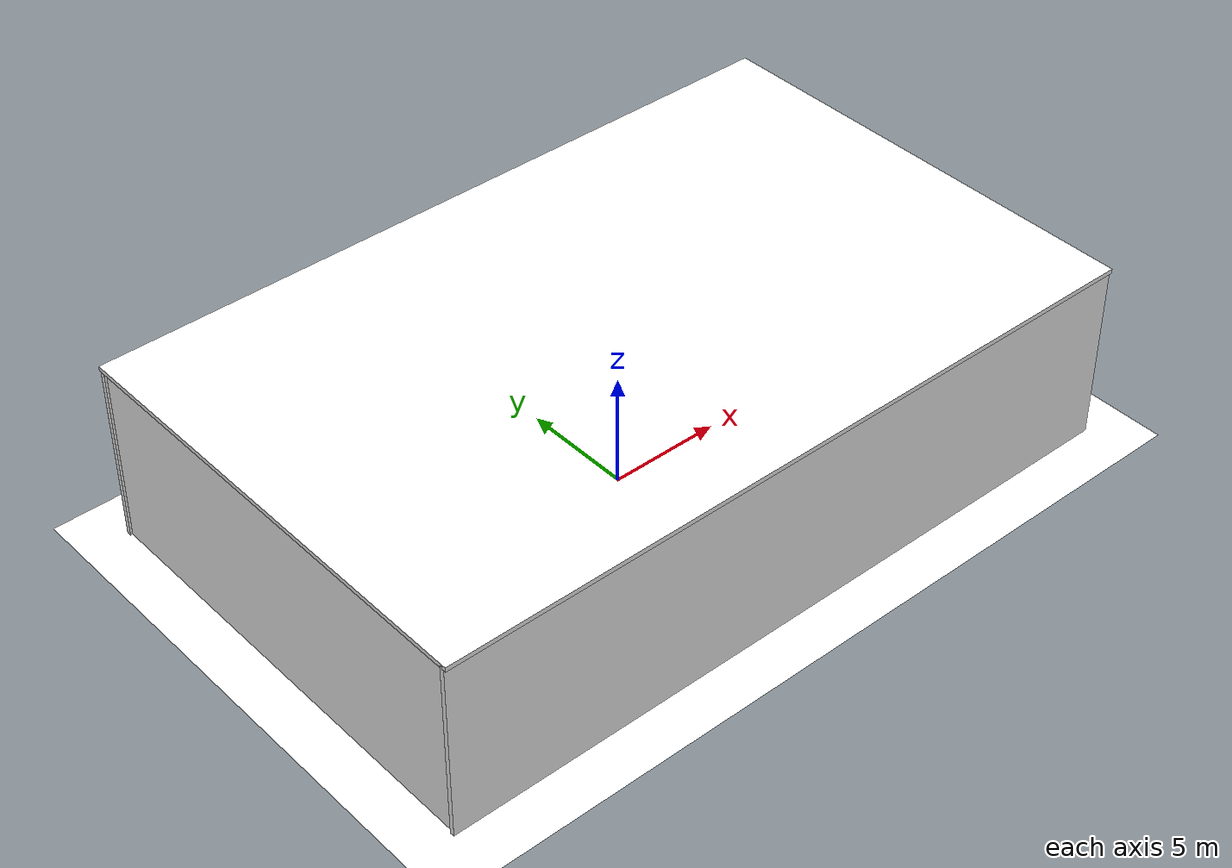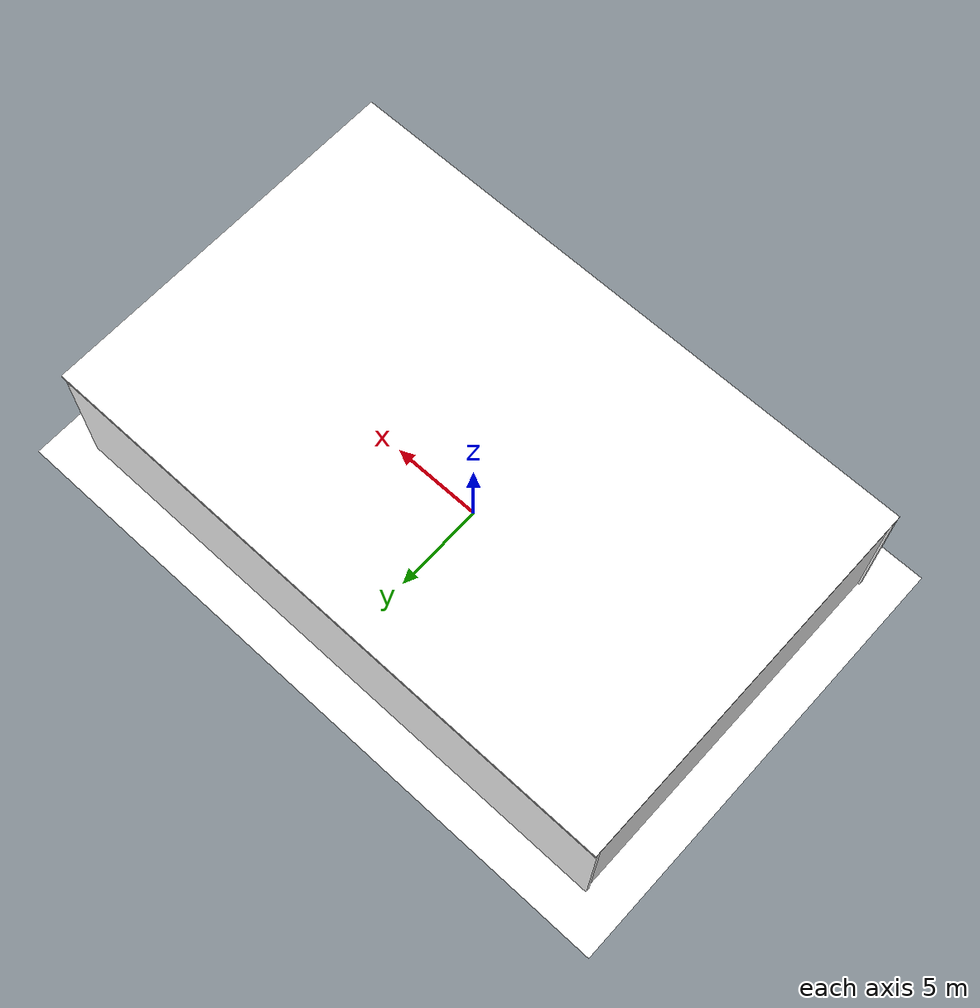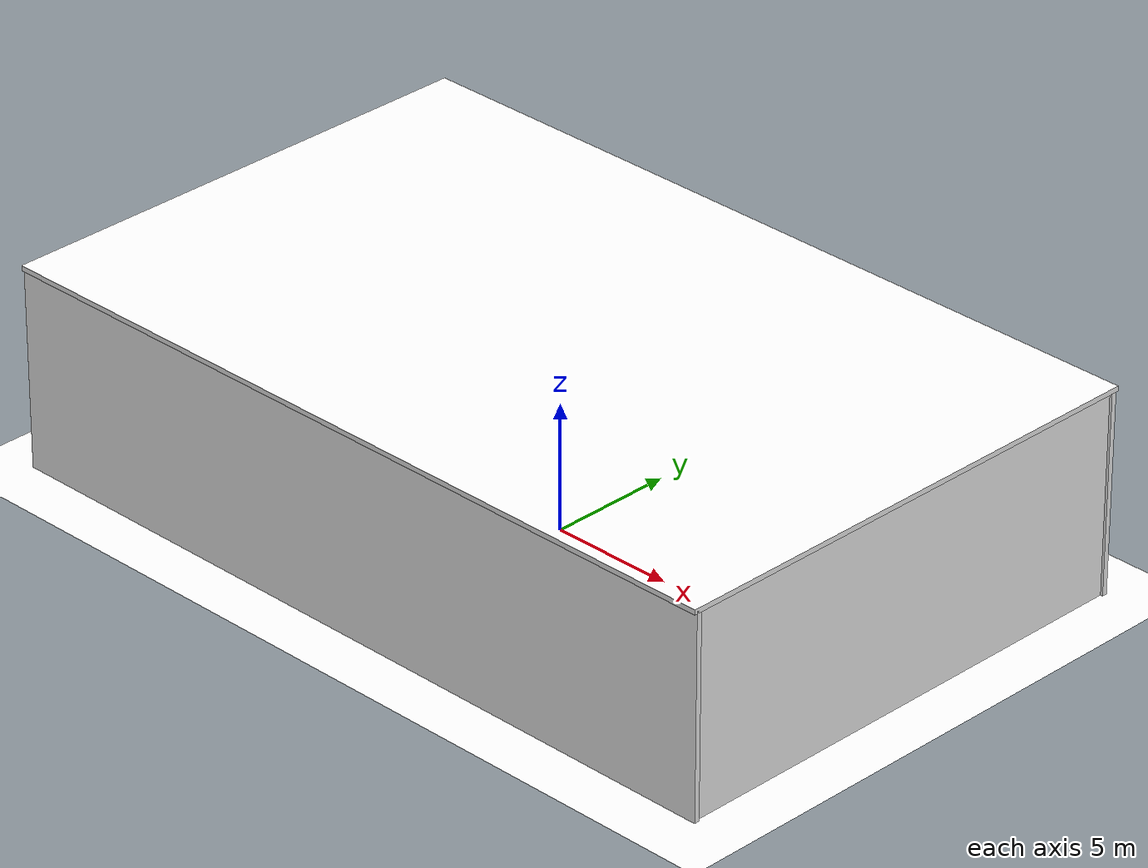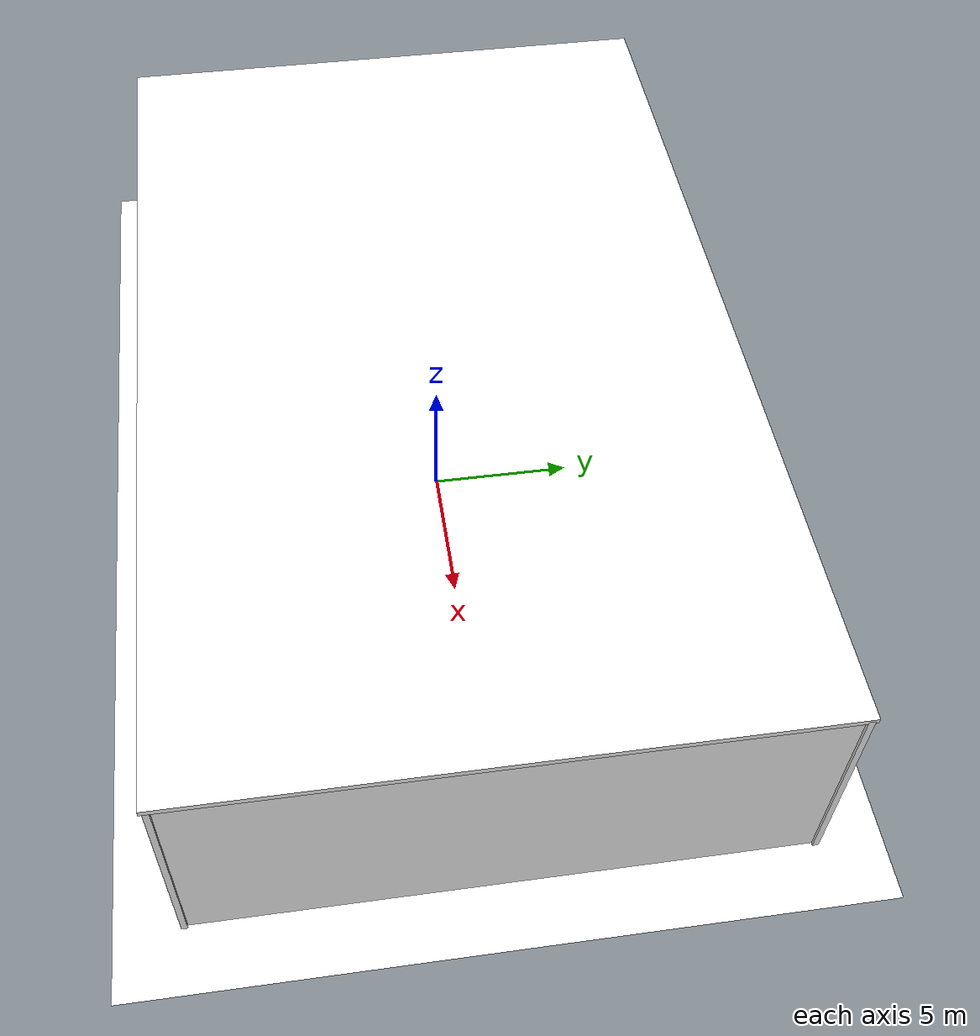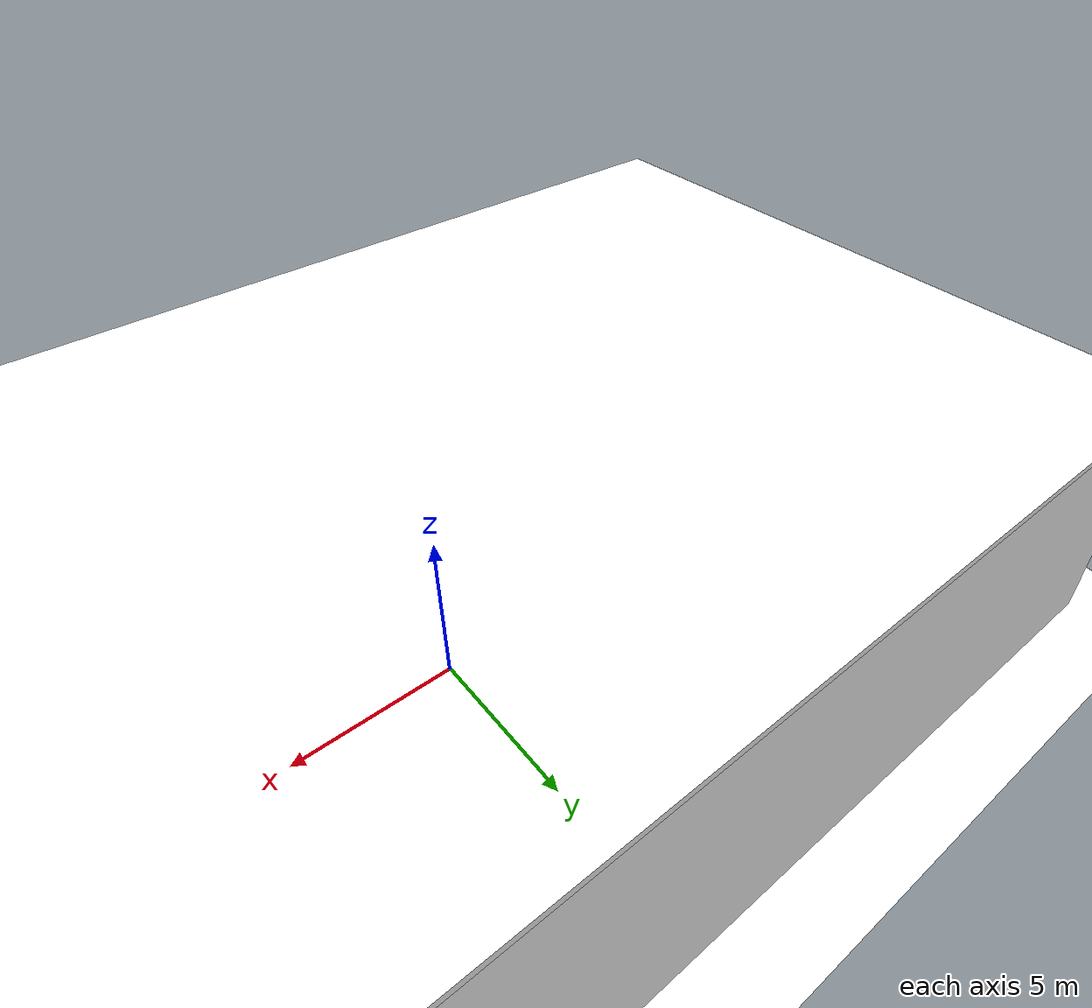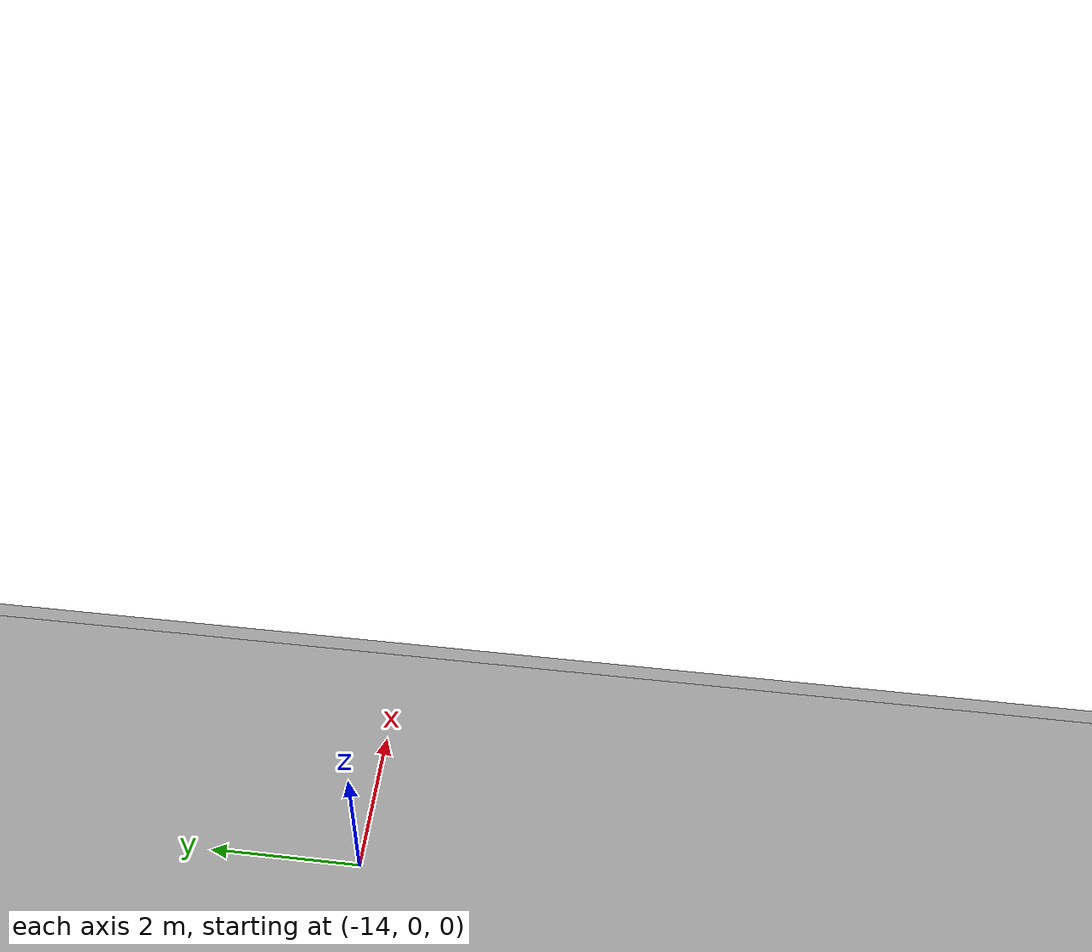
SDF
<sdf version="1.9">
 <world name="warehouse">
  <physics name="2ms" type="ignore">
   <max_step_size>0.002</max_step_size>
   <real_time_factor>1.0</real_time_factor>
   <dart><collision_detector>bullet</collision_detector></dart>
  </physics>
  <plugin filename="gz-sim-physics-system" name="gz::sim::systems::Physics"/>
  <plugin filename="gz-sim-user-commands-system" name="gz::sim::systems::UserCommands"/>
  <plugin filename="gz-sim-scene-broadcaster-system" name="gz::sim::systems::SceneBroadcaster"/>
  <plugin filename="gz-sim-imu-system" name="gz::sim::systems::Imu"/>
  <plugin filename="gz-sim-navsat-system" name="gz::sim::systems::NavSat"/>
  <plugin filename="gz-sim-sensors-system" name="gz::sim::systems::Sensors">
   <render_engine>ogre2</render_engine>
  </plugin>
  <gravity>0 0 -9.8066</gravity>
  <magnetic_field>2.0554e-05 0.0 4.5e-05</magnetic_field>
  <spherical_coordinates>
   <surface_model>EARTH_WGS84</surface_model>
   <world_frame_orientation>ENU</world_frame_orientation>
   <latitude_deg>49.8397</latitude_deg>
   <longitude_deg>24.0297</longitude_deg>
   <elevation>296.0</elevation>
   <heading_deg>0</heading_deg>
  </spherical_coordinates>
  <scene>
   <ambient>0.45 0.45 0.45 1</ambient>
   <background>0.2 0.22 0.25 1</background>
   <shadows>false</shadows>
   <grid>false</grid>
  </scene>
  <light name="bay_light_0_0" type="point">
   <pose>-12.0 -6.0 6.8 0 0 0</pose>
   <diffuse>0.85 0.85 0.8 1</diffuse>
   <specular>0.2 0.2 0.2 1</specular>
   <attenuation>
    <range>18</range>
    <constant>0.4</constant>
    <linear>0.05</linear>
    <quadratic>0.004</quadratic>
   </attenuation>
   <cast_shadows>false</cast_shadows>
  </light>
  <light name="bay_light_0_1" type="point">
   <pose>-12.0 0.0 6.8 0 0 0</pose>
   <diffuse>0.85 0.85 0.8 1</diffuse>
   <specular>0.2 0.2 0.2 1</specular>
   <attenuation>
    <range>18</range>
    <constant>0.4</constant>
    <linear>0.05</linear>
    <quadratic>0.004</quadratic>
   </attenuation>
   <cast_shadows>false</cast_shadows>
  </light>
  <light name="bay_light_0_2" type="point">
   <pose>-12.0 6.0 6.8 0 0 0</pose>
   <diffuse>0.85 0.85 0.8 1</diffuse>
   <specular>0.2 0.2 0.2 1</specular>
   <attenuation>
    <range>18</range>
    <constant>0.4</constant>
    <linear>0.05</linear>
    <quadratic>0.004</quadratic>
   </attenuation>
   <cast_shadows>false</cast_shadows>
  </light>
  <light name="bay_light_1_0" type="point">
   <pose>-4.0 -6.0 6.8 0 0 0</pose>
   <diffuse>0.85 0.85 0.8 1</diffuse>
   <specular>0.2 0.2 0.2 1</specular>
   <attenuation>
    <range>18</range>
    <constant>0.4</constant>
    <linear>0.05</linear>
    <quadratic>0.004</quadratic>
   </attenuation>
   <cast_shadows>false</cast_shadows>
  </light>
  <light name="bay_light_1_1" type="point">
   <pose>-4.0 0.0 6.8 0 0 0</pose>
   <diffuse>0.85 0.85 0.8 1</diffuse>
   <specular>0.2 0.2 0.2 1</specular>
   <attenuation>
    <range>18</range>
    <constant>0.4</constant>
    <linear>0.05</linear>
    <quadratic>0.004</quadratic>
   </attenuation>
   <cast_shadows>false</cast_shadows>
  </light>
  <light name="bay_light_1_2" type="point">
   <pose>-4.0 6.0 6.8 0 0 0</pose>
   <diffuse>0.85 0.85 0.8 1</diffuse>
   <specular>0.2 0.2 0.2 1</specular>
   <attenuation>
    <range>18</range>
    <constant>0.4</constant>
    <linear>0.05</linear>
    <quadratic>0.004</quadratic>
   </attenuation>
   <cast_shadows>false</cast_shadows>
  </light>
  <light name="bay_light_2_0" type="point">
   <pose>4.0 -6.0 6.8 0 0 0</pose>
   <diffuse>0.85 0.85 0.8 1</diffuse>
   <specular>0.2 0.2 0.2 1</specular>
   <attenuation>
    <range>18</range>
    <constant>0.4</constant>
    <linear>0.05</linear>
    <quadratic>0.004</quadratic>
   </attenuation>
   <cast_shadows>false</cast_shadows>
  </light>
  <light name="bay_light_2_1" type="point">
   <pose>4.0 0.0 6.8 0 0 0</pose>
   <diffuse>0.85 0.85 0.8 1</diffuse>
   <specular>0.2 0.2 0.2 1</specular>
   <attenuation>
    <range>18</range>
    <constant>0.4</constant>
    <linear>0.05</linear>
    <quadratic>0.004</quadratic>
   </attenuation>
   <cast_shadows>false</cast_shadows>
  </light>
  <light name="bay_light_2_2" type="point">
   <pose>4.0 6.0 6.8 0 0 0</pose>
   <diffuse>0.85 0.85 0.8 1</diffuse>
   <specular>0.2 0.2 0.2 1</specular>
   <attenuation>
    <range>18</range>
    <constant>0.4</constant>
    <linear>0.05</linear>
    <quadratic>0.004</quadratic>
   </attenuation>
   <cast_shadows>false</cast_shadows>
  </light>
  <light name="bay_light_3_0" type="point">
   <pose>12.0 -6.0 6.8 0 0 0</pose>
   <diffuse>0.85 0.85 0.8 1</diffuse>
   <specular>0.2 0.2 0.2 1</specular>
   <attenuation>
    <range>18</range>
    <constant>0.4</constant>
    <linear>0.05</linear>
    <quadratic>0.004</quadratic>
   </attenuation>
   <cast_shadows>false</cast_shadows>
  </light>
  <light name="bay_light_3_1" type="point">
   <pose>12.0 0.0 6.8 0 0 0</pose>
   <diffuse>0.85 0.85 0.8 1</diffuse>
   <specular>0.2 0.2 0.2 1</specular>
   <attenuation>
    <range>18</range>
    <constant>0.4</constant>
    <linear>0.05</linear>
    <quadratic>0.004</quadratic>
   </attenuation>
   <cast_shadows>false</cast_shadows>
  </light>
  <light name="bay_light_3_2" type="point">
   <pose>12.0 6.0 6.8 0 0 0</pose>
   <diffuse>0.85 0.85 0.8 1</diffuse>
   <specular>0.2 0.2 0.2 1</specular>
   <attenuation>
    <range>18</range>
    <constant>0.4</constant>
    <linear>0.05</linear>
    <quadratic>0.004</quadratic>
   </attenuation>
   <cast_shadows>false</cast_shadows>
  </light>
  <model name="ground_plane">
   <static>true</static>
   <link name="link">
    <collision name="collision">
     <geometry><plane><normal>0 0 1</normal><size>200 200</size></plane></geometry>
     <surface><friction><ode><mu>1.0</mu><mu2>1.0</mu2></ode></friction></surface>
    </collision>
    <visual name="visual">
     <geometry><plane><normal>0 0 1</normal><size>200 200</size></plane></geometry>
     <material>
      <ambient>0.5 0.5 0.5 1</ambient>
      <diffuse>1 1 1 1</diffuse>
      <pbr>
       <metal>
        <albedo_map>model://surfaces/materials/textures/floor.png</albedo_map>
        <metalness>0</metalness>
        <roughness>0.9</roughness>
       </metal>
      </pbr>
     </material>
    </visual>
   </link>
  </model>
  <model name="hall">
   <static>true</static>
   <link name="link">
    <visual name="wall_north_v">
     <pose>0 10 4 0 0 0</pose>
     <geometry><box><size>32.4 0.2 8</size></box></geometry>
     <material>
      <ambient>0.5 0.5 0.5 1</ambient>
      <diffuse>1 1 1 1</diffuse>
      <pbr>
       <metal>
        <albedo_map>model://surfaces/materials/textures/concrete.png</albedo_map>
        <metalness>0</metalness>
        <roughness>0.9</roughness>
       </metal>
      </pbr>
     </material>
    </visual>
    <collision name="wall_north_c">
     <pose>0 10 4 0 0 0</pose>
     <geometry><box><size>32.4 0.2 8</size></box></geometry>
    </collision>
    <visual name="wall_south_v">
     <pose>0 -10 4 0 0 0</pose>
     <geometry><box><size>32.4 0.2 8</size></box></geometry>
     <material>
      <ambient>0.5 0.5 0.5 1</ambient>
      <diffuse>1 1 1 1</diffuse>
      <pbr>
       <metal>
        <albedo_map>model://surfaces/materials/textures/concrete.png</albedo_map>
        <metalness>0</metalness>
        <roughness>0.9</roughness>
       </metal>
      </pbr>
     </material>
    </visual>
    <collision name="wall_south_c">
     <pose>0 -10 4 0 0 0</pose>
     <geometry><box><size>32.4 0.2 8</size></box></geometry>
    </collision>
    <visual name="wall_east_v">
     <pose>16 0 4 0 0 0</pose>
     <geometry><box><size>0.2 20 8</size></box></geometry>
     <material>
      <ambient>0.5 0.5 0.5 1</ambient>
      <diffuse>1 1 1 1</diffuse>
      <pbr>
       <metal>
        <albedo_map>model://surfaces/materials/textures/concrete.png</albedo_map>
        <metalness>0</metalness>
        <roughness>0.9</roughness>
       </metal>
      </pbr>
     </material>
    </visual>
    <collision name="wall_east_c">
     <pose>16 0 4 0 0 0</pose>
     <geometry><box><size>0.2 20 8</size></box></geometry>
    </collision>
    <visual name="wall_west_v">
     <pose>-16 0 4 0 0 0</pose>
     <geometry><box><size>0.2 20 8</size></box></geometry>
     <material>
      <ambient>0.5 0.5 0.5 1</ambient>
      <diffuse>1 1 1 1</diffuse>
      <pbr>
       <metal>
        <albedo_map>model://surfaces/materials/textures/concrete.png</albedo_map>
        <metalness>0</metalness>
        <roughness>0.9</roughness>
       </metal>
      </pbr>
     </material>
    </visual>
    <collision name="wall_west_c">
     <pose>-16 0 4 0 0 0</pose>
     <geometry><box><size>0.2 20 8</size></box></geometry>
    </collision>
    <visual name="roof_v">
     <pose>0 0 8 0 0 0</pose>
     <geometry><box><size>32.4 20.4 0.2</size></box></geometry>
     <material>
      <ambient>0.5 0.5 0.5 1</ambient>
      <diffuse>1 1 1 1</diffuse>
      <pbr>
       <metal>
        <albedo_map>model://surfaces/materials/textures/concrete.png</albedo_map>
        <metalness>0</metalness>
        <roughness>0.9</roughness>
       </metal>
      </pbr>
     </material>
    </visual>
    <collision name="roof_c">
     <pose>0 0 8 0 0 0</pose>
     <geometry><box><size>32.4 20.4 0.2</size></box></geometry>
    </collision>
    <visual name="band_0_s_v">
     <pose>-14 -9.89 2 0 0 0</pose>
     <geometry><box><size>0.6 0.02 3</size></box></geometry>
     <material><ambient>0.31 0.225 0.14 1</ambient><diffuse>0.62 0.45 0.28 1</diffuse></material>
    </visual>
    <visual name="band_0_n_v">
     <pose>-14 9.89 2 0 0 0</pose>
     <geometry><box><size>0.6 0.02 3</size></box></geometry>
     <material><ambient>0.31 0.225 0.14 1</ambient><diffuse>0.62 0.45 0.28 1</diffuse></material>
    </visual>
    <visual name="band_1_s_v">
     <pose>-10 -9.89 2 0 0 0</pose>
     <geometry><box><size>0.6 0.02 3</size></box></geometry>
     <material><ambient>0.35 0.26 0.16 1</ambient><diffuse>0.7 0.52 0.32 1</diffuse></material>
    </visual>
    <visual name="band_1_n_v">
     <pose>-10 9.89 2 0 0 0</pose>
     <geometry><box><size>0.6 0.02 3</size></box></geometry>
     <material><ambient>0.35 0.26 0.16 1</ambient><diffuse>0.7 0.52 0.32 1</diffuse></material>
    </visual>
    <visual name="band_2_s_v">
     <pose>-6 -9.89 2 0 0 0</pose>
     <geometry><box><size>0.6 0.02 3</size></box></geometry>
     <material><ambient>0.275 0.19 0.11 1</ambient><diffuse>0.55 0.38 0.22 1</diffuse></material>
    </visual>
    <visual name="band_2_n_v">
     <pose>-6 9.89 2 0 0 0</pose>
     <geometry><box><size>0.6 0.02 3</size></box></geometry>
     <material><ambient>0.275 0.19 0.11 1</ambient><diffuse>0.55 0.38 0.22 1</diffuse></material>
    </visual>
    <visual name="band_3_s_v">
     <pose>-2 -9.89 2 0 0 0</pose>
     <geometry><box><size>0.6 0.02 3</size></box></geometry>
     <material><ambient>0.15 0.21 0.31 1</ambient><diffuse>0.3 0.42 0.62 1</diffuse></material>
    </visual>
    <visual name="band_3_n_v">
     <pose>-2 9.89 2 0 0 0</pose>
     <geometry><box><size>0.6 0.02 3</size></box></geometry>
     <material><ambient>0.15 0.21 0.31 1</ambient><diffuse>0.3 0.42 0.62 1</diffuse></material>
    </visual>
    <visual name="band_4_s_v">
     <pose>2 -9.89 2 0 0 0</pose>
     <geometry><box><size>0.6 0.02 3</size></box></geometry>
     <material><ambient>0.33 0.12 0.11 1</ambient><diffuse>0.66 0.24 0.22 1</diffuse></material>
    </visual>
    <visual name="band_4_n_v">
     <pose>2 9.89 2 0 0 0</pose>
     <geometry><box><size>0.6 0.02 3</size></box></geometry>
     <material><ambient>0.33 0.12 0.11 1</ambient><diffuse>0.66 0.24 0.22 1</diffuse></material>
    </visual>
    <visual name="band_5_s_v">
     <pose>6 -9.89 2 0 0 0</pose>
     <geometry><box><size>0.6 0.02 3</size></box></geometry>
     <material><ambient>0.14 0.26 0.18 1</ambient><diffuse>0.28 0.52 0.36 1</diffuse></material>
    </visual>
    <visual name="band_5_n_v">
     <pose>6 9.89 2 0 0 0</pose>
     <geometry><box><size>0.6 0.02 3</size></box></geometry>
     <material><ambient>0.14 0.26 0.18 1</ambient><diffuse>0.28 0.52 0.36 1</diffuse></material>
    </visual>
    <visual name="band_6_s_v">
     <pose>10 -9.89 2 0 0 0</pose>
     <geometry><box><size>0.6 0.02 3</size></box></geometry>
     <material><ambient>0.31 0.225 0.14 1</ambient><diffuse>0.62 0.45 0.28 1</diffuse></material>
    </visual>
    <visual name="band_6_n_v">
     <pose>10 9.89 2 0 0 0</pose>
     <geometry><box><size>0.6 0.02 3</size></box></geometry>
     <material><ambient>0.31 0.225 0.14 1</ambient><diffuse>0.62 0.45 0.28 1</diffuse></material>
    </visual>
    <visual name="band_7_s_v">
     <pose>14 -9.89 2 0 0 0</pose>
     <geometry><box><size>0.6 0.02 3</size></box></geometry>
     <material><ambient>0.35 0.26 0.16 1</ambient><diffuse>0.7 0.52 0.32 1</diffuse></material>
    </visual>
    <visual name="band_7_n_v">
     <pose>14 9.89 2 0 0 0</pose>
     <geometry><box><size>0.6 0.02 3</size></box></geometry>
     <material><ambient>0.35 0.26 0.16 1</ambient><diffuse>0.7 0.52 0.32 1</diffuse></material>
    </visual>
   </link>
  </model>
  <model name="floor_markings">
   <static>true</static>
   <link name="link">
    <visual name="aisle_line_0_-1_v">
     <pose>0 -6.7 0.005 0 0 0</pose>
     <geometry><box><size>26 0.12 0.01</size></box></geometry>
     <material><ambient>0.475 0.425 0.075 1</ambient><diffuse>0.95 0.85 0.15 1</diffuse></material>
    </visual>
    <visual name="aisle_line_0_1_v">
     <pose>0 -3.3 0.005 0 0 0</pose>
     <geometry><box><size>26 0.12 0.01</size></box></geometry>
     <material><ambient>0.475 0.425 0.075 1</ambient><diffuse>0.95 0.85 0.15 1</diffuse></material>
    </visual>
    <visual name="aisle_line_1_-1_v">
     <pose>0 -1.7 0.005 0 0 0</pose>
     <geometry><box><size>26 0.12 0.01</size></box></geometry>
     <material><ambient>0.475 0.425 0.075 1</ambient><diffuse>0.95 0.85 0.15 1</diffuse></material>
    </visual>
    <visual name="aisle_line_1_1_v">
     <pose>0 1.7 0.005 0 0 0</pose>
     <geometry><box><size>26 0.12 0.01</size></box></geometry>
     <material><ambient>0.475 0.425 0.075 1</ambient><diffuse>0.95 0.85 0.15 1</diffuse></material>
    </visual>
    <visual name="aisle_line_2_-1_v">
     <pose>0 3.3 0.005 0 0 0</pose>
     <geometry><box><size>26 0.12 0.01</size></box></geometry>
     <material><ambient>0.475 0.425 0.075 1</ambient><diffuse>0.95 0.85 0.15 1</diffuse></material>
    </visual>
    <visual name="aisle_line_2_1_v">
     <pose>0 6.7 0.005 0 0 0</pose>
     <geometry><box><size>26 0.12 0.01</size></box></geometry>
     <material><ambient>0.475 0.425 0.075 1</ambient><diffuse>0.95 0.85 0.15 1</diffuse></material>
    </visual>
   </link>
  </model>
  <model name="rack_0_0">
   <static>true</static>
   <pose>-10.4 -7.5 0 0 0 0</pose>
   <link name="link">
    <visual name="upright_0_v">
     <pose>-1.25 -0.5 2 0 0 0</pose>
     <geometry><box><size>0.1 0.1 4</size></box></geometry>
     <material><ambient>0.125 0.16 0.225 1</ambient><diffuse>0.25 0.32 0.45 1</diffuse></material>
    </visual>
    <collision name="upright_0_c">
     <pose>-1.25 -0.5 2 0 0 0</pose>
     <geometry><box><size>0.1 0.1 4</size></box></geometry>
    </collision>
    <visual name="upright_1_v">
     <pose>-1.25 0.5 2 0 0 0</pose>
     <geometry><box><size>0.1 0.1 4</size></box></geometry>
     <material><ambient>0.125 0.16 0.225 1</ambient><diffuse>0.25 0.32 0.45 1</diffuse></material>
    </visual>
    <collision name="upright_1_c">
     <pose>-1.25 0.5 2 0 0 0</pose>
     <geometry><box><size>0.1 0.1 4</size></box></geometry>
    </collision>
    <visual name="upright_2_v">
     <pose>1.25 -0.5 2 0 0 0</pose>
     <geometry><box><size>0.1 0.1 4</size></box></geometry>
     <material><ambient>0.125 0.16 0.225 1</ambient><diffuse>0.25 0.32 0.45 1</diffuse></material>
    </visual>
    <collision name="upright_2_c">
     <pose>1.25 -0.5 2 0 0 0</pose>
     <geometry><box><size>0.1 0.1 4</size></box></geometry>
    </collision>
    <visual name="upright_3_v">
     <pose>1.25 0.5 2 0 0 0</pose>
     <geometry><box><size>0.1 0.1 4</size></box></geometry>
     <material><ambient>0.125 0.16 0.225 1</ambient><diffuse>0.25 0.32 0.45 1</diffuse></material>
    </visual>
    <collision name="upright_3_c">
     <pose>1.25 0.5 2 0 0 0</pose>
     <geometry><box><size>0.1 0.1 4</size></box></geometry>
    </collision>
    <visual name="deck_0_v">
     <pose>0 0 0.25 0 0 0</pose>
     <geometry><box><size>2.6 1.1 0.07</size></box></geometry>
     <material><ambient>0.425 0.275 0.06 1</ambient><diffuse>0.85 0.55 0.12 1</diffuse></material>
    </visual>
    <collision name="deck_0_c">
     <pose>0 0 0.25 0 0 0</pose>
     <geometry><box><size>2.6 1.1 0.07</size></box></geometry>
    </collision>
    <visual name="cargo_0_0_v">
     <pose>-0.8667 0.007176 0.5227 0 0 0.1229</pose>
     <geometry><box><size>0.6802 0.6914 0.4754</size></box></geometry>
     <material><ambient>0.31 0.225 0.14 1</ambient><diffuse>0.62 0.45 0.28 1</diffuse></material>
    </visual>
    <collision name="cargo_0_0_c">
     <pose>-0.8667 0.007176 0.5227 0 0 0.1229</pose>
     <geometry><box><size>0.6802 0.6914 0.4754</size></box></geometry>
    </collision>
    <visual name="cargo_0_1_v">
     <pose>0 -0.01637 0.525 0 0 -0.02264</pose>
     <geometry><box><size>0.5929 0.6602 0.4801</size></box></geometry>
     <material><ambient>0.33 0.12 0.11 1</ambient><diffuse>0.66 0.24 0.22 1</diffuse></material>
    </visual>
    <collision name="cargo_0_1_c">
     <pose>0 -0.01637 0.525 0 0 -0.02264</pose>
     <geometry><box><size>0.5929 0.6602 0.4801</size></box></geometry>
    </collision>
    <visual name="deck_1_v">
     <pose>0 0 1.35 0 0 0</pose>
     <geometry><box><size>2.6 1.1 0.07</size></box></geometry>
     <material><ambient>0.425 0.275 0.06 1</ambient><diffuse>0.85 0.55 0.12 1</diffuse></material>
    </visual>
    <collision name="deck_1_c">
     <pose>0 0 1.35 0 0 0</pose>
     <geometry><box><size>2.6 1.1 0.07</size></box></geometry>
    </collision>
    <visual name="cargo_1_0_v">
     <pose>-0.8667 0.09525 1.679 0 0 -0.06312</pose>
     <geometry><box><size>0.6654 0.6116 0.5888</size></box></geometry>
     <material><ambient>0.35 0.26 0.16 1</ambient><diffuse>0.7 0.52 0.32 1</diffuse></material>
    </visual>
    <collision name="cargo_1_0_c">
     <pose>-0.8667 0.09525 1.679 0 0 -0.06312</pose>
     <geometry><box><size>0.6654 0.6116 0.5888</size></box></geometry>
    </collision>
    <visual name="cargo_1_2_v">
     <pose>0.8667 -0.0383 1.631 0 0 -0.1191</pose>
     <geometry><box><size>0.5789 0.804 0.4912</size></box></geometry>
     <material><ambient>0.35 0.26 0.16 1</ambient><diffuse>0.7 0.52 0.32 1</diffuse></material>
    </visual>
    <collision name="cargo_1_2_c">
     <pose>0.8667 -0.0383 1.631 0 0 -0.1191</pose>
     <geometry><box><size>0.5789 0.804 0.4912</size></box></geometry>
    </collision>
    <visual name="cargo_1_1_v">
     <pose>0 -0.08051 1.643 0 0 -0.1321</pose>
     <geometry><box><size>0.6642 0.778 0.5158</size></box></geometry>
     <material><ambient>0.33 0.12 0.11 1</ambient><diffuse>0.66 0.24 0.22 1</diffuse></material>
    </visual>
    <collision name="cargo_1_1_c">
     <pose>0 -0.08051 1.643 0 0 -0.1321</pose>
     <geometry><box><size>0.6642 0.778 0.5158</size></box></geometry>
    </collision>
    <visual name="deck_2_v">
     <pose>0 0 2.45 0 0 0</pose>
     <geometry><box><size>2.6 1.1 0.07</size></box></geometry>
     <material><ambient>0.425 0.275 0.06 1</ambient><diffuse>0.85 0.55 0.12 1</diffuse></material>
    </visual>
    <collision name="deck_2_c">
     <pose>0 0 2.45 0 0 0</pose>
     <geometry><box><size>2.6 1.1 0.07</size></box></geometry>
    </collision>
    <visual name="cargo_2_1_v">
     <pose>0 -0.03717 2.785 0 0 -0.04153</pose>
     <geometry><box><size>0.6861 0.7464 0.5997</size></box></geometry>
     <material><ambient>0.15 0.21 0.31 1</ambient><diffuse>0.3 0.42 0.62 1</diffuse></material>
    </visual>
    <collision name="cargo_2_1_c">
     <pose>0 -0.03717 2.785 0 0 -0.04153</pose>
     <geometry><box><size>0.6861 0.7464 0.5997</size></box></geometry>
    </collision>
    <visual name="deck_3_v">
     <pose>0 0 3.55 0 0 0</pose>
     <geometry><box><size>2.6 1.1 0.07</size></box></geometry>
     <material><ambient>0.425 0.275 0.06 1</ambient><diffuse>0.85 0.55 0.12 1</diffuse></material>
    </visual>
    <collision name="deck_3_c">
     <pose>0 0 3.55 0 0 0</pose>
     <geometry><box><size>2.6 1.1 0.07</size></box></geometry>
    </collision>
    <visual name="cargo_3_0_v">
     <pose>-0.8667 0.01488 3.853 0 0 0.06883</pose>
     <geometry><box><size>0.6898 0.7313 0.5354</size></box></geometry>
     <material><ambient>0.275 0.19 0.11 1</ambient><diffuse>0.55 0.38 0.22 1</diffuse></material>
    </visual>
    <collision name="cargo_3_0_c">
     <pose>-0.8667 0.01488 3.853 0 0 0.06883</pose>
     <geometry><box><size>0.6898 0.7313 0.5354</size></box></geometry>
    </collision>
   </link>
  </model>
  <model name="rack_0_1">
   <static>true</static>
   <pose>-5.2 -7.5 0 0 0 0</pose>
   <link name="link">
    <visual name="upright_0_v">
     <pose>-1.25 -0.5 2 0 0 0</pose>
     <geometry><box><size>0.1 0.1 4</size></box></geometry>
     <material><ambient>0.125 0.16 0.225 1</ambient><diffuse>0.25 0.32 0.45 1</diffuse></material>
    </visual>
    <collision name="upright_0_c">
     <pose>-1.25 -0.5 2 0 0 0</pose>
     <geometry><box><size>0.1 0.1 4</size></box></geometry>
    </collision>
    <visual name="upright_1_v">
     <pose>-1.25 0.5 2 0 0 0</pose>
     <geometry><box><size>0.1 0.1 4</size></box></geometry>
     <material><ambient>0.125 0.16 0.225 1</ambient><diffuse>0.25 0.32 0.45 1</diffuse></material>
    </visual>
    <collision name="upright_1_c">
     <pose>-1.25 0.5 2 0 0 0</pose>
     <geometry><box><size>0.1 0.1 4</size></box></geometry>
    </collision>
    <visual name="upright_2_v">
     <pose>1.25 -0.5 2 0 0 0</pose>
     <geometry><box><size>0.1 0.1 4</size></box></geometry>
     <material><ambient>0.125 0.16 0.225 1</ambient><diffuse>0.25 0.32 0.45 1</diffuse></material>
    </visual>
    <collision name="upright_2_c">
     <pose>1.25 -0.5 2 0 0 0</pose>
     <geometry><box><size>0.1 0.1 4</size></box></geometry>
    </collision>
    <visual name="upright_3_v">
     <pose>1.25 0.5 2 0 0 0</pose>
     <geometry><box><size>0.1 0.1 4</size></box></geometry>
     <material><ambient>0.125 0.16 0.225 1</ambient><diffuse>0.25 0.32 0.45 1</diffuse></material>
    </visual>
    <collision name="upright_3_c">
     <pose>1.25 0.5 2 0 0 0</pose>
     <geometry><box><size>0.1 0.1 4</size></box></geometry>
    </collision>
    <visual name="deck_0_v">
     <pose>0 0 0.25 0 0 0</pose>
     <geometry><box><size>2.6 1.1 0.07</size></box></geometry>
     <material><ambient>0.425 0.275 0.06 1</ambient><diffuse>0.85 0.55 0.12 1</diffuse></material>
    </visual>
    <collision name="deck_0_c">
     <pose>0 0 0.25 0 0 0</pose>
     <geometry><box><size>2.6 1.1 0.07</size></box></geometry>
    </collision>
    <visual name="cargo_0_2_v">
     <pose>0.8667 0.05143 0.5832 0 0 -0.02349</pose>
     <geometry><box><size>0.5736 0.638 0.5963</size></box></geometry>
     <material><ambient>0.15 0.21 0.31 1</ambient><diffuse>0.3 0.42 0.62 1</diffuse></material>
    </visual>
    <collision name="cargo_0_2_c">
     <pose>0.8667 0.05143 0.5832 0 0 -0.02349</pose>
     <geometry><box><size>0.5736 0.638 0.5963</size></box></geometry>
    </collision>
    <visual name="cargo_0_0_v">
     <pose>-0.8667 0.01162 0.5236 0 0 -0.04796</pose>
     <geometry><box><size>0.7424 0.7973 0.4772</size></box></geometry>
     <material><ambient>0.275 0.19 0.11 1</ambient><diffuse>0.55 0.38 0.22 1</diffuse></material>
    </visual>
    <collision name="cargo_0_0_c">
     <pose>-0.8667 0.01162 0.5236 0 0 -0.04796</pose>
     <geometry><box><size>0.7424 0.7973 0.4772</size></box></geometry>
    </collision>
    <visual name="deck_1_v">
     <pose>0 0 1.35 0 0 0</pose>
     <geometry><box><size>2.6 1.1 0.07</size></box></geometry>
     <material><ambient>0.425 0.275 0.06 1</ambient><diffuse>0.85 0.55 0.12 1</diffuse></material>
    </visual>
    <collision name="deck_1_c">
     <pose>0 0 1.35 0 0 0</pose>
     <geometry><box><size>2.6 1.1 0.07</size></box></geometry>
    </collision>
    <visual name="cargo_1_2_v">
     <pose>0.8667 0.06799 1.69 0 0 0.05911</pose>
     <geometry><box><size>0.666 0.8362 0.6097</size></box></geometry>
     <material><ambient>0.15 0.21 0.31 1</ambient><diffuse>0.3 0.42 0.62 1</diffuse></material>
    </visual>
    <collision name="cargo_1_2_c">
     <pose>0.8667 0.06799 1.69 0 0 0.05911</pose>
     <geometry><box><size>0.666 0.8362 0.6097</size></box></geometry>
    </collision>
    <visual name="cargo_1_1_v">
     <pose>0 -0.03808 1.738 0 0 0.09658</pose>
     <geometry><box><size>0.563 0.7445 0.7059</size></box></geometry>
     <material><ambient>0.14 0.26 0.18 1</ambient><diffuse>0.28 0.52 0.36 1</diffuse></material>
    </visual>
    <collision name="cargo_1_1_c">
     <pose>0 -0.03808 1.738 0 0 0.09658</pose>
     <geometry><box><size>0.563 0.7445 0.7059</size></box></geometry>
    </collision>
    <visual name="deck_2_v">
     <pose>0 0 2.45 0 0 0</pose>
     <geometry><box><size>2.6 1.1 0.07</size></box></geometry>
     <material><ambient>0.425 0.275 0.06 1</ambient><diffuse>0.85 0.55 0.12 1</diffuse></material>
    </visual>
    <collision name="deck_2_c">
     <pose>0 0 2.45 0 0 0</pose>
     <geometry><box><size>2.6 1.1 0.07</size></box></geometry>
    </collision>
    <visual name="cargo_2_2_v">
     <pose>0.8667 0.08813 2.771 0 0 -0.1149</pose>
     <geometry><box><size>0.7274 0.6889 0.5715</size></box></geometry>
     <material><ambient>0.33 0.12 0.11 1</ambient><diffuse>0.66 0.24 0.22 1</diffuse></material>
    </visual>
    <collision name="cargo_2_2_c">
     <pose>0.8667 0.08813 2.771 0 0 -0.1149</pose>
     <geometry><box><size>0.7274 0.6889 0.5715</size></box></geometry>
    </collision>
    <visual name="cargo_2_1_v">
     <pose>0 -0.07413 2.844 0 0 0.125</pose>
     <geometry><box><size>0.5618 0.6619 0.7189</size></box></geometry>
     <material><ambient>0.15 0.21 0.31 1</ambient><diffuse>0.3 0.42 0.62 1</diffuse></material>
    </visual>
    <collision name="cargo_2_1_c">
     <pose>0 -0.07413 2.844 0 0 0.125</pose>
     <geometry><box><size>0.5618 0.6619 0.7189</size></box></geometry>
    </collision>
    <visual name="deck_3_v">
     <pose>0 0 3.55 0 0 0</pose>
     <geometry><box><size>2.6 1.1 0.07</size></box></geometry>
     <material><ambient>0.425 0.275 0.06 1</ambient><diffuse>0.85 0.55 0.12 1</diffuse></material>
    </visual>
    <collision name="deck_3_c">
     <pose>0 0 3.55 0 0 0</pose>
     <geometry><box><size>2.6 1.1 0.07</size></box></geometry>
    </collision>
    <visual name="cargo_3_0_v">
     <pose>-0.8667 0.07668 3.906 0 0 -0.06647</pose>
     <geometry><box><size>0.6398 0.8048 0.6423</size></box></geometry>
     <material><ambient>0.33 0.12 0.11 1</ambient><diffuse>0.66 0.24 0.22 1</diffuse></material>
    </visual>
    <collision name="cargo_3_0_c">
     <pose>-0.8667 0.07668 3.906 0 0 -0.06647</pose>
     <geometry><box><size>0.6398 0.8048 0.6423</size></box></geometry>
    </collision>
    <visual name="cargo_3_2_v">
     <pose>0.8667 0.07684 3.873 0 0 -0.1251</pose>
     <geometry><box><size>0.6331 0.8394 0.5756</size></box></geometry>
     <material><ambient>0.35 0.26 0.16 1</ambient><diffuse>0.7 0.52 0.32 1</diffuse></material>
    </visual>
    <collision name="cargo_3_2_c">
     <pose>0.8667 0.07684 3.873 0 0 -0.1251</pose>
     <geometry><box><size>0.6331 0.8394 0.5756</size></box></geometry>
    </collision>
   </link>
  </model>
  <model name="rack_0_2">
   <static>true</static>
   <pose>0 -7.5 0 0 0 0</pose>
   <link name="link">
    <visual name="upright_0_v">
     <pose>-1.25 -0.5 2 0 0 0</pose>
     <geometry><box><size>0.1 0.1 4</size></box></geometry>
     <material><ambient>0.125 0.16 0.225 1</ambient><diffuse>0.25 0.32 0.45 1</diffuse></material>
    </visual>
    <collision name="upright_0_c">
     <pose>-1.25 -0.5 2 0 0 0</pose>
     <geometry><box><size>0.1 0.1 4</size></box></geometry>
    </collision>
    <visual name="upright_1_v">
     <pose>-1.25 0.5 2 0 0 0</pose>
     <geometry><box><size>0.1 0.1 4</size></box></geometry>
     <material><ambient>0.125 0.16 0.225 1</ambient><diffuse>0.25 0.32 0.45 1</diffuse></material>
    </visual>
    <collision name="upright_1_c">
     <pose>-1.25 0.5 2 0 0 0</pose>
     <geometry><box><size>0.1 0.1 4</size></box></geometry>
    </collision>
    <visual name="upright_2_v">
     <pose>1.25 -0.5 2 0 0 0</pose>
     <geometry><box><size>0.1 0.1 4</size></box></geometry>
     <material><ambient>0.125 0.16 0.225 1</ambient><diffuse>0.25 0.32 0.45 1</diffuse></material>
    </visual>
    <collision name="upright_2_c">
     <pose>1.25 -0.5 2 0 0 0</pose>
     <geometry><box><size>0.1 0.1 4</size></box></geometry>
    </collision>
    <visual name="upright_3_v">
     <pose>1.25 0.5 2 0 0 0</pose>
     <geometry><box><size>0.1 0.1 4</size></box></geometry>
     <material><ambient>0.125 0.16 0.225 1</ambient><diffuse>0.25 0.32 0.45 1</diffuse></material>
    </visual>
    <collision name="upright_3_c">
     <pose>1.25 0.5 2 0 0 0</pose>
     <geometry><box><size>0.1 0.1 4</size></box></geometry>
    </collision>
    <visual name="deck_0_v">
     <pose>0 0 0.25 0 0 0</pose>
     <geometry><box><size>2.6 1.1 0.07</size></box></geometry>
     <material><ambient>0.425 0.275 0.06 1</ambient><diffuse>0.85 0.55 0.12 1</diffuse></material>
    </visual>
    <collision name="deck_0_c">
     <pose>0 0 0.25 0 0 0</pose>
     <geometry><box><size>2.6 1.1 0.07</size></box></geometry>
    </collision>
    <visual name="cargo_0_0_v">
     <pose>-0.8667 0.06622 0.5121 0 0 -0.1488</pose>
     <geometry><box><size>0.6817 0.6456 0.4542</size></box></geometry>
     <material><ambient>0.275 0.19 0.11 1</ambient><diffuse>0.55 0.38 0.22 1</diffuse></material>
    </visual>
    <collision name="cargo_0_0_c">
     <pose>-0.8667 0.06622 0.5121 0 0 -0.1488</pose>
     <geometry><box><size>0.6817 0.6456 0.4542</size></box></geometry>
    </collision>
    <visual name="deck_1_v">
     <pose>0 0 1.35 0 0 0</pose>
     <geometry><box><size>2.6 1.1 0.07</size></box></geometry>
     <material><ambient>0.425 0.275 0.06 1</ambient><diffuse>0.85 0.55 0.12 1</diffuse></material>
    </visual>
    <collision name="deck_1_c">
     <pose>0 0 1.35 0 0 0</pose>
     <geometry><box><size>2.6 1.1 0.07</size></box></geometry>
    </collision>
    <visual name="cargo_1_2_v">
     <pose>0.8667 -0.0749 1.666 0 0 0.04649</pose>
     <geometry><box><size>0.672 0.8148 0.5615</size></box></geometry>
     <material><ambient>0.33 0.12 0.11 1</ambient><diffuse>0.66 0.24 0.22 1</diffuse></material>
    </visual>
    <collision name="cargo_1_2_c">
     <pose>0.8667 -0.0749 1.666 0 0 0.04649</pose>
     <geometry><box><size>0.672 0.8148 0.5615</size></box></geometry>
    </collision>
    <visual name="cargo_1_1_v">
     <pose>0 0.0742 1.69 0 0 0.08936</pose>
     <geometry><box><size>0.698 0.838 0.6098</size></box></geometry>
     <material><ambient>0.14 0.26 0.18 1</ambient><diffuse>0.28 0.52 0.36 1</diffuse></material>
    </visual>
    <collision name="cargo_1_1_c">
     <pose>0 0.0742 1.69 0 0 0.08936</pose>
     <geometry><box><size>0.698 0.838 0.6098</size></box></geometry>
    </collision>
    <visual name="deck_2_v">
     <pose>0 0 2.45 0 0 0</pose>
     <geometry><box><size>2.6 1.1 0.07</size></box></geometry>
     <material><ambient>0.425 0.275 0.06 1</ambient><diffuse>0.85 0.55 0.12 1</diffuse></material>
    </visual>
    <collision name="deck_2_c">
     <pose>0 0 2.45 0 0 0</pose>
     <geometry><box><size>2.6 1.1 0.07</size></box></geometry>
    </collision>
    <visual name="cargo_2_1_v">
     <pose>0 -0.01991 2.794 0 0 -0.01781</pose>
     <geometry><box><size>0.6288 0.6477 0.6185</size></box></geometry>
     <material><ambient>0.35 0.26 0.16 1</ambient><diffuse>0.7 0.52 0.32 1</diffuse></material>
    </visual>
    <collision name="cargo_2_1_c">
     <pose>0 -0.01991 2.794 0 0 -0.01781</pose>
     <geometry><box><size>0.6288 0.6477 0.6185</size></box></geometry>
    </collision>
    <visual name="cargo_2_2_v">
     <pose>0.8667 -0.07952 2.815 0 0 -0.1196</pose>
     <geometry><box><size>0.572 0.7417 0.6603</size></box></geometry>
     <material><ambient>0.33 0.12 0.11 1</ambient><diffuse>0.66 0.24 0.22 1</diffuse></material>
    </visual>
    <collision name="cargo_2_2_c">
     <pose>0.8667 -0.07952 2.815 0 0 -0.1196</pose>
     <geometry><box><size>0.572 0.7417 0.6603</size></box></geometry>
    </collision>
    <visual name="deck_3_v">
     <pose>0 0 3.55 0 0 0</pose>
     <geometry><box><size>2.6 1.1 0.07</size></box></geometry>
     <material><ambient>0.425 0.275 0.06 1</ambient><diffuse>0.85 0.55 0.12 1</diffuse></material>
    </visual>
    <collision name="deck_3_c">
     <pose>0 0 3.55 0 0 0</pose>
     <geometry><box><size>2.6 1.1 0.07</size></box></geometry>
    </collision>
    <visual name="cargo_3_2_v">
     <pose>0.8667 -0.02475 3.846 0 0 0.03068</pose>
     <geometry><box><size>0.5641 0.7586 0.5228</size></box></geometry>
     <material><ambient>0.275 0.19 0.11 1</ambient><diffuse>0.55 0.38 0.22 1</diffuse></material>
    </visual>
    <collision name="cargo_3_2_c">
     <pose>0.8667 -0.02475 3.846 0 0 0.03068</pose>
     <geometry><box><size>0.5641 0.7586 0.5228</size></box></geometry>
    </collision>
    <visual name="cargo_3_0_v">
     <pose>-0.8667 -0.002386 3.83 0 0 -0.00485</pose>
     <geometry><box><size>0.6448 0.8445 0.4904</size></box></geometry>
     <material><ambient>0.15 0.21 0.31 1</ambient><diffuse>0.3 0.42 0.62 1</diffuse></material>
    </visual>
    <collision name="cargo_3_0_c">
     <pose>-0.8667 -0.002386 3.83 0 0 -0.00485</pose>
     <geometry><box><size>0.6448 0.8445 0.4904</size></box></geometry>
    </collision>
   </link>
  </model>
  <model name="rack_0_3">
   <static>true</static>
   <pose>5.2 -7.5 0 0 0 0</pose>
   <link name="link">
    <visual name="upright_0_v">
     <pose>-1.25 -0.5 2 0 0 0</pose>
     <geometry><box><size>0.1 0.1 4</size></box></geometry>
     <material><ambient>0.125 0.16 0.225 1</ambient><diffuse>0.25 0.32 0.45 1</diffuse></material>
    </visual>
    <collision name="upright_0_c">
     <pose>-1.25 -0.5 2 0 0 0</pose>
     <geometry><box><size>0.1 0.1 4</size></box></geometry>
    </collision>
    <visual name="upright_1_v">
     <pose>-1.25 0.5 2 0 0 0</pose>
     <geometry><box><size>0.1 0.1 4</size></box></geometry>
     <material><ambient>0.125 0.16 0.225 1</ambient><diffuse>0.25 0.32 0.45 1</diffuse></material>
    </visual>
    <collision name="upright_1_c">
     <pose>-1.25 0.5 2 0 0 0</pose>
     <geometry><box><size>0.1 0.1 4</size></box></geometry>
    </collision>
    <visual name="upright_2_v">
     <pose>1.25 -0.5 2 0 0 0</pose>
     <geometry><box><size>0.1 0.1 4</size></box></geometry>
     <material><ambient>0.125 0.16 0.225 1</ambient><diffuse>0.25 0.32 0.45 1</diffuse></material>
    </visual>
    <collision name="upright_2_c">
     <pose>1.25 -0.5 2 0 0 0</pose>
     <geometry><box><size>0.1 0.1 4</size></box></geometry>
    </collision>
    <visual name="upright_3_v">
     <pose>1.25 0.5 2 0 0 0</pose>
     <geometry><box><size>0.1 0.1 4</size></box></geometry>
     <material><ambient>0.125 0.16 0.225 1</ambient><diffuse>0.25 0.32 0.45 1</diffuse></material>
    </visual>
    <collision name="upright_3_c">
     <pose>1.25 0.5 2 0 0 0</pose>
     <geometry><box><size>0.1 0.1 4</size></box></geometry>
    </collision>
    <visual name="deck_0_v">
     <pose>0 0 0.25 0 0 0</pose>
     <geometry><box><size>2.6 1.1 0.07</size></box></geometry>
     <material><ambient>0.425 0.275 0.06 1</ambient><diffuse>0.85 0.55 0.12 1</diffuse></material>
    </visual>
    <collision name="deck_0_c">
     <pose>0 0 0.25 0 0 0</pose>
     <geometry><box><size>2.6 1.1 0.07</size></box></geometry>
    </collision>
    <visual name="cargo_0_0_v">
     <pose>-0.8667 -0.04705 0.57 0 0 0.0049</pose>
     <geometry><box><size>0.5704 0.8072 0.5699</size></box></geometry>
     <material><ambient>0.35 0.26 0.16 1</ambient><diffuse>0.7 0.52 0.32 1</diffuse></material>
    </visual>
    <collision name="cargo_0_0_c">
     <pose>-0.8667 -0.04705 0.57 0 0 0.0049</pose>
     <geometry><box><size>0.5704 0.8072 0.5699</size></box></geometry>
    </collision>
    <visual name="deck_1_v">
     <pose>0 0 1.35 0 0 0</pose>
     <geometry><box><size>2.6 1.1 0.07</size></box></geometry>
     <material><ambient>0.425 0.275 0.06 1</ambient><diffuse>0.85 0.55 0.12 1</diffuse></material>
    </visual>
    <collision name="deck_1_c">
     <pose>0 0 1.35 0 0 0</pose>
     <geometry><box><size>2.6 1.1 0.07</size></box></geometry>
    </collision>
    <visual name="cargo_1_2_v">
     <pose>0.8667 0.08283 1.731 0 0 0.1436</pose>
     <geometry><box><size>0.6224 0.7895 0.6915</size></box></geometry>
     <material><ambient>0.275 0.19 0.11 1</ambient><diffuse>0.55 0.38 0.22 1</diffuse></material>
    </visual>
    <collision name="cargo_1_2_c">
     <pose>0.8667 0.08283 1.731 0 0 0.1436</pose>
     <geometry><box><size>0.6224 0.7895 0.6915</size></box></geometry>
    </collision>
    <visual name="deck_2_v">
     <pose>0 0 2.45 0 0 0</pose>
     <geometry><box><size>2.6 1.1 0.07</size></box></geometry>
     <material><ambient>0.425 0.275 0.06 1</ambient><diffuse>0.85 0.55 0.12 1</diffuse></material>
    </visual>
    <collision name="deck_2_c">
     <pose>0 0 2.45 0 0 0</pose>
     <geometry><box><size>2.6 1.1 0.07</size></box></geometry>
    </collision>
    <visual name="cargo_2_2_v">
     <pose>0.8667 0.08165 2.801 0 0 0.009778</pose>
     <geometry><box><size>0.7191 0.6889 0.6314</size></box></geometry>
     <material><ambient>0.35 0.26 0.16 1</ambient><diffuse>0.7 0.52 0.32 1</diffuse></material>
    </visual>
    <collision name="cargo_2_2_c">
     <pose>0.8667 0.08165 2.801 0 0 0.009778</pose>
     <geometry><box><size>0.7191 0.6889 0.6314</size></box></geometry>
    </collision>
    <visual name="deck_3_v">
     <pose>0 0 3.55 0 0 0</pose>
     <geometry><box><size>2.6 1.1 0.07</size></box></geometry>
     <material><ambient>0.425 0.275 0.06 1</ambient><diffuse>0.85 0.55 0.12 1</diffuse></material>
    </visual>
    <collision name="deck_3_c">
     <pose>0 0 3.55 0 0 0</pose>
     <geometry><box><size>2.6 1.1 0.07</size></box></geometry>
    </collision>
    <visual name="cargo_3_1_v">
     <pose>0 0.04797 3.953 0 0 -0.002165</pose>
     <geometry><box><size>0.7112 0.6567 0.7364</size></box></geometry>
     <material><ambient>0.33 0.12 0.11 1</ambient><diffuse>0.66 0.24 0.22 1</diffuse></material>
    </visual>
    <collision name="cargo_3_1_c">
     <pose>0 0.04797 3.953 0 0 -0.002165</pose>
     <geometry><box><size>0.7112 0.6567 0.7364</size></box></geometry>
    </collision>
    <visual name="cargo_3_0_v">
     <pose>-0.8667 0.05802 3.983 0 0 0.05776</pose>
     <geometry><box><size>0.6962 0.7181 0.7964</size></box></geometry>
     <material><ambient>0.35 0.26 0.16 1</ambient><diffuse>0.7 0.52 0.32 1</diffuse></material>
    </visual>
    <collision name="cargo_3_0_c">
     <pose>-0.8667 0.05802 3.983 0 0 0.05776</pose>
     <geometry><box><size>0.6962 0.7181 0.7964</size></box></geometry>
    </collision>
    <visual name="cargo_3_2_v">
     <pose>0.8667 0.0874 3.888 0 0 -0.1258</pose>
     <geometry><box><size>0.7413 0.847 0.6065</size></box></geometry>
     <material><ambient>0.275 0.19 0.11 1</ambient><diffuse>0.55 0.38 0.22 1</diffuse></material>
    </visual>
    <collision name="cargo_3_2_c">
     <pose>0.8667 0.0874 3.888 0 0 -0.1258</pose>
     <geometry><box><size>0.7413 0.847 0.6065</size></box></geometry>
    </collision>
   </link>
  </model>
  <model name="rack_0_4">
   <static>true</static>
   <pose>10.4 -7.5 0 0 0 0</pose>
   <link name="link">
    <visual name="upright_0_v">
     <pose>-1.25 -0.5 2 0 0 0</pose>
     <geometry><box><size>0.1 0.1 4</size></box></geometry>
     <material><ambient>0.125 0.16 0.225 1</ambient><diffuse>0.25 0.32 0.45 1</diffuse></material>
    </visual>
    <collision name="upright_0_c">
     <pose>-1.25 -0.5 2 0 0 0</pose>
     <geometry><box><size>0.1 0.1 4</size></box></geometry>
    </collision>
    <visual name="upright_1_v">
     <pose>-1.25 0.5 2 0 0 0</pose>
     <geometry><box><size>0.1 0.1 4</size></box></geometry>
     <material><ambient>0.125 0.16 0.225 1</ambient><diffuse>0.25 0.32 0.45 1</diffuse></material>
    </visual>
    <collision name="upright_1_c">
     <pose>-1.25 0.5 2 0 0 0</pose>
     <geometry><box><size>0.1 0.1 4</size></box></geometry>
    </collision>
    <visual name="upright_2_v">
     <pose>1.25 -0.5 2 0 0 0</pose>
     <geometry><box><size>0.1 0.1 4</size></box></geometry>
     <material><ambient>0.125 0.16 0.225 1</ambient><diffuse>0.25 0.32 0.45 1</diffuse></material>
    </visual>
    <collision name="upright_2_c">
     <pose>1.25 -0.5 2 0 0 0</pose>
     <geometry><box><size>0.1 0.1 4</size></box></geometry>
    </collision>
    <visual name="upright_3_v">
     <pose>1.25 0.5 2 0 0 0</pose>
     <geometry><box><size>0.1 0.1 4</size></box></geometry>
     <material><ambient>0.125 0.16 0.225 1</ambient><diffuse>0.25 0.32 0.45 1</diffuse></material>
    </visual>
    <collision name="upright_3_c">
     <pose>1.25 0.5 2 0 0 0</pose>
     <geometry><box><size>0.1 0.1 4</size></box></geometry>
    </collision>
    <visual name="deck_0_v">
     <pose>0 0 0.25 0 0 0</pose>
     <geometry><box><size>2.6 1.1 0.07</size></box></geometry>
     <material><ambient>0.425 0.275 0.06 1</ambient><diffuse>0.85 0.55 0.12 1</diffuse></material>
    </visual>
    <collision name="deck_0_c">
     <pose>0 0 0.25 0 0 0</pose>
     <geometry><box><size>2.6 1.1 0.07</size></box></geometry>
    </collision>
    <visual name="cargo_0_0_v">
     <pose>-0.8667 -0.003469 0.5691 0 0 0.1021</pose>
     <geometry><box><size>0.644 0.8463 0.5682</size></box></geometry>
     <material><ambient>0.33 0.12 0.11 1</ambient><diffuse>0.66 0.24 0.22 1</diffuse></material>
    </visual>
    <collision name="cargo_0_0_c">
     <pose>-0.8667 -0.003469 0.5691 0 0 0.1021</pose>
     <geometry><box><size>0.644 0.8463 0.5682</size></box></geometry>
    </collision>
    <visual name="deck_1_v">
     <pose>0 0 1.35 0 0 0</pose>
     <geometry><box><size>2.6 1.1 0.07</size></box></geometry>
     <material><ambient>0.425 0.275 0.06 1</ambient><diffuse>0.85 0.55 0.12 1</diffuse></material>
    </visual>
    <collision name="deck_1_c">
     <pose>0 0 1.35 0 0 0</pose>
     <geometry><box><size>2.6 1.1 0.07</size></box></geometry>
    </collision>
    <visual name="cargo_1_2_v">
     <pose>0.8667 0.03212 1.625 0 0 0.07504</pose>
     <geometry><box><size>0.7099 0.8274 0.4797</size></box></geometry>
     <material><ambient>0.14 0.26 0.18 1</ambient><diffuse>0.28 0.52 0.36 1</diffuse></material>
    </visual>
    <collision name="cargo_1_2_c">
     <pose>0.8667 0.03212 1.625 0 0 0.07504</pose>
     <geometry><box><size>0.7099 0.8274 0.4797</size></box></geometry>
    </collision>
    <visual name="cargo_1_1_v">
     <pose>0 0.05783 1.641 0 0 -0.03125</pose>
     <geometry><box><size>0.6456 0.6831 0.5125</size></box></geometry>
     <material><ambient>0.14 0.26 0.18 1</ambient><diffuse>0.28 0.52 0.36 1</diffuse></material>
    </visual>
    <collision name="cargo_1_1_c">
     <pose>0 0.05783 1.641 0 0 -0.03125</pose>
     <geometry><box><size>0.6456 0.6831 0.5125</size></box></geometry>
    </collision>
    <visual name="deck_2_v">
     <pose>0 0 2.45 0 0 0</pose>
     <geometry><box><size>2.6 1.1 0.07</size></box></geometry>
     <material><ambient>0.425 0.275 0.06 1</ambient><diffuse>0.85 0.55 0.12 1</diffuse></material>
    </visual>
    <collision name="deck_2_c">
     <pose>0 0 2.45 0 0 0</pose>
     <geometry><box><size>2.6 1.1 0.07</size></box></geometry>
    </collision>
    <visual name="cargo_2_2_v">
     <pose>0.8667 -0.07459 2.74 0 0 0.09195</pose>
     <geometry><box><size>0.695 0.6378 0.5095</size></box></geometry>
     <material><ambient>0.15 0.21 0.31 1</ambient><diffuse>0.3 0.42 0.62 1</diffuse></material>
    </visual>
    <collision name="cargo_2_2_c">
     <pose>0.8667 -0.07459 2.74 0 0 0.09195</pose>
     <geometry><box><size>0.695 0.6378 0.5095</size></box></geometry>
    </collision>
    <visual name="cargo_2_0_v">
     <pose>-0.8667 0.09606 2.855 0 0 -0.1032</pose>
     <geometry><box><size>0.5792 0.7643 0.7393</size></box></geometry>
     <material><ambient>0.275 0.19 0.11 1</ambient><diffuse>0.55 0.38 0.22 1</diffuse></material>
    </visual>
    <collision name="cargo_2_0_c">
     <pose>-0.8667 0.09606 2.855 0 0 -0.1032</pose>
     <geometry><box><size>0.5792 0.7643 0.7393</size></box></geometry>
    </collision>
    <visual name="deck_3_v">
     <pose>0 0 3.55 0 0 0</pose>
     <geometry><box><size>2.6 1.1 0.07</size></box></geometry>
     <material><ambient>0.425 0.275 0.06 1</ambient><diffuse>0.85 0.55 0.12 1</diffuse></material>
    </visual>
    <collision name="deck_3_c">
     <pose>0 0 3.55 0 0 0</pose>
     <geometry><box><size>2.6 1.1 0.07</size></box></geometry>
    </collision>
    <visual name="cargo_3_0_v">
     <pose>-0.8667 -0.07945 3.937 0 0 -0.01986</pose>
     <geometry><box><size>0.7099 0.7874 0.7042</size></box></geometry>
     <material><ambient>0.35 0.26 0.16 1</ambient><diffuse>0.7 0.52 0.32 1</diffuse></material>
    </visual>
    <collision name="cargo_3_0_c">
     <pose>-0.8667 -0.07945 3.937 0 0 -0.01986</pose>
     <geometry><box><size>0.7099 0.7874 0.7042</size></box></geometry>
    </collision>
    <visual name="cargo_3_2_v">
     <pose>0.8667 -0.05779 3.955 0 0 0.0003486</pose>
     <geometry><box><size>0.7243 0.663 0.7392</size></box></geometry>
     <material><ambient>0.275 0.19 0.11 1</ambient><diffuse>0.55 0.38 0.22 1</diffuse></material>
    </visual>
    <collision name="cargo_3_2_c">
     <pose>0.8667 -0.05779 3.955 0 0 0.0003486</pose>
     <geometry><box><size>0.7243 0.663 0.7392</size></box></geometry>
    </collision>
    <visual name="cargo_3_1_v">
     <pose>0 0.008871 3.867 0 0 0.123</pose>
     <geometry><box><size>0.7027 0.8085 0.5641</size></box></geometry>
     <material><ambient>0.31 0.225 0.14 1</ambient><diffuse>0.62 0.45 0.28 1</diffuse></material>
    </visual>
    <collision name="cargo_3_1_c">
     <pose>0 0.008871 3.867 0 0 0.123</pose>
     <geometry><box><size>0.7027 0.8085 0.5641</size></box></geometry>
    </collision>
   </link>
  </model>
  <model name="rack_1_0">
   <static>true</static>
   <pose>-10.4 -2.5 0 0 0 0</pose>
   <link name="link">
    <visual name="upright_0_v">
     <pose>-1.25 -0.5 2 0 0 0</pose>
     <geometry><box><size>0.1 0.1 4</size></box></geometry>
     <material><ambient>0.125 0.16 0.225 1</ambient><diffuse>0.25 0.32 0.45 1</diffuse></material>
    </visual>
    <collision name="upright_0_c">
     <pose>-1.25 -0.5 2 0 0 0</pose>
     <geometry><box><size>0.1 0.1 4</size></box></geometry>
    </collision>
    <visual name="upright_1_v">
     <pose>-1.25 0.5 2 0 0 0</pose>
     <geometry><box><size>0.1 0.1 4</size></box></geometry>
     <material><ambient>0.125 0.16 0.225 1</ambient><diffuse>0.25 0.32 0.45 1</diffuse></material>
    </visual>
    <collision name="upright_1_c">
     <pose>-1.25 0.5 2 0 0 0</pose>
     <geometry><box><size>0.1 0.1 4</size></box></geometry>
    </collision>
    <visual name="upright_2_v">
     <pose>1.25 -0.5 2 0 0 0</pose>
     <geometry><box><size>0.1 0.1 4</size></box></geometry>
     <material><ambient>0.125 0.16 0.225 1</ambient><diffuse>0.25 0.32 0.45 1</diffuse></material>
    </visual>
    <collision name="upright_2_c">
     <pose>1.25 -0.5 2 0 0 0</pose>
     <geometry><box><size>0.1 0.1 4</size></box></geometry>
    </collision>
    <visual name="upright_3_v">
     <pose>1.25 0.5 2 0 0 0</pose>
     <geometry><box><size>0.1 0.1 4</size></box></geometry>
     <material><ambient>0.125 0.16 0.225 1</ambient><diffuse>0.25 0.32 0.45 1</diffuse></material>
    </visual>
    <collision name="upright_3_c">
     <pose>1.25 0.5 2 0 0 0</pose>
     <geometry><box><size>0.1 0.1 4</size></box></geometry>
    </collision>
    <visual name="deck_0_v">
     <pose>0 0 0.25 0 0 0</pose>
     <geometry><box><size>2.6 1.1 0.07</size></box></geometry>
     <material><ambient>0.425 0.275 0.06 1</ambient><diffuse>0.85 0.55 0.12 1</diffuse></material>
    </visual>
    <collision name="deck_0_c">
     <pose>0 0 0.25 0 0 0</pose>
     <geometry><box><size>2.6 1.1 0.07</size></box></geometry>
    </collision>
    <visual name="cargo_0_1_v">
     <pose>0 -0.07385 0.6637 0 0 -0.1444</pose>
     <geometry><box><size>0.7154 0.638 0.7574</size></box></geometry>
     <material><ambient>0.33 0.12 0.11 1</ambient><diffuse>0.66 0.24 0.22 1</diffuse></material>
    </visual>
    <collision name="cargo_0_1_c">
     <pose>0 -0.07385 0.6637 0 0 -0.1444</pose>
     <geometry><box><size>0.7154 0.638 0.7574</size></box></geometry>
    </collision>
    <visual name="cargo_0_2_v">
     <pose>0.8667 -0.09921 0.542 0 0 -0.1075</pose>
     <geometry><box><size>0.638 0.7998 0.5141</size></box></geometry>
     <material><ambient>0.35 0.26 0.16 1</ambient><diffuse>0.7 0.52 0.32 1</diffuse></material>
    </visual>
    <collision name="cargo_0_2_c">
     <pose>0.8667 -0.09921 0.542 0 0 -0.1075</pose>
     <geometry><box><size>0.638 0.7998 0.5141</size></box></geometry>
    </collision>
    <visual name="deck_1_v">
     <pose>0 0 1.35 0 0 0</pose>
     <geometry><box><size>2.6 1.1 0.07</size></box></geometry>
     <material><ambient>0.425 0.275 0.06 1</ambient><diffuse>0.85 0.55 0.12 1</diffuse></material>
    </visual>
    <collision name="deck_1_c">
     <pose>0 0 1.35 0 0 0</pose>
     <geometry><box><size>2.6 1.1 0.07</size></box></geometry>
    </collision>
    <visual name="cargo_1_2_v">
     <pose>0.8667 0.01109 1.701 0 0 0.115</pose>
     <geometry><box><size>0.6152 0.7961 0.6314</size></box></geometry>
     <material><ambient>0.31 0.225 0.14 1</ambient><diffuse>0.62 0.45 0.28 1</diffuse></material>
    </visual>
    <collision name="cargo_1_2_c">
     <pose>0.8667 0.01109 1.701 0 0 0.115</pose>
     <geometry><box><size>0.6152 0.7961 0.6314</size></box></geometry>
    </collision>
    <visual name="cargo_1_0_v">
     <pose>-0.8667 -0.09156 1.643 0 0 0.01852</pose>
     <geometry><box><size>0.5614 0.6244 0.517</size></box></geometry>
     <material><ambient>0.15 0.21 0.31 1</ambient><diffuse>0.3 0.42 0.62 1</diffuse></material>
    </visual>
    <collision name="cargo_1_0_c">
     <pose>-0.8667 -0.09156 1.643 0 0 0.01852</pose>
     <geometry><box><size>0.5614 0.6244 0.517</size></box></geometry>
    </collision>
    <visual name="cargo_1_1_v">
     <pose>0 -0.01135 1.77 0 0 0.03184</pose>
     <geometry><box><size>0.702 0.7531 0.7694</size></box></geometry>
     <material><ambient>0.33 0.12 0.11 1</ambient><diffuse>0.66 0.24 0.22 1</diffuse></material>
    </visual>
    <collision name="cargo_1_1_c">
     <pose>0 -0.01135 1.77 0 0 0.03184</pose>
     <geometry><box><size>0.702 0.7531 0.7694</size></box></geometry>
    </collision>
    <visual name="deck_2_v">
     <pose>0 0 2.45 0 0 0</pose>
     <geometry><box><size>2.6 1.1 0.07</size></box></geometry>
     <material><ambient>0.425 0.275 0.06 1</ambient><diffuse>0.85 0.55 0.12 1</diffuse></material>
    </visual>
    <collision name="deck_2_c">
     <pose>0 0 2.45 0 0 0</pose>
     <geometry><box><size>2.6 1.1 0.07</size></box></geometry>
    </collision>
    <visual name="cargo_2_2_v">
     <pose>0.8667 0.06147 2.799 0 0 0.05977</pose>
     <geometry><box><size>0.6054 0.7269 0.6279</size></box></geometry>
     <material><ambient>0.35 0.26 0.16 1</ambient><diffuse>0.7 0.52 0.32 1</diffuse></material>
    </visual>
    <collision name="cargo_2_2_c">
     <pose>0.8667 0.06147 2.799 0 0 0.05977</pose>
     <geometry><box><size>0.6054 0.7269 0.6279</size></box></geometry>
    </collision>
    <visual name="deck_3_v">
     <pose>0 0 3.55 0 0 0</pose>
     <geometry><box><size>2.6 1.1 0.07</size></box></geometry>
     <material><ambient>0.425 0.275 0.06 1</ambient><diffuse>0.85 0.55 0.12 1</diffuse></material>
    </visual>
    <collision name="deck_3_c">
     <pose>0 0 3.55 0 0 0</pose>
     <geometry><box><size>2.6 1.1 0.07</size></box></geometry>
    </collision>
    <visual name="cargo_3_2_v">
     <pose>0.8667 -0.07568 3.834 0 0 0.05135</pose>
     <geometry><box><size>0.718 0.7105 0.498</size></box></geometry>
     <material><ambient>0.31 0.225 0.14 1</ambient><diffuse>0.62 0.45 0.28 1</diffuse></material>
    </visual>
    <collision name="cargo_3_2_c">
     <pose>0.8667 -0.07568 3.834 0 0 0.05135</pose>
     <geometry><box><size>0.718 0.7105 0.498</size></box></geometry>
    </collision>
    <visual name="cargo_3_0_v">
     <pose>-0.8667 -0.03944 3.847 0 0 0.1319</pose>
     <geometry><box><size>0.6357 0.6306 0.5244</size></box></geometry>
     <material><ambient>0.35 0.26 0.16 1</ambient><diffuse>0.7 0.52 0.32 1</diffuse></material>
    </visual>
    <collision name="cargo_3_0_c">
     <pose>-0.8667 -0.03944 3.847 0 0 0.1319</pose>
     <geometry><box><size>0.6357 0.6306 0.5244</size></box></geometry>
    </collision>
   </link>
  </model>
  <model name="rack_1_1">
   <static>true</static>
   <pose>-5.2 -2.5 0 0 0 0</pose>
   <link name="link">
    <visual name="upright_0_v">
     <pose>-1.25 -0.5 2 0 0 0</pose>
     <geometry><box><size>0.1 0.1 4</size></box></geometry>
     <material><ambient>0.125 0.16 0.225 1</ambient><diffuse>0.25 0.32 0.45 1</diffuse></material>
    </visual>
    <collision name="upright_0_c">
     <pose>-1.25 -0.5 2 0 0 0</pose>
     <geometry><box><size>0.1 0.1 4</size></box></geometry>
    </collision>
    <visual name="upright_1_v">
     <pose>-1.25 0.5 2 0 0 0</pose>
     <geometry><box><size>0.1 0.1 4</size></box></geometry>
     <material><ambient>0.125 0.16 0.225 1</ambient><diffuse>0.25 0.32 0.45 1</diffuse></material>
    </visual>
    <collision name="upright_1_c">
     <pose>-1.25 0.5 2 0 0 0</pose>
     <geometry><box><size>0.1 0.1 4</size></box></geometry>
    </collision>
    <visual name="upright_2_v">
     <pose>1.25 -0.5 2 0 0 0</pose>
     <geometry><box><size>0.1 0.1 4</size></box></geometry>
     <material><ambient>0.125 0.16 0.225 1</ambient><diffuse>0.25 0.32 0.45 1</diffuse></material>
    </visual>
    <collision name="upright_2_c">
     <pose>1.25 -0.5 2 0 0 0</pose>
     <geometry><box><size>0.1 0.1 4</size></box></geometry>
    </collision>
    <visual name="upright_3_v">
     <pose>1.25 0.5 2 0 0 0</pose>
     <geometry><box><size>0.1 0.1 4</size></box></geometry>
     <material><ambient>0.125 0.16 0.225 1</ambient><diffuse>0.25 0.32 0.45 1</diffuse></material>
    </visual>
    <collision name="upright_3_c">
     <pose>1.25 0.5 2 0 0 0</pose>
     <geometry><box><size>0.1 0.1 4</size></box></geometry>
    </collision>
    <visual name="deck_0_v">
     <pose>0 0 0.25 0 0 0</pose>
     <geometry><box><size>2.6 1.1 0.07</size></box></geometry>
     <material><ambient>0.425 0.275 0.06 1</ambient><diffuse>0.85 0.55 0.12 1</diffuse></material>
    </visual>
    <collision name="deck_0_c">
     <pose>0 0 0.25 0 0 0</pose>
     <geometry><box><size>2.6 1.1 0.07</size></box></geometry>
    </collision>
    <visual name="cargo_0_2_v">
     <pose>0.8667 -0.006453 0.534 0 0 -0.03052</pose>
     <geometry><box><size>0.6006 0.7867 0.498</size></box></geometry>
     <material><ambient>0.31 0.225 0.14 1</ambient><diffuse>0.62 0.45 0.28 1</diffuse></material>
    </visual>
    <collision name="cargo_0_2_c">
     <pose>0.8667 -0.006453 0.534 0 0 -0.03052</pose>
     <geometry><box><size>0.6006 0.7867 0.498</size></box></geometry>
    </collision>
    <visual name="cargo_0_1_v">
     <pose>0 0.06649 0.6832 0 0 0.1482</pose>
     <geometry><box><size>0.6475 0.6404 0.7965</size></box></geometry>
     <material><ambient>0.15 0.21 0.31 1</ambient><diffuse>0.3 0.42 0.62 1</diffuse></material>
    </visual>
    <collision name="cargo_0_1_c">
     <pose>0 0.06649 0.6832 0 0 0.1482</pose>
     <geometry><box><size>0.6475 0.6404 0.7965</size></box></geometry>
    </collision>
    <visual name="cargo_0_0_v">
     <pose>-0.8667 -0.02868 0.5837 0 0 -0.1442</pose>
     <geometry><box><size>0.6308 0.623 0.5974</size></box></geometry>
     <material><ambient>0.275 0.19 0.11 1</ambient><diffuse>0.55 0.38 0.22 1</diffuse></material>
    </visual>
    <collision name="cargo_0_0_c">
     <pose>-0.8667 -0.02868 0.5837 0 0 -0.1442</pose>
     <geometry><box><size>0.6308 0.623 0.5974</size></box></geometry>
    </collision>
    <visual name="deck_1_v">
     <pose>0 0 1.35 0 0 0</pose>
     <geometry><box><size>2.6 1.1 0.07</size></box></geometry>
     <material><ambient>0.425 0.275 0.06 1</ambient><diffuse>0.85 0.55 0.12 1</diffuse></material>
    </visual>
    <collision name="deck_1_c">
     <pose>0 0 1.35 0 0 0</pose>
     <geometry><box><size>2.6 1.1 0.07</size></box></geometry>
    </collision>
    <visual name="cargo_1_1_v">
     <pose>0 -0.04091 1.701 0 0 0.1455</pose>
     <geometry><box><size>0.6269 0.8402 0.6311</size></box></geometry>
     <material><ambient>0.31 0.225 0.14 1</ambient><diffuse>0.62 0.45 0.28 1</diffuse></material>
    </visual>
    <collision name="cargo_1_1_c">
     <pose>0 -0.04091 1.701 0 0 0.1455</pose>
     <geometry><box><size>0.6269 0.8402 0.6311</size></box></geometry>
    </collision>
    <visual name="cargo_1_2_v">
     <pose>0.8667 -0.07904 1.78 0 0 0.1218</pose>
     <geometry><box><size>0.7077 0.6664 0.7901</size></box></geometry>
     <material><ambient>0.31 0.225 0.14 1</ambient><diffuse>0.62 0.45 0.28 1</diffuse></material>
    </visual>
    <collision name="cargo_1_2_c">
     <pose>0.8667 -0.07904 1.78 0 0 0.1218</pose>
     <geometry><box><size>0.7077 0.6664 0.7901</size></box></geometry>
    </collision>
    <visual name="cargo_1_0_v">
     <pose>-0.8667 0.06396 1.742 0 0 0.09569</pose>
     <geometry><box><size>0.5863 0.8124 0.7145</size></box></geometry>
     <material><ambient>0.14 0.26 0.18 1</ambient><diffuse>0.28 0.52 0.36 1</diffuse></material>
    </visual>
    <collision name="cargo_1_0_c">
     <pose>-0.8667 0.06396 1.742 0 0 0.09569</pose>
     <geometry><box><size>0.5863 0.8124 0.7145</size></box></geometry>
    </collision>
    <visual name="deck_2_v">
     <pose>0 0 2.45 0 0 0</pose>
     <geometry><box><size>2.6 1.1 0.07</size></box></geometry>
     <material><ambient>0.425 0.275 0.06 1</ambient><diffuse>0.85 0.55 0.12 1</diffuse></material>
    </visual>
    <collision name="deck_2_c">
     <pose>0 0 2.45 0 0 0</pose>
     <geometry><box><size>2.6 1.1 0.07</size></box></geometry>
    </collision>
    <visual name="cargo_2_1_v">
     <pose>0 -0.001078 2.8 0 0 -0.1327</pose>
     <geometry><box><size>0.6573 0.6818 0.6302</size></box></geometry>
     <material><ambient>0.275 0.19 0.11 1</ambient><diffuse>0.55 0.38 0.22 1</diffuse></material>
    </visual>
    <collision name="cargo_2_1_c">
     <pose>0 -0.001078 2.8 0 0 -0.1327</pose>
     <geometry><box><size>0.6573 0.6818 0.6302</size></box></geometry>
    </collision>
    <visual name="cargo_2_0_v">
     <pose>-0.8667 -0.08552 2.784 0 0 -0.1234</pose>
     <geometry><box><size>0.6876 0.8346 0.5989</size></box></geometry>
     <material><ambient>0.14 0.26 0.18 1</ambient><diffuse>0.28 0.52 0.36 1</diffuse></material>
    </visual>
    <collision name="cargo_2_0_c">
     <pose>-0.8667 -0.08552 2.784 0 0 -0.1234</pose>
     <geometry><box><size>0.6876 0.8346 0.5989</size></box></geometry>
    </collision>
    <visual name="deck_3_v">
     <pose>0 0 3.55 0 0 0</pose>
     <geometry><box><size>2.6 1.1 0.07</size></box></geometry>
     <material><ambient>0.425 0.275 0.06 1</ambient><diffuse>0.85 0.55 0.12 1</diffuse></material>
    </visual>
    <collision name="deck_3_c">
     <pose>0 0 3.55 0 0 0</pose>
     <geometry><box><size>2.6 1.1 0.07</size></box></geometry>
    </collision>
    <visual name="cargo_3_0_v">
     <pose>-0.8667 -0.009245 3.961 0 0 -0.02467</pose>
     <geometry><box><size>0.5633 0.6848 0.752</size></box></geometry>
     <material><ambient>0.33 0.12 0.11 1</ambient><diffuse>0.66 0.24 0.22 1</diffuse></material>
    </visual>
    <collision name="cargo_3_0_c">
     <pose>-0.8667 -0.009245 3.961 0 0 -0.02467</pose>
     <geometry><box><size>0.5633 0.6848 0.752</size></box></geometry>
    </collision>
    <visual name="cargo_3_2_v">
     <pose>0.8667 -0.09136 3.919 0 0 0.1408</pose>
     <geometry><box><size>0.7331 0.7774 0.6676</size></box></geometry>
     <material><ambient>0.31 0.225 0.14 1</ambient><diffuse>0.62 0.45 0.28 1</diffuse></material>
    </visual>
    <collision name="cargo_3_2_c">
     <pose>0.8667 -0.09136 3.919 0 0 0.1408</pose>
     <geometry><box><size>0.7331 0.7774 0.6676</size></box></geometry>
    </collision>
   </link>
  </model>
  <model name="rack_1_2">
   <static>true</static>
   <pose>0 -2.5 0 0 0 0</pose>
   <link name="link">
    <visual name="upright_0_v">
     <pose>-1.25 -0.5 2 0 0 0</pose>
     <geometry><box><size>0.1 0.1 4</size></box></geometry>
     <material><ambient>0.125 0.16 0.225 1</ambient><diffuse>0.25 0.32 0.45 1</diffuse></material>
    </visual>
    <collision name="upright_0_c">
     <pose>-1.25 -0.5 2 0 0 0</pose>
     <geometry><box><size>0.1 0.1 4</size></box></geometry>
    </collision>
    <visual name="upright_1_v">
     <pose>-1.25 0.5 2 0 0 0</pose>
     <geometry><box><size>0.1 0.1 4</size></box></geometry>
     <material><ambient>0.125 0.16 0.225 1</ambient><diffuse>0.25 0.32 0.45 1</diffuse></material>
    </visual>
    <collision name="upright_1_c">
     <pose>-1.25 0.5 2 0 0 0</pose>
     <geometry><box><size>0.1 0.1 4</size></box></geometry>
    </collision>
    <visual name="upright_2_v">
     <pose>1.25 -0.5 2 0 0 0</pose>
     <geometry><box><size>0.1 0.1 4</size></box></geometry>
     <material><ambient>0.125 0.16 0.225 1</ambient><diffuse>0.25 0.32 0.45 1</diffuse></material>
    </visual>
    <collision name="upright_2_c">
     <pose>1.25 -0.5 2 0 0 0</pose>
     <geometry><box><size>0.1 0.1 4</size></box></geometry>
    </collision>
    <visual name="upright_3_v">
     <pose>1.25 0.5 2 0 0 0</pose>
     <geometry><box><size>0.1 0.1 4</size></box></geometry>
     <material><ambient>0.125 0.16 0.225 1</ambient><diffuse>0.25 0.32 0.45 1</diffuse></material>
    </visual>
    <collision name="upright_3_c">
     <pose>1.25 0.5 2 0 0 0</pose>
     <geometry><box><size>0.1 0.1 4</size></box></geometry>
    </collision>
    <visual name="deck_0_v">
     <pose>0 0 0.25 0 0 0</pose>
     <geometry><box><size>2.6 1.1 0.07</size></box></geometry>
     <material><ambient>0.425 0.275 0.06 1</ambient><diffuse>0.85 0.55 0.12 1</diffuse></material>
    </visual>
    <collision name="deck_0_c">
     <pose>0 0 0.25 0 0 0</pose>
     <geometry><box><size>2.6 1.1 0.07</size></box></geometry>
    </collision>
    <visual name="cargo_0_0_v">
     <pose>-0.8667 -0.039 0.5646 0 0 -0.01629</pose>
     <geometry><box><size>0.5904 0.7899 0.5592</size></box></geometry>
     <material><ambient>0.275 0.19 0.11 1</ambient><diffuse>0.55 0.38 0.22 1</diffuse></material>
    </visual>
    <collision name="cargo_0_0_c">
     <pose>-0.8667 -0.039 0.5646 0 0 -0.01629</pose>
     <geometry><box><size>0.5904 0.7899 0.5592</size></box></geometry>
    </collision>
    <visual name="cargo_0_2_v">
     <pose>0.8667 0.06074 0.5573 0 0 -0.1454</pose>
     <geometry><box><size>0.6844 0.8486 0.5447</size></box></geometry>
     <material><ambient>0.31 0.225 0.14 1</ambient><diffuse>0.62 0.45 0.28 1</diffuse></material>
    </visual>
    <collision name="cargo_0_2_c">
     <pose>0.8667 0.06074 0.5573 0 0 -0.1454</pose>
     <geometry><box><size>0.6844 0.8486 0.5447</size></box></geometry>
    </collision>
    <visual name="deck_1_v">
     <pose>0 0 1.35 0 0 0</pose>
     <geometry><box><size>2.6 1.1 0.07</size></box></geometry>
     <material><ambient>0.425 0.275 0.06 1</ambient><diffuse>0.85 0.55 0.12 1</diffuse></material>
    </visual>
    <collision name="deck_1_c">
     <pose>0 0 1.35 0 0 0</pose>
     <geometry><box><size>2.6 1.1 0.07</size></box></geometry>
    </collision>
    <visual name="cargo_1_2_v">
     <pose>0.8667 0.03166 1.688 0 0 -0.0015</pose>
     <geometry><box><size>0.5991 0.7625 0.6065</size></box></geometry>
     <material><ambient>0.14 0.26 0.18 1</ambient><diffuse>0.28 0.52 0.36 1</diffuse></material>
    </visual>
    <collision name="cargo_1_2_c">
     <pose>0.8667 0.03166 1.688 0 0 -0.0015</pose>
     <geometry><box><size>0.5991 0.7625 0.6065</size></box></geometry>
    </collision>
    <visual name="cargo_1_0_v">
     <pose>-0.8667 0.001337 1.679 0 0 -0.04719</pose>
     <geometry><box><size>0.7169 0.7719 0.5876</size></box></geometry>
     <material><ambient>0.35 0.26 0.16 1</ambient><diffuse>0.7 0.52 0.32 1</diffuse></material>
    </visual>
    <collision name="cargo_1_0_c">
     <pose>-0.8667 0.001337 1.679 0 0 -0.04719</pose>
     <geometry><box><size>0.7169 0.7719 0.5876</size></box></geometry>
    </collision>
    <visual name="cargo_1_1_v">
     <pose>0 0.0272 1.734 0 0 0.1446</pose>
     <geometry><box><size>0.7165 0.7012 0.6974</size></box></geometry>
     <material><ambient>0.275 0.19 0.11 1</ambient><diffuse>0.55 0.38 0.22 1</diffuse></material>
    </visual>
    <collision name="cargo_1_1_c">
     <pose>0 0.0272 1.734 0 0 0.1446</pose>
     <geometry><box><size>0.7165 0.7012 0.6974</size></box></geometry>
    </collision>
    <visual name="deck_2_v">
     <pose>0 0 2.45 0 0 0</pose>
     <geometry><box><size>2.6 1.1 0.07</size></box></geometry>
     <material><ambient>0.425 0.275 0.06 1</ambient><diffuse>0.85 0.55 0.12 1</diffuse></material>
    </visual>
    <collision name="deck_2_c">
     <pose>0 0 2.45 0 0 0</pose>
     <geometry><box><size>2.6 1.1 0.07</size></box></geometry>
    </collision>
    <visual name="cargo_2_0_v">
     <pose>-0.8667 -0.04888 2.84 0 0 0.04957</pose>
     <geometry><box><size>0.5641 0.6408 0.7093</size></box></geometry>
     <material><ambient>0.31 0.225 0.14 1</ambient><diffuse>0.62 0.45 0.28 1</diffuse></material>
    </visual>
    <collision name="cargo_2_0_c">
     <pose>-0.8667 -0.04888 2.84 0 0 0.04957</pose>
     <geometry><box><size>0.5641 0.6408 0.7093</size></box></geometry>
    </collision>
    <visual name="deck_3_v">
     <pose>0 0 3.55 0 0 0</pose>
     <geometry><box><size>2.6 1.1 0.07</size></box></geometry>
     <material><ambient>0.425 0.275 0.06 1</ambient><diffuse>0.85 0.55 0.12 1</diffuse></material>
    </visual>
    <collision name="deck_3_c">
     <pose>0 0 3.55 0 0 0</pose>
     <geometry><box><size>2.6 1.1 0.07</size></box></geometry>
    </collision>
    <visual name="cargo_3_2_v">
     <pose>0.8667 -0.09095 3.931 0 0 -0.01625</pose>
     <geometry><box><size>0.6698 0.6463 0.6924</size></box></geometry>
     <material><ambient>0.275 0.19 0.11 1</ambient><diffuse>0.55 0.38 0.22 1</diffuse></material>
    </visual>
    <collision name="cargo_3_2_c">
     <pose>0.8667 -0.09095 3.931 0 0 -0.01625</pose>
     <geometry><box><size>0.6698 0.6463 0.6924</size></box></geometry>
    </collision>
    <visual name="cargo_3_1_v">
     <pose>0 0.09452 3.978 0 0 -0.1397</pose>
     <geometry><box><size>0.6026 0.7368 0.7866</size></box></geometry>
     <material><ambient>0.35 0.26 0.16 1</ambient><diffuse>0.7 0.52 0.32 1</diffuse></material>
    </visual>
    <collision name="cargo_3_1_c">
     <pose>0 0.09452 3.978 0 0 -0.1397</pose>
     <geometry><box><size>0.6026 0.7368 0.7866</size></box></geometry>
    </collision>
   </link>
  </model>
  <model name="rack_1_3">
   <static>true</static>
   <pose>5.2 -2.5 0 0 0 0</pose>
   <link name="link">
    <visual name="upright_0_v">
     <pose>-1.25 -0.5 2 0 0 0</pose>
     <geometry><box><size>0.1 0.1 4</size></box></geometry>
     <material><ambient>0.125 0.16 0.225 1</ambient><diffuse>0.25 0.32 0.45 1</diffuse></material>
    </visual>
    <collision name="upright_0_c">
     <pose>-1.25 -0.5 2 0 0 0</pose>
     <geometry><box><size>0.1 0.1 4</size></box></geometry>
    </collision>
    <visual name="upright_1_v">
     <pose>-1.25 0.5 2 0 0 0</pose>
     <geometry><box><size>0.1 0.1 4</size></box></geometry>
     <material><ambient>0.125 0.16 0.225 1</ambient><diffuse>0.25 0.32 0.45 1</diffuse></material>
    </visual>
    <collision name="upright_1_c">
     <pose>-1.25 0.5 2 0 0 0</pose>
     <geometry><box><size>0.1 0.1 4</size></box></geometry>
    </collision>
    <visual name="upright_2_v">
     <pose>1.25 -0.5 2 0 0 0</pose>
     <geometry><box><size>0.1 0.1 4</size></box></geometry>
     <material><ambient>0.125 0.16 0.225 1</ambient><diffuse>0.25 0.32 0.45 1</diffuse></material>
    </visual>
    <collision name="upright_2_c">
     <pose>1.25 -0.5 2 0 0 0</pose>
     <geometry><box><size>0.1 0.1 4</size></box></geometry>
    </collision>
    <visual name="upright_3_v">
     <pose>1.25 0.5 2 0 0 0</pose>
     <geometry><box><size>0.1 0.1 4</size></box></geometry>
     <material><ambient>0.125 0.16 0.225 1</ambient><diffuse>0.25 0.32 0.45 1</diffuse></material>
    </visual>
    <collision name="upright_3_c">
     <pose>1.25 0.5 2 0 0 0</pose>
     <geometry><box><size>0.1 0.1 4</size></box></geometry>
    </collision>
    <visual name="deck_0_v">
     <pose>0 0 0.25 0 0 0</pose>
     <geometry><box><size>2.6 1.1 0.07</size></box></geometry>
     <material><ambient>0.425 0.275 0.06 1</ambient><diffuse>0.85 0.55 0.12 1</diffuse></material>
    </visual>
    <collision name="deck_0_c">
     <pose>0 0 0.25 0 0 0</pose>
     <geometry><box><size>2.6 1.1 0.07</size></box></geometry>
    </collision>
    <visual name="cargo_0_0_v">
     <pose>-0.8667 -0.08322 0.5687 0 0 -0.08971</pose>
     <geometry><box><size>0.5866 0.6697 0.5674</size></box></geometry>
     <material><ambient>0.14 0.26 0.18 1</ambient><diffuse>0.28 0.52 0.36 1</diffuse></material>
    </visual>
    <collision name="cargo_0_0_c">
     <pose>-0.8667 -0.08322 0.5687 0 0 -0.08971</pose>
     <geometry><box><size>0.5866 0.6697 0.5674</size></box></geometry>
    </collision>
    <visual name="cargo_0_1_v">
     <pose>0 -0.04717 0.5109 0 0 0.02604</pose>
     <geometry><box><size>0.6509 0.6224 0.4517</size></box></geometry>
     <material><ambient>0.15 0.21 0.31 1</ambient><diffuse>0.3 0.42 0.62 1</diffuse></material>
    </visual>
    <collision name="cargo_0_1_c">
     <pose>0 -0.04717 0.5109 0 0 0.02604</pose>
     <geometry><box><size>0.6509 0.6224 0.4517</size></box></geometry>
    </collision>
    <visual name="deck_1_v">
     <pose>0 0 1.35 0 0 0</pose>
     <geometry><box><size>2.6 1.1 0.07</size></box></geometry>
     <material><ambient>0.425 0.275 0.06 1</ambient><diffuse>0.85 0.55 0.12 1</diffuse></material>
    </visual>
    <collision name="deck_1_c">
     <pose>0 0 1.35 0 0 0</pose>
     <geometry><box><size>2.6 1.1 0.07</size></box></geometry>
    </collision>
    <visual name="cargo_1_0_v">
     <pose>-0.8667 0.01712 1.651 0 0 0.04726</pose>
     <geometry><box><size>0.6108 0.7323 0.5315</size></box></geometry>
     <material><ambient>0.35 0.26 0.16 1</ambient><diffuse>0.7 0.52 0.32 1</diffuse></material>
    </visual>
    <collision name="cargo_1_0_c">
     <pose>-0.8667 0.01712 1.651 0 0 0.04726</pose>
     <geometry><box><size>0.6108 0.7323 0.5315</size></box></geometry>
    </collision>
    <visual name="cargo_1_1_v">
     <pose>0 -0.0221 1.764 0 0 -0.1052</pose>
     <geometry><box><size>0.6932 0.6815 0.7577</size></box></geometry>
     <material><ambient>0.15 0.21 0.31 1</ambient><diffuse>0.3 0.42 0.62 1</diffuse></material>
    </visual>
    <collision name="cargo_1_1_c">
     <pose>0 -0.0221 1.764 0 0 -0.1052</pose>
     <geometry><box><size>0.6932 0.6815 0.7577</size></box></geometry>
    </collision>
    <visual name="deck_2_v">
     <pose>0 0 2.45 0 0 0</pose>
     <geometry><box><size>2.6 1.1 0.07</size></box></geometry>
     <material><ambient>0.425 0.275 0.06 1</ambient><diffuse>0.85 0.55 0.12 1</diffuse></material>
    </visual>
    <collision name="deck_2_c">
     <pose>0 0 2.45 0 0 0</pose>
     <geometry><box><size>2.6 1.1 0.07</size></box></geometry>
    </collision>
    <visual name="cargo_2_2_v">
     <pose>0.8667 0.002596 2.835 0 0 0.09367</pose>
     <geometry><box><size>0.715 0.7073 0.7003</size></box></geometry>
     <material><ambient>0.14 0.26 0.18 1</ambient><diffuse>0.28 0.52 0.36 1</diffuse></material>
    </visual>
    <collision name="cargo_2_2_c">
     <pose>0.8667 0.002596 2.835 0 0 0.09367</pose>
     <geometry><box><size>0.715 0.7073 0.7003</size></box></geometry>
    </collision>
    <visual name="cargo_2_0_v">
     <pose>-0.8667 0.0008742 2.802 0 0 0.09792</pose>
     <geometry><box><size>0.5779 0.8087 0.6333</size></box></geometry>
     <material><ambient>0.31 0.225 0.14 1</ambient><diffuse>0.62 0.45 0.28 1</diffuse></material>
    </visual>
    <collision name="cargo_2_0_c">
     <pose>-0.8667 0.0008742 2.802 0 0 0.09792</pose>
     <geometry><box><size>0.5779 0.8087 0.6333</size></box></geometry>
    </collision>
    <visual name="cargo_2_1_v">
     <pose>0 0.03658 2.866 0 0 -0.1245</pose>
     <geometry><box><size>0.6668 0.7733 0.7625</size></box></geometry>
     <material><ambient>0.35 0.26 0.16 1</ambient><diffuse>0.7 0.52 0.32 1</diffuse></material>
    </visual>
    <collision name="cargo_2_1_c">
     <pose>0 0.03658 2.866 0 0 -0.1245</pose>
     <geometry><box><size>0.6668 0.7733 0.7625</size></box></geometry>
    </collision>
    <visual name="deck_3_v">
     <pose>0 0 3.55 0 0 0</pose>
     <geometry><box><size>2.6 1.1 0.07</size></box></geometry>
     <material><ambient>0.425 0.275 0.06 1</ambient><diffuse>0.85 0.55 0.12 1</diffuse></material>
    </visual>
    <collision name="deck_3_c">
     <pose>0 0 3.55 0 0 0</pose>
     <geometry><box><size>2.6 1.1 0.07</size></box></geometry>
    </collision>
    <visual name="cargo_3_0_v">
     <pose>-0.8667 -0.02468 3.978 0 0 0.03833</pose>
     <geometry><box><size>0.6774 0.7128 0.7858</size></box></geometry>
     <material><ambient>0.31 0.225 0.14 1</ambient><diffuse>0.62 0.45 0.28 1</diffuse></material>
    </visual>
    <collision name="cargo_3_0_c">
     <pose>-0.8667 -0.02468 3.978 0 0 0.03833</pose>
     <geometry><box><size>0.6774 0.7128 0.7858</size></box></geometry>
    </collision>
   </link>
  </model>
  <model name="rack_1_4">
   <static>true</static>
   <pose>10.4 -2.5 0 0 0 0</pose>
   <link name="link">
    <visual name="upright_0_v">
     <pose>-1.25 -0.5 2 0 0 0</pose>
     <geometry><box><size>0.1 0.1 4</size></box></geometry>
     <material><ambient>0.125 0.16 0.225 1</ambient><diffuse>0.25 0.32 0.45 1</diffuse></material>
    </visual>
    <collision name="upright_0_c">
     <pose>-1.25 -0.5 2 0 0 0</pose>
     <geometry><box><size>0.1 0.1 4</size></box></geometry>
    </collision>
    <visual name="upright_1_v">
     <pose>-1.25 0.5 2 0 0 0</pose>
     <geometry><box><size>0.1 0.1 4</size></box></geometry>
     <material><ambient>0.125 0.16 0.225 1</ambient><diffuse>0.25 0.32 0.45 1</diffuse></material>
    </visual>
    <collision name="upright_1_c">
     <pose>-1.25 0.5 2 0 0 0</pose>
     <geometry><box><size>0.1 0.1 4</size></box></geometry>
    </collision>
    <visual name="upright_2_v">
     <pose>1.25 -0.5 2 0 0 0</pose>
     <geometry><box><size>0.1 0.1 4</size></box></geometry>
     <material><ambient>0.125 0.16 0.225 1</ambient><diffuse>0.25 0.32 0.45 1</diffuse></material>
    </visual>
    <collision name="upright_2_c">
     <pose>1.25 -0.5 2 0 0 0</pose>
     <geometry><box><size>0.1 0.1 4</size></box></geometry>
    </collision>
    <visual name="upright_3_v">
     <pose>1.25 0.5 2 0 0 0</pose>
     <geometry><box><size>0.1 0.1 4</size></box></geometry>
     <material><ambient>0.125 0.16 0.225 1</ambient><diffuse>0.25 0.32 0.45 1</diffuse></material>
    </visual>
    <collision name="upright_3_c">
     <pose>1.25 0.5 2 0 0 0</pose>
     <geometry><box><size>0.1 0.1 4</size></box></geometry>
    </collision>
    <visual name="deck_0_v">
     <pose>0 0 0.25 0 0 0</pose>
     <geometry><box><size>2.6 1.1 0.07</size></box></geometry>
     <material><ambient>0.425 0.275 0.06 1</ambient><diffuse>0.85 0.55 0.12 1</diffuse></material>
    </visual>
    <collision name="deck_0_c">
     <pose>0 0 0.25 0 0 0</pose>
     <geometry><box><size>2.6 1.1 0.07</size></box></geometry>
    </collision>
    <visual name="cargo_0_2_v">
     <pose>0.8667 -0.08598 0.59 0 0 -0.1224</pose>
     <geometry><box><size>0.6028 0.8331 0.6099</size></box></geometry>
     <material><ambient>0.33 0.12 0.11 1</ambient><diffuse>0.66 0.24 0.22 1</diffuse></material>
    </visual>
    <collision name="cargo_0_2_c">
     <pose>0.8667 -0.08598 0.59 0 0 -0.1224</pose>
     <geometry><box><size>0.6028 0.8331 0.6099</size></box></geometry>
    </collision>
    <visual name="cargo_0_0_v">
     <pose>-0.8667 -0.005228 0.6405 0 0 -0.07956</pose>
     <geometry><box><size>0.6552 0.8023 0.711</size></box></geometry>
     <material><ambient>0.275 0.19 0.11 1</ambient><diffuse>0.55 0.38 0.22 1</diffuse></material>
    </visual>
    <collision name="cargo_0_0_c">
     <pose>-0.8667 -0.005228 0.6405 0 0 -0.07956</pose>
     <geometry><box><size>0.6552 0.8023 0.711</size></box></geometry>
    </collision>
    <visual name="cargo_0_1_v">
     <pose>0 0.02999 0.5504 0 0 -0.127</pose>
     <geometry><box><size>0.7013 0.7151 0.5308</size></box></geometry>
     <material><ambient>0.15 0.21 0.31 1</ambient><diffuse>0.3 0.42 0.62 1</diffuse></material>
    </visual>
    <collision name="cargo_0_1_c">
     <pose>0 0.02999 0.5504 0 0 -0.127</pose>
     <geometry><box><size>0.7013 0.7151 0.5308</size></box></geometry>
    </collision>
    <visual name="deck_1_v">
     <pose>0 0 1.35 0 0 0</pose>
     <geometry><box><size>2.6 1.1 0.07</size></box></geometry>
     <material><ambient>0.425 0.275 0.06 1</ambient><diffuse>0.85 0.55 0.12 1</diffuse></material>
    </visual>
    <collision name="deck_1_c">
     <pose>0 0 1.35 0 0 0</pose>
     <geometry><box><size>2.6 1.1 0.07</size></box></geometry>
    </collision>
    <visual name="cargo_1_1_v">
     <pose>0 -0.04921 1.636 0 0 0.03635</pose>
     <geometry><box><size>0.5655 0.7858 0.5016</size></box></geometry>
     <material><ambient>0.275 0.19 0.11 1</ambient><diffuse>0.55 0.38 0.22 1</diffuse></material>
    </visual>
    <collision name="cargo_1_1_c">
     <pose>0 -0.04921 1.636 0 0 0.03635</pose>
     <geometry><box><size>0.5655 0.7858 0.5016</size></box></geometry>
    </collision>
    <visual name="cargo_1_0_v">
     <pose>-0.8667 -0.00284 1.694 0 0 0.05766</pose>
     <geometry><box><size>0.5767 0.8431 0.6188</size></box></geometry>
     <material><ambient>0.31 0.225 0.14 1</ambient><diffuse>0.62 0.45 0.28 1</diffuse></material>
    </visual>
    <collision name="cargo_1_0_c">
     <pose>-0.8667 -0.00284 1.694 0 0 0.05766</pose>
     <geometry><box><size>0.5767 0.8431 0.6188</size></box></geometry>
    </collision>
    <visual name="cargo_1_2_v">
     <pose>0.8667 0.003307 1.661 0 0 0.08015</pose>
     <geometry><box><size>0.6851 0.7162 0.5518</size></box></geometry>
     <material><ambient>0.15 0.21 0.31 1</ambient><diffuse>0.3 0.42 0.62 1</diffuse></material>
    </visual>
    <collision name="cargo_1_2_c">
     <pose>0.8667 0.003307 1.661 0 0 0.08015</pose>
     <geometry><box><size>0.6851 0.7162 0.5518</size></box></geometry>
    </collision>
    <visual name="deck_2_v">
     <pose>0 0 2.45 0 0 0</pose>
     <geometry><box><size>2.6 1.1 0.07</size></box></geometry>
     <material><ambient>0.425 0.275 0.06 1</ambient><diffuse>0.85 0.55 0.12 1</diffuse></material>
    </visual>
    <collision name="deck_2_c">
     <pose>0 0 2.45 0 0 0</pose>
     <geometry><box><size>2.6 1.1 0.07</size></box></geometry>
    </collision>
    <visual name="cargo_2_0_v">
     <pose>-0.8667 -0.008206 2.713 0 0 0.1482</pose>
     <geometry><box><size>0.7373 0.805 0.4561</size></box></geometry>
     <material><ambient>0.15 0.21 0.31 1</ambient><diffuse>0.3 0.42 0.62 1</diffuse></material>
    </visual>
    <collision name="cargo_2_0_c">
     <pose>-0.8667 -0.008206 2.713 0 0 0.1482</pose>
     <geometry><box><size>0.7373 0.805 0.4561</size></box></geometry>
    </collision>
    <visual name="cargo_2_1_v">
     <pose>0 0.08611 2.87 0 0 -0.1075</pose>
     <geometry><box><size>0.6274 0.6187 0.7708</size></box></geometry>
     <material><ambient>0.31 0.225 0.14 1</ambient><diffuse>0.62 0.45 0.28 1</diffuse></material>
    </visual>
    <collision name="cargo_2_1_c">
     <pose>0 0.08611 2.87 0 0 -0.1075</pose>
     <geometry><box><size>0.6274 0.6187 0.7708</size></box></geometry>
    </collision>
    <visual name="cargo_2_2_v">
     <pose>0.8667 -0.07348 2.877 0 0 -0.06613</pose>
     <geometry><box><size>0.6548 0.8051 0.7835</size></box></geometry>
     <material><ambient>0.33 0.12 0.11 1</ambient><diffuse>0.66 0.24 0.22 1</diffuse></material>
    </visual>
    <collision name="cargo_2_2_c">
     <pose>0.8667 -0.07348 2.877 0 0 -0.06613</pose>
     <geometry><box><size>0.6548 0.8051 0.7835</size></box></geometry>
    </collision>
    <visual name="deck_3_v">
     <pose>0 0 3.55 0 0 0</pose>
     <geometry><box><size>2.6 1.1 0.07</size></box></geometry>
     <material><ambient>0.425 0.275 0.06 1</ambient><diffuse>0.85 0.55 0.12 1</diffuse></material>
    </visual>
    <collision name="deck_3_c">
     <pose>0 0 3.55 0 0 0</pose>
     <geometry><box><size>2.6 1.1 0.07</size></box></geometry>
    </collision>
    <visual name="cargo_3_2_v">
     <pose>0.8667 0.07523 3.897 0 0 -0.1489</pose>
     <geometry><box><size>0.623 0.6985 0.6243</size></box></geometry>
     <material><ambient>0.35 0.26 0.16 1</ambient><diffuse>0.7 0.52 0.32 1</diffuse></material>
    </visual>
    <collision name="cargo_3_2_c">
     <pose>0.8667 0.07523 3.897 0 0 -0.1489</pose>
     <geometry><box><size>0.623 0.6985 0.6243</size></box></geometry>
    </collision>
   </link>
  </model>
  <model name="rack_2_0">
   <static>true</static>
   <pose>-10.4 2.5 0 0 0 0</pose>
   <link name="link">
    <visual name="upright_0_v">
     <pose>-1.25 -0.5 2 0 0 0</pose>
     <geometry><box><size>0.1 0.1 4</size></box></geometry>
     <material><ambient>0.125 0.16 0.225 1</ambient><diffuse>0.25 0.32 0.45 1</diffuse></material>
    </visual>
    <collision name="upright_0_c">
     <pose>-1.25 -0.5 2 0 0 0</pose>
     <geometry><box><size>0.1 0.1 4</size></box></geometry>
    </collision>
    <visual name="upright_1_v">
     <pose>-1.25 0.5 2 0 0 0</pose>
     <geometry><box><size>0.1 0.1 4</size></box></geometry>
     <material><ambient>0.125 0.16 0.225 1</ambient><diffuse>0.25 0.32 0.45 1</diffuse></material>
    </visual>
    <collision name="upright_1_c">
     <pose>-1.25 0.5 2 0 0 0</pose>
     <geometry><box><size>0.1 0.1 4</size></box></geometry>
    </collision>
    <visual name="upright_2_v">
     <pose>1.25 -0.5 2 0 0 0</pose>
     <geometry><box><size>0.1 0.1 4</size></box></geometry>
     <material><ambient>0.125 0.16 0.225 1</ambient><diffuse>0.25 0.32 0.45 1</diffuse></material>
    </visual>
    <collision name="upright_2_c">
     <pose>1.25 -0.5 2 0 0 0</pose>
     <geometry><box><size>0.1 0.1 4</size></box></geometry>
    </collision>
    <visual name="upright_3_v">
     <pose>1.25 0.5 2 0 0 0</pose>
     <geometry><box><size>0.1 0.1 4</size></box></geometry>
     <material><ambient>0.125 0.16 0.225 1</ambient><diffuse>0.25 0.32 0.45 1</diffuse></material>
    </visual>
    <collision name="upright_3_c">
     <pose>1.25 0.5 2 0 0 0</pose>
     <geometry><box><size>0.1 0.1 4</size></box></geometry>
    </collision>
    <visual name="deck_0_v">
     <pose>0 0 0.25 0 0 0</pose>
     <geometry><box><size>2.6 1.1 0.07</size></box></geometry>
     <material><ambient>0.425 0.275 0.06 1</ambient><diffuse>0.85 0.55 0.12 1</diffuse></material>
    </visual>
    <collision name="deck_0_c">
     <pose>0 0 0.25 0 0 0</pose>
     <geometry><box><size>2.6 1.1 0.07</size></box></geometry>
    </collision>
    <visual name="cargo_0_2_v">
     <pose>0.8667 -0.01676 0.6373 0 0 0.1021</pose>
     <geometry><box><size>0.6311 0.694 0.7045</size></box></geometry>
     <material><ambient>0.31 0.225 0.14 1</ambient><diffuse>0.62 0.45 0.28 1</diffuse></material>
    </visual>
    <collision name="cargo_0_2_c">
     <pose>0.8667 -0.01676 0.6373 0 0 0.1021</pose>
     <geometry><box><size>0.6311 0.694 0.7045</size></box></geometry>
    </collision>
    <visual name="cargo_0_1_v">
     <pose>0 0.06782 0.6414 0 0 0.06391</pose>
     <geometry><box><size>0.5503 0.63 0.7128</size></box></geometry>
     <material><ambient>0.35 0.26 0.16 1</ambient><diffuse>0.7 0.52 0.32 1</diffuse></material>
    </visual>
    <collision name="cargo_0_1_c">
     <pose>0 0.06782 0.6414 0 0 0.06391</pose>
     <geometry><box><size>0.5503 0.63 0.7128</size></box></geometry>
    </collision>
    <visual name="deck_1_v">
     <pose>0 0 1.35 0 0 0</pose>
     <geometry><box><size>2.6 1.1 0.07</size></box></geometry>
     <material><ambient>0.425 0.275 0.06 1</ambient><diffuse>0.85 0.55 0.12 1</diffuse></material>
    </visual>
    <collision name="deck_1_c">
     <pose>0 0 1.35 0 0 0</pose>
     <geometry><box><size>2.6 1.1 0.07</size></box></geometry>
    </collision>
    <visual name="cargo_1_1_v">
     <pose>0 0.07399 1.678 0 0 0.0767</pose>
     <geometry><box><size>0.563 0.6191 0.5866</size></box></geometry>
     <material><ambient>0.15 0.21 0.31 1</ambient><diffuse>0.3 0.42 0.62 1</diffuse></material>
    </visual>
    <collision name="cargo_1_1_c">
     <pose>0 0.07399 1.678 0 0 0.0767</pose>
     <geometry><box><size>0.563 0.6191 0.5866</size></box></geometry>
    </collision>
    <visual name="cargo_1_2_v">
     <pose>0.8667 -0.08968 1.659 0 0 0.1307</pose>
     <geometry><box><size>0.7209 0.7655 0.5482</size></box></geometry>
     <material><ambient>0.14 0.26 0.18 1</ambient><diffuse>0.28 0.52 0.36 1</diffuse></material>
    </visual>
    <collision name="cargo_1_2_c">
     <pose>0.8667 -0.08968 1.659 0 0 0.1307</pose>
     <geometry><box><size>0.7209 0.7655 0.5482</size></box></geometry>
    </collision>
    <visual name="cargo_1_0_v">
     <pose>-0.8667 0.002193 1.657 0 0 0.08554</pose>
     <geometry><box><size>0.5999 0.6475 0.543</size></box></geometry>
     <material><ambient>0.275 0.19 0.11 1</ambient><diffuse>0.55 0.38 0.22 1</diffuse></material>
    </visual>
    <collision name="cargo_1_0_c">
     <pose>-0.8667 0.002193 1.657 0 0 0.08554</pose>
     <geometry><box><size>0.5999 0.6475 0.543</size></box></geometry>
    </collision>
    <visual name="deck_2_v">
     <pose>0 0 2.45 0 0 0</pose>
     <geometry><box><size>2.6 1.1 0.07</size></box></geometry>
     <material><ambient>0.425 0.275 0.06 1</ambient><diffuse>0.85 0.55 0.12 1</diffuse></material>
    </visual>
    <collision name="deck_2_c">
     <pose>0 0 2.45 0 0 0</pose>
     <geometry><box><size>2.6 1.1 0.07</size></box></geometry>
    </collision>
    <visual name="cargo_2_0_v">
     <pose>-0.8667 0.009846 2.875 0 0 0.13</pose>
     <geometry><box><size>0.7327 0.7799 0.7792</size></box></geometry>
     <material><ambient>0.31 0.225 0.14 1</ambient><diffuse>0.62 0.45 0.28 1</diffuse></material>
    </visual>
    <collision name="cargo_2_0_c">
     <pose>-0.8667 0.009846 2.875 0 0 0.13</pose>
     <geometry><box><size>0.7327 0.7799 0.7792</size></box></geometry>
    </collision>
    <visual name="cargo_2_1_v">
     <pose>0 -0.07229 2.818 0 0 -0.1353</pose>
     <geometry><box><size>0.6322 0.8174 0.6652</size></box></geometry>
     <material><ambient>0.15 0.21 0.31 1</ambient><diffuse>0.3 0.42 0.62 1</diffuse></material>
    </visual>
    <collision name="cargo_2_1_c">
     <pose>0 -0.07229 2.818 0 0 -0.1353</pose>
     <geometry><box><size>0.6322 0.8174 0.6652</size></box></geometry>
    </collision>
    <visual name="deck_3_v">
     <pose>0 0 3.55 0 0 0</pose>
     <geometry><box><size>2.6 1.1 0.07</size></box></geometry>
     <material><ambient>0.425 0.275 0.06 1</ambient><diffuse>0.85 0.55 0.12 1</diffuse></material>
    </visual>
    <collision name="deck_3_c">
     <pose>0 0 3.55 0 0 0</pose>
     <geometry><box><size>2.6 1.1 0.07</size></box></geometry>
    </collision>
    <visual name="cargo_3_0_v">
     <pose>-0.8667 -0.04885 3.859 0 0 -0.07195</pose>
     <geometry><box><size>0.633 0.7847 0.5486</size></box></geometry>
     <material><ambient>0.14 0.26 0.18 1</ambient><diffuse>0.28 0.52 0.36 1</diffuse></material>
    </visual>
    <collision name="cargo_3_0_c">
     <pose>-0.8667 -0.04885 3.859 0 0 -0.07195</pose>
     <geometry><box><size>0.633 0.7847 0.5486</size></box></geometry>
    </collision>
    <visual name="cargo_3_2_v">
     <pose>0.8667 0.01146 3.863 0 0 0.04296</pose>
     <geometry><box><size>0.6812 0.6986 0.5553</size></box></geometry>
     <material><ambient>0.35 0.26 0.16 1</ambient><diffuse>0.7 0.52 0.32 1</diffuse></material>
    </visual>
    <collision name="cargo_3_2_c">
     <pose>0.8667 0.01146 3.863 0 0 0.04296</pose>
     <geometry><box><size>0.6812 0.6986 0.5553</size></box></geometry>
    </collision>
    <visual name="cargo_3_1_v">
     <pose>0 0.06237 3.898 0 0 0.1219</pose>
     <geometry><box><size>0.565 0.7376 0.6252</size></box></geometry>
     <material><ambient>0.15 0.21 0.31 1</ambient><diffuse>0.3 0.42 0.62 1</diffuse></material>
    </visual>
    <collision name="cargo_3_1_c">
     <pose>0 0.06237 3.898 0 0 0.1219</pose>
     <geometry><box><size>0.565 0.7376 0.6252</size></box></geometry>
    </collision>
   </link>
  </model>
  <model name="rack_2_1">
   <static>true</static>
   <pose>-5.2 2.5 0 0 0 0</pose>
   <link name="link">
    <visual name="upright_0_v">
     <pose>-1.25 -0.5 2 0 0 0</pose>
     <geometry><box><size>0.1 0.1 4</size></box></geometry>
     <material><ambient>0.125 0.16 0.225 1</ambient><diffuse>0.25 0.32 0.45 1</diffuse></material>
    </visual>
    <collision name="upright_0_c">
     <pose>-1.25 -0.5 2 0 0 0</pose>
     <geometry><box><size>0.1 0.1 4</size></box></geometry>
    </collision>
    <visual name="upright_1_v">
     <pose>-1.25 0.5 2 0 0 0</pose>
     <geometry><box><size>0.1 0.1 4</size></box></geometry>
     <material><ambient>0.125 0.16 0.225 1</ambient><diffuse>0.25 0.32 0.45 1</diffuse></material>
    </visual>
    <collision name="upright_1_c">
     <pose>-1.25 0.5 2 0 0 0</pose>
     <geometry><box><size>0.1 0.1 4</size></box></geometry>
    </collision>
    <visual name="upright_2_v">
     <pose>1.25 -0.5 2 0 0 0</pose>
     <geometry><box><size>0.1 0.1 4</size></box></geometry>
     <material><ambient>0.125 0.16 0.225 1</ambient><diffuse>0.25 0.32 0.45 1</diffuse></material>
    </visual>
    <collision name="upright_2_c">
     <pose>1.25 -0.5 2 0 0 0</pose>
     <geometry><box><size>0.1 0.1 4</size></box></geometry>
    </collision>
    <visual name="upright_3_v">
     <pose>1.25 0.5 2 0 0 0</pose>
     <geometry><box><size>0.1 0.1 4</size></box></geometry>
     <material><ambient>0.125 0.16 0.225 1</ambient><diffuse>0.25 0.32 0.45 1</diffuse></material>
    </visual>
    <collision name="upright_3_c">
     <pose>1.25 0.5 2 0 0 0</pose>
     <geometry><box><size>0.1 0.1 4</size></box></geometry>
    </collision>
    <visual name="deck_0_v">
     <pose>0 0 0.25 0 0 0</pose>
     <geometry><box><size>2.6 1.1 0.07</size></box></geometry>
     <material><ambient>0.425 0.275 0.06 1</ambient><diffuse>0.85 0.55 0.12 1</diffuse></material>
    </visual>
    <collision name="deck_0_c">
     <pose>0 0 0.25 0 0 0</pose>
     <geometry><box><size>2.6 1.1 0.07</size></box></geometry>
    </collision>
    <visual name="cargo_0_1_v">
     <pose>0 -0.06506 0.5527 0 0 -0.07826</pose>
     <geometry><box><size>0.6596 0.739 0.5354</size></box></geometry>
     <material><ambient>0.275 0.19 0.11 1</ambient><diffuse>0.55 0.38 0.22 1</diffuse></material>
    </visual>
    <collision name="cargo_0_1_c">
     <pose>0 -0.06506 0.5527 0 0 -0.07826</pose>
     <geometry><box><size>0.6596 0.739 0.5354</size></box></geometry>
    </collision>
    <visual name="cargo_0_0_v">
     <pose>-0.8667 0.07745 0.6097 0 0 -0.03515</pose>
     <geometry><box><size>0.6017 0.7874 0.6494</size></box></geometry>
     <material><ambient>0.15 0.21 0.31 1</ambient><diffuse>0.3 0.42 0.62 1</diffuse></material>
    </visual>
    <collision name="cargo_0_0_c">
     <pose>-0.8667 0.07745 0.6097 0 0 -0.03515</pose>
     <geometry><box><size>0.6017 0.7874 0.6494</size></box></geometry>
    </collision>
    <visual name="deck_1_v">
     <pose>0 0 1.35 0 0 0</pose>
     <geometry><box><size>2.6 1.1 0.07</size></box></geometry>
     <material><ambient>0.425 0.275 0.06 1</ambient><diffuse>0.85 0.55 0.12 1</diffuse></material>
    </visual>
    <collision name="deck_1_c">
     <pose>0 0 1.35 0 0 0</pose>
     <geometry><box><size>2.6 1.1 0.07</size></box></geometry>
    </collision>
    <visual name="cargo_1_2_v">
     <pose>0.8667 -0.0003708 1.742 0 0 -0.1122</pose>
     <geometry><box><size>0.604 0.7436 0.7132</size></box></geometry>
     <material><ambient>0.275 0.19 0.11 1</ambient><diffuse>0.55 0.38 0.22 1</diffuse></material>
    </visual>
    <collision name="cargo_1_2_c">
     <pose>0.8667 -0.0003708 1.742 0 0 -0.1122</pose>
     <geometry><box><size>0.604 0.7436 0.7132</size></box></geometry>
    </collision>
    <visual name="cargo_1_0_v">
     <pose>-0.8667 0.07257 1.72 0 0 0.119</pose>
     <geometry><box><size>0.6507 0.654 0.6704</size></box></geometry>
     <material><ambient>0.275 0.19 0.11 1</ambient><diffuse>0.55 0.38 0.22 1</diffuse></material>
    </visual>
    <collision name="cargo_1_0_c">
     <pose>-0.8667 0.07257 1.72 0 0 0.119</pose>
     <geometry><box><size>0.6507 0.654 0.6704</size></box></geometry>
    </collision>
    <visual name="cargo_1_1_v">
     <pose>0 -0.01363 1.723 0 0 -0.1118</pose>
     <geometry><box><size>0.6269 0.678 0.676</size></box></geometry>
     <material><ambient>0.31 0.225 0.14 1</ambient><diffuse>0.62 0.45 0.28 1</diffuse></material>
    </visual>
    <collision name="cargo_1_1_c">
     <pose>0 -0.01363 1.723 0 0 -0.1118</pose>
     <geometry><box><size>0.6269 0.678 0.676</size></box></geometry>
    </collision>
    <visual name="deck_2_v">
     <pose>0 0 2.45 0 0 0</pose>
     <geometry><box><size>2.6 1.1 0.07</size></box></geometry>
     <material><ambient>0.425 0.275 0.06 1</ambient><diffuse>0.85 0.55 0.12 1</diffuse></material>
    </visual>
    <collision name="deck_2_c">
     <pose>0 0 2.45 0 0 0</pose>
     <geometry><box><size>2.6 1.1 0.07</size></box></geometry>
    </collision>
    <visual name="cargo_2_2_v">
     <pose>0.8667 -0.08537 2.796 0 0 0.1066</pose>
     <geometry><box><size>0.7437 0.8326 0.6214</size></box></geometry>
     <material><ambient>0.33 0.12 0.11 1</ambient><diffuse>0.66 0.24 0.22 1</diffuse></material>
    </visual>
    <collision name="cargo_2_2_c">
     <pose>0.8667 -0.08537 2.796 0 0 0.1066</pose>
     <geometry><box><size>0.7437 0.8326 0.6214</size></box></geometry>
    </collision>
    <visual name="cargo_2_1_v">
     <pose>0 -0.07819 2.753 0 0 0.1416</pose>
     <geometry><box><size>0.7444 0.6386 0.537</size></box></geometry>
     <material><ambient>0.33 0.12 0.11 1</ambient><diffuse>0.66 0.24 0.22 1</diffuse></material>
    </visual>
    <collision name="cargo_2_1_c">
     <pose>0 -0.07819 2.753 0 0 0.1416</pose>
     <geometry><box><size>0.7444 0.6386 0.537</size></box></geometry>
    </collision>
    <visual name="deck_3_v">
     <pose>0 0 3.55 0 0 0</pose>
     <geometry><box><size>2.6 1.1 0.07</size></box></geometry>
     <material><ambient>0.425 0.275 0.06 1</ambient><diffuse>0.85 0.55 0.12 1</diffuse></material>
    </visual>
    <collision name="deck_3_c">
     <pose>0 0 3.55 0 0 0</pose>
     <geometry><box><size>2.6 1.1 0.07</size></box></geometry>
    </collision>
    <visual name="cargo_3_2_v">
     <pose>0.8667 0.07898 3.958 0 0 -0.1496</pose>
     <geometry><box><size>0.6902 0.6213 0.7463</size></box></geometry>
     <material><ambient>0.31 0.225 0.14 1</ambient><diffuse>0.62 0.45 0.28 1</diffuse></material>
    </visual>
    <collision name="cargo_3_2_c">
     <pose>0.8667 0.07898 3.958 0 0 -0.1496</pose>
     <geometry><box><size>0.6902 0.6213 0.7463</size></box></geometry>
    </collision>
   </link>
  </model>
  <model name="rack_2_2">
   <static>true</static>
   <pose>0 2.5 0 0 0 0</pose>
   <link name="link">
    <visual name="upright_0_v">
     <pose>-1.25 -0.5 2 0 0 0</pose>
     <geometry><box><size>0.1 0.1 4</size></box></geometry>
     <material><ambient>0.125 0.16 0.225 1</ambient><diffuse>0.25 0.32 0.45 1</diffuse></material>
    </visual>
    <collision name="upright_0_c">
     <pose>-1.25 -0.5 2 0 0 0</pose>
     <geometry><box><size>0.1 0.1 4</size></box></geometry>
    </collision>
    <visual name="upright_1_v">
     <pose>-1.25 0.5 2 0 0 0</pose>
     <geometry><box><size>0.1 0.1 4</size></box></geometry>
     <material><ambient>0.125 0.16 0.225 1</ambient><diffuse>0.25 0.32 0.45 1</diffuse></material>
    </visual>
    <collision name="upright_1_c">
     <pose>-1.25 0.5 2 0 0 0</pose>
     <geometry><box><size>0.1 0.1 4</size></box></geometry>
    </collision>
    <visual name="upright_2_v">
     <pose>1.25 -0.5 2 0 0 0</pose>
     <geometry><box><size>0.1 0.1 4</size></box></geometry>
     <material><ambient>0.125 0.16 0.225 1</ambient><diffuse>0.25 0.32 0.45 1</diffuse></material>
    </visual>
    <collision name="upright_2_c">
     <pose>1.25 -0.5 2 0 0 0</pose>
     <geometry><box><size>0.1 0.1 4</size></box></geometry>
    </collision>
    <visual name="upright_3_v">
     <pose>1.25 0.5 2 0 0 0</pose>
     <geometry><box><size>0.1 0.1 4</size></box></geometry>
     <material><ambient>0.125 0.16 0.225 1</ambient><diffuse>0.25 0.32 0.45 1</diffuse></material>
    </visual>
    <collision name="upright_3_c">
     <pose>1.25 0.5 2 0 0 0</pose>
     <geometry><box><size>0.1 0.1 4</size></box></geometry>
    </collision>
    <visual name="deck_0_v">
     <pose>0 0 0.25 0 0 0</pose>
     <geometry><box><size>2.6 1.1 0.07</size></box></geometry>
     <material><ambient>0.425 0.275 0.06 1</ambient><diffuse>0.85 0.55 0.12 1</diffuse></material>
    </visual>
    <collision name="deck_0_c">
     <pose>0 0 0.25 0 0 0</pose>
     <geometry><box><size>2.6 1.1 0.07</size></box></geometry>
    </collision>
    <visual name="cargo_0_0_v">
     <pose>-0.8667 0.043 0.5166 0 0 -0.07446</pose>
     <geometry><box><size>0.6639 0.8406 0.4632</size></box></geometry>
     <material><ambient>0.14 0.26 0.18 1</ambient><diffuse>0.28 0.52 0.36 1</diffuse></material>
    </visual>
    <collision name="cargo_0_0_c">
     <pose>-0.8667 0.043 0.5166 0 0 -0.07446</pose>
     <geometry><box><size>0.6639 0.8406 0.4632</size></box></geometry>
    </collision>
    <visual name="deck_1_v">
     <pose>0 0 1.35 0 0 0</pose>
     <geometry><box><size>2.6 1.1 0.07</size></box></geometry>
     <material><ambient>0.425 0.275 0.06 1</ambient><diffuse>0.85 0.55 0.12 1</diffuse></material>
    </visual>
    <collision name="deck_1_c">
     <pose>0 0 1.35 0 0 0</pose>
     <geometry><box><size>2.6 1.1 0.07</size></box></geometry>
    </collision>
    <visual name="cargo_1_1_v">
     <pose>0 0.01658 1.702 0 0 0.08715</pose>
     <geometry><box><size>0.5641 0.697 0.6336</size></box></geometry>
     <material><ambient>0.35 0.26 0.16 1</ambient><diffuse>0.7 0.52 0.32 1</diffuse></material>
    </visual>
    <collision name="cargo_1_1_c">
     <pose>0 0.01658 1.702 0 0 0.08715</pose>
     <geometry><box><size>0.5641 0.697 0.6336</size></box></geometry>
    </collision>
    <visual name="cargo_1_0_v">
     <pose>-0.8667 0.09927 1.704 0 0 0.04337</pose>
     <geometry><box><size>0.5502 0.6697 0.6381</size></box></geometry>
     <material><ambient>0.275 0.19 0.11 1</ambient><diffuse>0.55 0.38 0.22 1</diffuse></material>
    </visual>
    <collision name="cargo_1_0_c">
     <pose>-0.8667 0.09927 1.704 0 0 0.04337</pose>
     <geometry><box><size>0.5502 0.6697 0.6381</size></box></geometry>
    </collision>
    <visual name="cargo_1_2_v">
     <pose>0.8667 -0.05305 1.693 0 0 0.0614</pose>
     <geometry><box><size>0.7268 0.6618 0.6164</size></box></geometry>
     <material><ambient>0.15 0.21 0.31 1</ambient><diffuse>0.3 0.42 0.62 1</diffuse></material>
    </visual>
    <collision name="cargo_1_2_c">
     <pose>0.8667 -0.05305 1.693 0 0 0.0614</pose>
     <geometry><box><size>0.7268 0.6618 0.6164</size></box></geometry>
    </collision>
    <visual name="deck_2_v">
     <pose>0 0 2.45 0 0 0</pose>
     <geometry><box><size>2.6 1.1 0.07</size></box></geometry>
     <material><ambient>0.425 0.275 0.06 1</ambient><diffuse>0.85 0.55 0.12 1</diffuse></material>
    </visual>
    <collision name="deck_2_c">
     <pose>0 0 2.45 0 0 0</pose>
     <geometry><box><size>2.6 1.1 0.07</size></box></geometry>
    </collision>
    <visual name="cargo_2_0_v">
     <pose>-0.8667 0.02943 2.865 0 0 0.05021</pose>
     <geometry><box><size>0.5888 0.6203 0.7597</size></box></geometry>
     <material><ambient>0.35 0.26 0.16 1</ambient><diffuse>0.7 0.52 0.32 1</diffuse></material>
    </visual>
    <collision name="cargo_2_0_c">
     <pose>-0.8667 0.02943 2.865 0 0 0.05021</pose>
     <geometry><box><size>0.5888 0.6203 0.7597</size></box></geometry>
    </collision>
    <visual name="cargo_2_2_v">
     <pose>0.8667 -0.09318 2.75 0 0 -0.0413</pose>
     <geometry><box><size>0.735 0.6845 0.5294</size></box></geometry>
     <material><ambient>0.15 0.21 0.31 1</ambient><diffuse>0.3 0.42 0.62 1</diffuse></material>
    </visual>
    <collision name="cargo_2_2_c">
     <pose>0.8667 -0.09318 2.75 0 0 -0.0413</pose>
     <geometry><box><size>0.735 0.6845 0.5294</size></box></geometry>
    </collision>
    <visual name="deck_3_v">
     <pose>0 0 3.55 0 0 0</pose>
     <geometry><box><size>2.6 1.1 0.07</size></box></geometry>
     <material><ambient>0.425 0.275 0.06 1</ambient><diffuse>0.85 0.55 0.12 1</diffuse></material>
    </visual>
    <collision name="deck_3_c">
     <pose>0 0 3.55 0 0 0</pose>
     <geometry><box><size>2.6 1.1 0.07</size></box></geometry>
    </collision>
    <visual name="cargo_3_0_v">
     <pose>-0.8667 0.0009757 3.939 0 0 -0.05649</pose>
     <geometry><box><size>0.7094 0.6513 0.7087</size></box></geometry>
     <material><ambient>0.35 0.26 0.16 1</ambient><diffuse>0.7 0.52 0.32 1</diffuse></material>
    </visual>
    <collision name="cargo_3_0_c">
     <pose>-0.8667 0.0009757 3.939 0 0 -0.05649</pose>
     <geometry><box><size>0.7094 0.6513 0.7087</size></box></geometry>
    </collision>
    <visual name="cargo_3_2_v">
     <pose>0.8667 -0.05571 3.85 0 0 -0.1173</pose>
     <geometry><box><size>0.714 0.7901 0.5308</size></box></geometry>
     <material><ambient>0.275 0.19 0.11 1</ambient><diffuse>0.55 0.38 0.22 1</diffuse></material>
    </visual>
    <collision name="cargo_3_2_c">
     <pose>0.8667 -0.05571 3.85 0 0 -0.1173</pose>
     <geometry><box><size>0.714 0.7901 0.5308</size></box></geometry>
    </collision>
   </link>
  </model>
  <model name="rack_2_3">
   <static>true</static>
   <pose>5.2 2.5 0 0 0 0</pose>
   <link name="link">
    <visual name="upright_0_v">
     <pose>-1.25 -0.5 2 0 0 0</pose>
     <geometry><box><size>0.1 0.1 4</size></box></geometry>
     <material><ambient>0.125 0.16 0.225 1</ambient><diffuse>0.25 0.32 0.45 1</diffuse></material>
    </visual>
    <collision name="upright_0_c">
     <pose>-1.25 -0.5 2 0 0 0</pose>
     <geometry><box><size>0.1 0.1 4</size></box></geometry>
    </collision>
    <visual name="upright_1_v">
     <pose>-1.25 0.5 2 0 0 0</pose>
     <geometry><box><size>0.1 0.1 4</size></box></geometry>
     <material><ambient>0.125 0.16 0.225 1</ambient><diffuse>0.25 0.32 0.45 1</diffuse></material>
    </visual>
    <collision name="upright_1_c">
     <pose>-1.25 0.5 2 0 0 0</pose>
     <geometry><box><size>0.1 0.1 4</size></box></geometry>
    </collision>
    <visual name="upright_2_v">
     <pose>1.25 -0.5 2 0 0 0</pose>
     <geometry><box><size>0.1 0.1 4</size></box></geometry>
     <material><ambient>0.125 0.16 0.225 1</ambient><diffuse>0.25 0.32 0.45 1</diffuse></material>
    </visual>
    <collision name="upright_2_c">
     <pose>1.25 -0.5 2 0 0 0</pose>
     <geometry><box><size>0.1 0.1 4</size></box></geometry>
    </collision>
    <visual name="upright_3_v">
     <pose>1.25 0.5 2 0 0 0</pose>
     <geometry><box><size>0.1 0.1 4</size></box></geometry>
     <material><ambient>0.125 0.16 0.225 1</ambient><diffuse>0.25 0.32 0.45 1</diffuse></material>
    </visual>
    <collision name="upright_3_c">
     <pose>1.25 0.5 2 0 0 0</pose>
     <geometry><box><size>0.1 0.1 4</size></box></geometry>
    </collision>
    <visual name="deck_0_v">
     <pose>0 0 0.25 0 0 0</pose>
     <geometry><box><size>2.6 1.1 0.07</size></box></geometry>
     <material><ambient>0.425 0.275 0.06 1</ambient><diffuse>0.85 0.55 0.12 1</diffuse></material>
    </visual>
    <collision name="deck_0_c">
     <pose>0 0 0.25 0 0 0</pose>
     <geometry><box><size>2.6 1.1 0.07</size></box></geometry>
    </collision>
    <visual name="cargo_0_1_v">
     <pose>0 -0.08872 0.6693 0 0 -0.1337</pose>
     <geometry><box><size>0.647 0.7487 0.7686</size></box></geometry>
     <material><ambient>0.15 0.21 0.31 1</ambient><diffuse>0.3 0.42 0.62 1</diffuse></material>
    </visual>
    <collision name="cargo_0_1_c">
     <pose>0 -0.08872 0.6693 0 0 -0.1337</pose>
     <geometry><box><size>0.647 0.7487 0.7686</size></box></geometry>
    </collision>
    <visual name="cargo_0_0_v">
     <pose>-0.8667 -0.01692 0.6143 0 0 -0.032</pose>
     <geometry><box><size>0.5547 0.7775 0.6586</size></box></geometry>
     <material><ambient>0.35 0.26 0.16 1</ambient><diffuse>0.7 0.52 0.32 1</diffuse></material>
    </visual>
    <collision name="cargo_0_0_c">
     <pose>-0.8667 -0.01692 0.6143 0 0 -0.032</pose>
     <geometry><box><size>0.5547 0.7775 0.6586</size></box></geometry>
    </collision>
    <visual name="cargo_0_2_v">
     <pose>0.8667 0.04654 0.6646 0 0 -0.05123</pose>
     <geometry><box><size>0.7296 0.8494 0.7593</size></box></geometry>
     <material><ambient>0.35 0.26 0.16 1</ambient><diffuse>0.7 0.52 0.32 1</diffuse></material>
    </visual>
    <collision name="cargo_0_2_c">
     <pose>0.8667 0.04654 0.6646 0 0 -0.05123</pose>
     <geometry><box><size>0.7296 0.8494 0.7593</size></box></geometry>
    </collision>
    <visual name="deck_1_v">
     <pose>0 0 1.35 0 0 0</pose>
     <geometry><box><size>2.6 1.1 0.07</size></box></geometry>
     <material><ambient>0.425 0.275 0.06 1</ambient><diffuse>0.85 0.55 0.12 1</diffuse></material>
    </visual>
    <collision name="deck_1_c">
     <pose>0 0 1.35 0 0 0</pose>
     <geometry><box><size>2.6 1.1 0.07</size></box></geometry>
    </collision>
    <visual name="cargo_1_2_v">
     <pose>0.8667 -0.09362 1.741 0 0 0.1017</pose>
     <geometry><box><size>0.7372 0.7661 0.7112</size></box></geometry>
     <material><ambient>0.15 0.21 0.31 1</ambient><diffuse>0.3 0.42 0.62 1</diffuse></material>
    </visual>
    <collision name="cargo_1_2_c">
     <pose>0.8667 -0.09362 1.741 0 0 0.1017</pose>
     <geometry><box><size>0.7372 0.7661 0.7112</size></box></geometry>
    </collision>
    <visual name="deck_2_v">
     <pose>0 0 2.45 0 0 0</pose>
     <geometry><box><size>2.6 1.1 0.07</size></box></geometry>
     <material><ambient>0.425 0.275 0.06 1</ambient><diffuse>0.85 0.55 0.12 1</diffuse></material>
    </visual>
    <collision name="deck_2_c">
     <pose>0 0 2.45 0 0 0</pose>
     <geometry><box><size>2.6 1.1 0.07</size></box></geometry>
    </collision>
    <visual name="cargo_2_1_v">
     <pose>0 -0.08385 2.724 0 0 0.01834</pose>
     <geometry><box><size>0.5718 0.705 0.4774</size></box></geometry>
     <material><ambient>0.31 0.225 0.14 1</ambient><diffuse>0.62 0.45 0.28 1</diffuse></material>
    </visual>
    <collision name="cargo_2_1_c">
     <pose>0 -0.08385 2.724 0 0 0.01834</pose>
     <geometry><box><size>0.5718 0.705 0.4774</size></box></geometry>
    </collision>
    <visual name="cargo_2_0_v">
     <pose>-0.8667 0.05375 2.777 0 0 -0.1237</pose>
     <geometry><box><size>0.7018 0.6772 0.583</size></box></geometry>
     <material><ambient>0.15 0.21 0.31 1</ambient><diffuse>0.3 0.42 0.62 1</diffuse></material>
    </visual>
    <collision name="cargo_2_0_c">
     <pose>-0.8667 0.05375 2.777 0 0 -0.1237</pose>
     <geometry><box><size>0.7018 0.6772 0.583</size></box></geometry>
    </collision>
    <visual name="deck_3_v">
     <pose>0 0 3.55 0 0 0</pose>
     <geometry><box><size>2.6 1.1 0.07</size></box></geometry>
     <material><ambient>0.425 0.275 0.06 1</ambient><diffuse>0.85 0.55 0.12 1</diffuse></material>
    </visual>
    <collision name="deck_3_c">
     <pose>0 0 3.55 0 0 0</pose>
     <geometry><box><size>2.6 1.1 0.07</size></box></geometry>
    </collision>
    <visual name="cargo_3_1_v">
     <pose>0 -0.03534 3.888 0 0 -0.1409</pose>
     <geometry><box><size>0.6583 0.7843 0.6062</size></box></geometry>
     <material><ambient>0.15 0.21 0.31 1</ambient><diffuse>0.3 0.42 0.62 1</diffuse></material>
    </visual>
    <collision name="cargo_3_1_c">
     <pose>0 -0.03534 3.888 0 0 -0.1409</pose>
     <geometry><box><size>0.6583 0.7843 0.6062</size></box></geometry>
    </collision>
    <visual name="cargo_3_0_v">
     <pose>-0.8667 0.05333 3.952 0 0 -0.01078</pose>
     <geometry><box><size>0.6322 0.6102 0.7341</size></box></geometry>
     <material><ambient>0.31 0.225 0.14 1</ambient><diffuse>0.62 0.45 0.28 1</diffuse></material>
    </visual>
    <collision name="cargo_3_0_c">
     <pose>-0.8667 0.05333 3.952 0 0 -0.01078</pose>
     <geometry><box><size>0.6322 0.6102 0.7341</size></box></geometry>
    </collision>
    <visual name="cargo_3_2_v">
     <pose>0.8667 -0.06101 3.821 0 0 -0.04828</pose>
     <geometry><box><size>0.7107 0.6157 0.4717</size></box></geometry>
     <material><ambient>0.33 0.12 0.11 1</ambient><diffuse>0.66 0.24 0.22 1</diffuse></material>
    </visual>
    <collision name="cargo_3_2_c">
     <pose>0.8667 -0.06101 3.821 0 0 -0.04828</pose>
     <geometry><box><size>0.7107 0.6157 0.4717</size></box></geometry>
    </collision>
   </link>
  </model>
  <model name="rack_2_4">
   <static>true</static>
   <pose>10.4 2.5 0 0 0 0</pose>
   <link name="link">
    <visual name="upright_0_v">
     <pose>-1.25 -0.5 2 0 0 0</pose>
     <geometry><box><size>0.1 0.1 4</size></box></geometry>
     <material><ambient>0.125 0.16 0.225 1</ambient><diffuse>0.25 0.32 0.45 1</diffuse></material>
    </visual>
    <collision name="upright_0_c">
     <pose>-1.25 -0.5 2 0 0 0</pose>
     <geometry><box><size>0.1 0.1 4</size></box></geometry>
    </collision>
    <visual name="upright_1_v">
     <pose>-1.25 0.5 2 0 0 0</pose>
     <geometry><box><size>0.1 0.1 4</size></box></geometry>
     <material><ambient>0.125 0.16 0.225 1</ambient><diffuse>0.25 0.32 0.45 1</diffuse></material>
    </visual>
    <collision name="upright_1_c">
     <pose>-1.25 0.5 2 0 0 0</pose>
     <geometry><box><size>0.1 0.1 4</size></box></geometry>
    </collision>
    <visual name="upright_2_v">
     <pose>1.25 -0.5 2 0 0 0</pose>
     <geometry><box><size>0.1 0.1 4</size></box></geometry>
     <material><ambient>0.125 0.16 0.225 1</ambient><diffuse>0.25 0.32 0.45 1</diffuse></material>
    </visual>
    <collision name="upright_2_c">
     <pose>1.25 -0.5 2 0 0 0</pose>
     <geometry><box><size>0.1 0.1 4</size></box></geometry>
    </collision>
    <visual name="upright_3_v">
     <pose>1.25 0.5 2 0 0 0</pose>
     <geometry><box><size>0.1 0.1 4</size></box></geometry>
     <material><ambient>0.125 0.16 0.225 1</ambient><diffuse>0.25 0.32 0.45 1</diffuse></material>
    </visual>
    <collision name="upright_3_c">
     <pose>1.25 0.5 2 0 0 0</pose>
     <geometry><box><size>0.1 0.1 4</size></box></geometry>
    </collision>
    <visual name="deck_0_v">
     <pose>0 0 0.25 0 0 0</pose>
     <geometry><box><size>2.6 1.1 0.07</size></box></geometry>
     <material><ambient>0.425 0.275 0.06 1</ambient><diffuse>0.85 0.55 0.12 1</diffuse></material>
    </visual>
    <collision name="deck_0_c">
     <pose>0 0 0.25 0 0 0</pose>
     <geometry><box><size>2.6 1.1 0.07</size></box></geometry>
    </collision>
    <visual name="cargo_0_1_v">
     <pose>0 -0.0367 0.6354 0 0 0.06647</pose>
     <geometry><box><size>0.6024 0.6689 0.7008</size></box></geometry>
     <material><ambient>0.31 0.225 0.14 1</ambient><diffuse>0.62 0.45 0.28 1</diffuse></material>
    </visual>
    <collision name="cargo_0_1_c">
     <pose>0 -0.0367 0.6354 0 0 0.06647</pose>
     <geometry><box><size>0.6024 0.6689 0.7008</size></box></geometry>
    </collision>
    <visual name="cargo_0_0_v">
     <pose>-0.8667 0.0893 0.651 0 0 -0.1178</pose>
     <geometry><box><size>0.6691 0.6163 0.732</size></box></geometry>
     <material><ambient>0.35 0.26 0.16 1</ambient><diffuse>0.7 0.52 0.32 1</diffuse></material>
    </visual>
    <collision name="cargo_0_0_c">
     <pose>-0.8667 0.0893 0.651 0 0 -0.1178</pose>
     <geometry><box><size>0.6691 0.6163 0.732</size></box></geometry>
    </collision>
    <visual name="deck_1_v">
     <pose>0 0 1.35 0 0 0</pose>
     <geometry><box><size>2.6 1.1 0.07</size></box></geometry>
     <material><ambient>0.425 0.275 0.06 1</ambient><diffuse>0.85 0.55 0.12 1</diffuse></material>
    </visual>
    <collision name="deck_1_c">
     <pose>0 0 1.35 0 0 0</pose>
     <geometry><box><size>2.6 1.1 0.07</size></box></geometry>
    </collision>
    <visual name="cargo_1_1_v">
     <pose>0 -0.07346 1.753 0 0 0.09077</pose>
     <geometry><box><size>0.7327 0.7241 0.7352</size></box></geometry>
     <material><ambient>0.31 0.225 0.14 1</ambient><diffuse>0.62 0.45 0.28 1</diffuse></material>
    </visual>
    <collision name="cargo_1_1_c">
     <pose>0 -0.07346 1.753 0 0 0.09077</pose>
     <geometry><box><size>0.7327 0.7241 0.7352</size></box></geometry>
    </collision>
    <visual name="cargo_1_2_v">
     <pose>0.8667 0.05456 1.754 0 0 0.1084</pose>
     <geometry><box><size>0.6977 0.7518 0.738</size></box></geometry>
     <material><ambient>0.275 0.19 0.11 1</ambient><diffuse>0.55 0.38 0.22 1</diffuse></material>
    </visual>
    <collision name="cargo_1_2_c">
     <pose>0.8667 0.05456 1.754 0 0 0.1084</pose>
     <geometry><box><size>0.6977 0.7518 0.738</size></box></geometry>
    </collision>
    <visual name="cargo_1_0_v">
     <pose>-0.8667 0.01914 1.747 0 0 0.07587</pose>
     <geometry><box><size>0.6422 0.728 0.7243</size></box></geometry>
     <material><ambient>0.15 0.21 0.31 1</ambient><diffuse>0.3 0.42 0.62 1</diffuse></material>
    </visual>
    <collision name="cargo_1_0_c">
     <pose>-0.8667 0.01914 1.747 0 0 0.07587</pose>
     <geometry><box><size>0.6422 0.728 0.7243</size></box></geometry>
    </collision>
    <visual name="deck_2_v">
     <pose>0 0 2.45 0 0 0</pose>
     <geometry><box><size>2.6 1.1 0.07</size></box></geometry>
     <material><ambient>0.425 0.275 0.06 1</ambient><diffuse>0.85 0.55 0.12 1</diffuse></material>
    </visual>
    <collision name="deck_2_c">
     <pose>0 0 2.45 0 0 0</pose>
     <geometry><box><size>2.6 1.1 0.07</size></box></geometry>
    </collision>
    <visual name="cargo_2_1_v">
     <pose>0 0.01052 2.716 0 0 0.115</pose>
     <geometry><box><size>0.5629 0.6814 0.4619</size></box></geometry>
     <material><ambient>0.15 0.21 0.31 1</ambient><diffuse>0.3 0.42 0.62 1</diffuse></material>
    </visual>
    <collision name="cargo_2_1_c">
     <pose>0 0.01052 2.716 0 0 0.115</pose>
     <geometry><box><size>0.5629 0.6814 0.4619</size></box></geometry>
    </collision>
    <visual name="deck_3_v">
     <pose>0 0 3.55 0 0 0</pose>
     <geometry><box><size>2.6 1.1 0.07</size></box></geometry>
     <material><ambient>0.425 0.275 0.06 1</ambient><diffuse>0.85 0.55 0.12 1</diffuse></material>
    </visual>
    <collision name="deck_3_c">
     <pose>0 0 3.55 0 0 0</pose>
     <geometry><box><size>2.6 1.1 0.07</size></box></geometry>
    </collision>
    <visual name="cargo_3_1_v">
     <pose>0 -0.01579 3.846 0 0 -0.09804</pose>
     <geometry><box><size>0.6749 0.8471 0.5229</size></box></geometry>
     <material><ambient>0.15 0.21 0.31 1</ambient><diffuse>0.3 0.42 0.62 1</diffuse></material>
    </visual>
    <collision name="cargo_3_1_c">
     <pose>0 -0.01579 3.846 0 0 -0.09804</pose>
     <geometry><box><size>0.6749 0.8471 0.5229</size></box></geometry>
    </collision>
   </link>
  </model>
  <model name="rack_3_0">
   <static>true</static>
   <pose>-10.4 7.5 0 0 0 0</pose>
   <link name="link">
    <visual name="upright_0_v">
     <pose>-1.25 -0.5 2 0 0 0</pose>
     <geometry><box><size>0.1 0.1 4</size></box></geometry>
     <material><ambient>0.125 0.16 0.225 1</ambient><diffuse>0.25 0.32 0.45 1</diffuse></material>
    </visual>
    <collision name="upright_0_c">
     <pose>-1.25 -0.5 2 0 0 0</pose>
     <geometry><box><size>0.1 0.1 4</size></box></geometry>
    </collision>
    <visual name="upright_1_v">
     <pose>-1.25 0.5 2 0 0 0</pose>
     <geometry><box><size>0.1 0.1 4</size></box></geometry>
     <material><ambient>0.125 0.16 0.225 1</ambient><diffuse>0.25 0.32 0.45 1</diffuse></material>
    </visual>
    <collision name="upright_1_c">
     <pose>-1.25 0.5 2 0 0 0</pose>
     <geometry><box><size>0.1 0.1 4</size></box></geometry>
    </collision>
    <visual name="upright_2_v">
     <pose>1.25 -0.5 2 0 0 0</pose>
     <geometry><box><size>0.1 0.1 4</size></box></geometry>
     <material><ambient>0.125 0.16 0.225 1</ambient><diffuse>0.25 0.32 0.45 1</diffuse></material>
    </visual>
    <collision name="upright_2_c">
     <pose>1.25 -0.5 2 0 0 0</pose>
     <geometry><box><size>0.1 0.1 4</size></box></geometry>
    </collision>
    <visual name="upright_3_v">
     <pose>1.25 0.5 2 0 0 0</pose>
     <geometry><box><size>0.1 0.1 4</size></box></geometry>
     <material><ambient>0.125 0.16 0.225 1</ambient><diffuse>0.25 0.32 0.45 1</diffuse></material>
    </visual>
    <collision name="upright_3_c">
     <pose>1.25 0.5 2 0 0 0</pose>
     <geometry><box><size>0.1 0.1 4</size></box></geometry>
    </collision>
    <visual name="deck_0_v">
     <pose>0 0 0.25 0 0 0</pose>
     <geometry><box><size>2.6 1.1 0.07</size></box></geometry>
     <material><ambient>0.425 0.275 0.06 1</ambient><diffuse>0.85 0.55 0.12 1</diffuse></material>
    </visual>
    <collision name="deck_0_c">
     <pose>0 0 0.25 0 0 0</pose>
     <geometry><box><size>2.6 1.1 0.07</size></box></geometry>
    </collision>
    <visual name="cargo_0_1_v">
     <pose>0 -0.05301 0.666 0 0 0.07787</pose>
     <geometry><box><size>0.6422 0.7346 0.7619</size></box></geometry>
     <material><ambient>0.14 0.26 0.18 1</ambient><diffuse>0.28 0.52 0.36 1</diffuse></material>
    </visual>
    <collision name="cargo_0_1_c">
     <pose>0 -0.05301 0.666 0 0 0.07787</pose>
     <geometry><box><size>0.6422 0.7346 0.7619</size></box></geometry>
    </collision>
    <visual name="deck_1_v">
     <pose>0 0 1.35 0 0 0</pose>
     <geometry><box><size>2.6 1.1 0.07</size></box></geometry>
     <material><ambient>0.425 0.275 0.06 1</ambient><diffuse>0.85 0.55 0.12 1</diffuse></material>
    </visual>
    <collision name="deck_1_c">
     <pose>0 0 1.35 0 0 0</pose>
     <geometry><box><size>2.6 1.1 0.07</size></box></geometry>
    </collision>
    <visual name="cargo_1_1_v">
     <pose>0 0.04761 1.675 0 0 -0.09428</pose>
     <geometry><box><size>0.6634 0.6498 0.5805</size></box></geometry>
     <material><ambient>0.35 0.26 0.16 1</ambient><diffuse>0.7 0.52 0.32 1</diffuse></material>
    </visual>
    <collision name="cargo_1_1_c">
     <pose>0 0.04761 1.675 0 0 -0.09428</pose>
     <geometry><box><size>0.6634 0.6498 0.5805</size></box></geometry>
    </collision>
    <visual name="cargo_1_2_v">
     <pose>0.8667 0.08151 1.659 0 0 -0.03118</pose>
     <geometry><box><size>0.5971 0.6471 0.5485</size></box></geometry>
     <material><ambient>0.31 0.225 0.14 1</ambient><diffuse>0.62 0.45 0.28 1</diffuse></material>
    </visual>
    <collision name="cargo_1_2_c">
     <pose>0.8667 0.08151 1.659 0 0 -0.03118</pose>
     <geometry><box><size>0.5971 0.6471 0.5485</size></box></geometry>
    </collision>
    <visual name="deck_2_v">
     <pose>0 0 2.45 0 0 0</pose>
     <geometry><box><size>2.6 1.1 0.07</size></box></geometry>
     <material><ambient>0.425 0.275 0.06 1</ambient><diffuse>0.85 0.55 0.12 1</diffuse></material>
    </visual>
    <collision name="deck_2_c">
     <pose>0 0 2.45 0 0 0</pose>
     <geometry><box><size>2.6 1.1 0.07</size></box></geometry>
    </collision>
    <visual name="cargo_2_2_v">
     <pose>0.8667 -0.07989 2.824 0 0 -0.1193</pose>
     <geometry><box><size>0.6553 0.716 0.6774</size></box></geometry>
     <material><ambient>0.31 0.225 0.14 1</ambient><diffuse>0.62 0.45 0.28 1</diffuse></material>
    </visual>
    <collision name="cargo_2_2_c">
     <pose>0.8667 -0.07989 2.824 0 0 -0.1193</pose>
     <geometry><box><size>0.6553 0.716 0.6774</size></box></geometry>
    </collision>
    <visual name="deck_3_v">
     <pose>0 0 3.55 0 0 0</pose>
     <geometry><box><size>2.6 1.1 0.07</size></box></geometry>
     <material><ambient>0.425 0.275 0.06 1</ambient><diffuse>0.85 0.55 0.12 1</diffuse></material>
    </visual>
    <collision name="deck_3_c">
     <pose>0 0 3.55 0 0 0</pose>
     <geometry><box><size>2.6 1.1 0.07</size></box></geometry>
    </collision>
    <visual name="cargo_3_0_v">
     <pose>-0.8667 -0.04126 3.817 0 0 0.03015</pose>
     <geometry><box><size>0.7329 0.6298 0.4641</size></box></geometry>
     <material><ambient>0.35 0.26 0.16 1</ambient><diffuse>0.7 0.52 0.32 1</diffuse></material>
    </visual>
    <collision name="cargo_3_0_c">
     <pose>-0.8667 -0.04126 3.817 0 0 0.03015</pose>
     <geometry><box><size>0.7329 0.6298 0.4641</size></box></geometry>
    </collision>
    <visual name="cargo_3_1_v">
     <pose>0 -0.08498 3.844 0 0 -0.01527</pose>
     <geometry><box><size>0.7156 0.7282 0.518</size></box></geometry>
     <material><ambient>0.35 0.26 0.16 1</ambient><diffuse>0.7 0.52 0.32 1</diffuse></material>
    </visual>
    <collision name="cargo_3_1_c">
     <pose>0 -0.08498 3.844 0 0 -0.01527</pose>
     <geometry><box><size>0.7156 0.7282 0.518</size></box></geometry>
    </collision>
   </link>
  </model>
  <model name="rack_3_1">
   <static>true</static>
   <pose>-5.2 7.5 0 0 0 0</pose>
   <link name="link">
    <visual name="upright_0_v">
     <pose>-1.25 -0.5 2 0 0 0</pose>
     <geometry><box><size>0.1 0.1 4</size></box></geometry>
     <material><ambient>0.125 0.16 0.225 1</ambient><diffuse>0.25 0.32 0.45 1</diffuse></material>
    </visual>
    <collision name="upright_0_c">
     <pose>-1.25 -0.5 2 0 0 0</pose>
     <geometry><box><size>0.1 0.1 4</size></box></geometry>
    </collision>
    <visual name="upright_1_v">
     <pose>-1.25 0.5 2 0 0 0</pose>
     <geometry><box><size>0.1 0.1 4</size></box></geometry>
     <material><ambient>0.125 0.16 0.225 1</ambient><diffuse>0.25 0.32 0.45 1</diffuse></material>
    </visual>
    <collision name="upright_1_c">
     <pose>-1.25 0.5 2 0 0 0</pose>
     <geometry><box><size>0.1 0.1 4</size></box></geometry>
    </collision>
    <visual name="upright_2_v">
     <pose>1.25 -0.5 2 0 0 0</pose>
     <geometry><box><size>0.1 0.1 4</size></box></geometry>
     <material><ambient>0.125 0.16 0.225 1</ambient><diffuse>0.25 0.32 0.45 1</diffuse></material>
    </visual>
    <collision name="upright_2_c">
     <pose>1.25 -0.5 2 0 0 0</pose>
     <geometry><box><size>0.1 0.1 4</size></box></geometry>
    </collision>
    <visual name="upright_3_v">
     <pose>1.25 0.5 2 0 0 0</pose>
     <geometry><box><size>0.1 0.1 4</size></box></geometry>
     <material><ambient>0.125 0.16 0.225 1</ambient><diffuse>0.25 0.32 0.45 1</diffuse></material>
    </visual>
    <collision name="upright_3_c">
     <pose>1.25 0.5 2 0 0 0</pose>
     <geometry><box><size>0.1 0.1 4</size></box></geometry>
    </collision>
    <visual name="deck_0_v">
     <pose>0 0 0.25 0 0 0</pose>
     <geometry><box><size>2.6 1.1 0.07</size></box></geometry>
     <material><ambient>0.425 0.275 0.06 1</ambient><diffuse>0.85 0.55 0.12 1</diffuse></material>
    </visual>
    <collision name="deck_0_c">
     <pose>0 0 0.25 0 0 0</pose>
     <geometry><box><size>2.6 1.1 0.07</size></box></geometry>
    </collision>
    <visual name="cargo_0_2_v">
     <pose>0.8667 0.02399 0.6143 0 0 -0.048</pose>
     <geometry><box><size>0.5712 0.6544 0.6587</size></box></geometry>
     <material><ambient>0.275 0.19 0.11 1</ambient><diffuse>0.55 0.38 0.22 1</diffuse></material>
    </visual>
    <collision name="cargo_0_2_c">
     <pose>0.8667 0.02399 0.6143 0 0 -0.048</pose>
     <geometry><box><size>0.5712 0.6544 0.6587</size></box></geometry>
    </collision>
    <visual name="cargo_0_0_v">
     <pose>-0.8667 -0.09235 0.685 0 0 0.09442</pose>
     <geometry><box><size>0.5588 0.7831 0.8</size></box></geometry>
     <material><ambient>0.35 0.26 0.16 1</ambient><diffuse>0.7 0.52 0.32 1</diffuse></material>
    </visual>
    <collision name="cargo_0_0_c">
     <pose>-0.8667 -0.09235 0.685 0 0 0.09442</pose>
     <geometry><box><size>0.5588 0.7831 0.8</size></box></geometry>
    </collision>
    <visual name="deck_1_v">
     <pose>0 0 1.35 0 0 0</pose>
     <geometry><box><size>2.6 1.1 0.07</size></box></geometry>
     <material><ambient>0.425 0.275 0.06 1</ambient><diffuse>0.85 0.55 0.12 1</diffuse></material>
    </visual>
    <collision name="deck_1_c">
     <pose>0 0 1.35 0 0 0</pose>
     <geometry><box><size>2.6 1.1 0.07</size></box></geometry>
    </collision>
    <visual name="cargo_1_1_v">
     <pose>0 -0.05932 1.665 0 0 -0.004948</pose>
     <geometry><box><size>0.587 0.7988 0.5593</size></box></geometry>
     <material><ambient>0.33 0.12 0.11 1</ambient><diffuse>0.66 0.24 0.22 1</diffuse></material>
    </visual>
    <collision name="cargo_1_1_c">
     <pose>0 -0.05932 1.665 0 0 -0.004948</pose>
     <geometry><box><size>0.587 0.7988 0.5593</size></box></geometry>
    </collision>
    <visual name="cargo_1_2_v">
     <pose>0.8667 0.03281 1.749 0 0 -0.1227</pose>
     <geometry><box><size>0.6316 0.6386 0.7285</size></box></geometry>
     <material><ambient>0.33 0.12 0.11 1</ambient><diffuse>0.66 0.24 0.22 1</diffuse></material>
    </visual>
    <collision name="cargo_1_2_c">
     <pose>0.8667 0.03281 1.749 0 0 -0.1227</pose>
     <geometry><box><size>0.6316 0.6386 0.7285</size></box></geometry>
    </collision>
    <visual name="deck_2_v">
     <pose>0 0 2.45 0 0 0</pose>
     <geometry><box><size>2.6 1.1 0.07</size></box></geometry>
     <material><ambient>0.425 0.275 0.06 1</ambient><diffuse>0.85 0.55 0.12 1</diffuse></material>
    </visual>
    <collision name="deck_2_c">
     <pose>0 0 2.45 0 0 0</pose>
     <geometry><box><size>2.6 1.1 0.07</size></box></geometry>
    </collision>
    <visual name="cargo_2_1_v">
     <pose>0 -0.04334 2.782 0 0 -0.05629</pose>
     <geometry><box><size>0.6891 0.6769 0.5934</size></box></geometry>
     <material><ambient>0.31 0.225 0.14 1</ambient><diffuse>0.62 0.45 0.28 1</diffuse></material>
    </visual>
    <collision name="cargo_2_1_c">
     <pose>0 -0.04334 2.782 0 0 -0.05629</pose>
     <geometry><box><size>0.6891 0.6769 0.5934</size></box></geometry>
    </collision>
    <visual name="deck_3_v">
     <pose>0 0 3.55 0 0 0</pose>
     <geometry><box><size>2.6 1.1 0.07</size></box></geometry>
     <material><ambient>0.425 0.275 0.06 1</ambient><diffuse>0.85 0.55 0.12 1</diffuse></material>
    </visual>
    <collision name="deck_3_c">
     <pose>0 0 3.55 0 0 0</pose>
     <geometry><box><size>2.6 1.1 0.07</size></box></geometry>
    </collision>
    <visual name="cargo_3_1_v">
     <pose>0 0.06044 3.944 0 0 0.06841</pose>
     <geometry><box><size>0.5536 0.7611 0.7183</size></box></geometry>
     <material><ambient>0.15 0.21 0.31 1</ambient><diffuse>0.3 0.42 0.62 1</diffuse></material>
    </visual>
    <collision name="cargo_3_1_c">
     <pose>0 0.06044 3.944 0 0 0.06841</pose>
     <geometry><box><size>0.5536 0.7611 0.7183</size></box></geometry>
    </collision>
    <visual name="cargo_3_2_v">
     <pose>0.8667 0.08033 3.811 0 0 -0.02813</pose>
     <geometry><box><size>0.5907 0.7059 0.4521</size></box></geometry>
     <material><ambient>0.31 0.225 0.14 1</ambient><diffuse>0.62 0.45 0.28 1</diffuse></material>
    </visual>
    <collision name="cargo_3_2_c">
     <pose>0.8667 0.08033 3.811 0 0 -0.02813</pose>
     <geometry><box><size>0.5907 0.7059 0.4521</size></box></geometry>
    </collision>
    <visual name="cargo_3_0_v">
     <pose>-0.8667 -0.06749 3.891 0 0 -0.1073</pose>
     <geometry><box><size>0.7266 0.6037 0.6113</size></box></geometry>
     <material><ambient>0.33 0.12 0.11 1</ambient><diffuse>0.66 0.24 0.22 1</diffuse></material>
    </visual>
    <collision name="cargo_3_0_c">
     <pose>-0.8667 -0.06749 3.891 0 0 -0.1073</pose>
     <geometry><box><size>0.7266 0.6037 0.6113</size></box></geometry>
    </collision>
   </link>
  </model>
  <model name="rack_3_2">
   <static>true</static>
   <pose>0 7.5 0 0 0 0</pose>
   <link name="link">
    <visual name="upright_0_v">
     <pose>-1.25 -0.5 2 0 0 0</pose>
     <geometry><box><size>0.1 0.1 4</size></box></geometry>
     <material><ambient>0.125 0.16 0.225 1</ambient><diffuse>0.25 0.32 0.45 1</diffuse></material>
    </visual>
    <collision name="upright_0_c">
     <pose>-1.25 -0.5 2 0 0 0</pose>
     <geometry><box><size>0.1 0.1 4</size></box></geometry>
    </collision>
    <visual name="upright_1_v">
     <pose>-1.25 0.5 2 0 0 0</pose>
     <geometry><box><size>0.1 0.1 4</size></box></geometry>
     <material><ambient>0.125 0.16 0.225 1</ambient><diffuse>0.25 0.32 0.45 1</diffuse></material>
    </visual>
    <collision name="upright_1_c">
     <pose>-1.25 0.5 2 0 0 0</pose>
     <geometry><box><size>0.1 0.1 4</size></box></geometry>
    </collision>
    <visual name="upright_2_v">
     <pose>1.25 -0.5 2 0 0 0</pose>
     <geometry><box><size>0.1 0.1 4</size></box></geometry>
     <material><ambient>0.125 0.16 0.225 1</ambient><diffuse>0.25 0.32 0.45 1</diffuse></material>
    </visual>
    <collision name="upright_2_c">
     <pose>1.25 -0.5 2 0 0 0</pose>
     <geometry><box><size>0.1 0.1 4</size></box></geometry>
    </collision>
    <visual name="upright_3_v">
     <pose>1.25 0.5 2 0 0 0</pose>
     <geometry><box><size>0.1 0.1 4</size></box></geometry>
     <material><ambient>0.125 0.16 0.225 1</ambient><diffuse>0.25 0.32 0.45 1</diffuse></material>
    </visual>
    <collision name="upright_3_c">
     <pose>1.25 0.5 2 0 0 0</pose>
     <geometry><box><size>0.1 0.1 4</size></box></geometry>
    </collision>
    <visual name="deck_0_v">
     <pose>0 0 0.25 0 0 0</pose>
     <geometry><box><size>2.6 1.1 0.07</size></box></geometry>
     <material><ambient>0.425 0.275 0.06 1</ambient><diffuse>0.85 0.55 0.12 1</diffuse></material>
    </visual>
    <collision name="deck_0_c">
     <pose>0 0 0.25 0 0 0</pose>
     <geometry><box><size>2.6 1.1 0.07</size></box></geometry>
    </collision>
    <visual name="cargo_0_0_v">
     <pose>-0.8667 -0.03041 0.54 0 0 0.1276</pose>
     <geometry><box><size>0.6974 0.6405 0.5101</size></box></geometry>
     <material><ambient>0.35 0.26 0.16 1</ambient><diffuse>0.7 0.52 0.32 1</diffuse></material>
    </visual>
    <collision name="cargo_0_0_c">
     <pose>-0.8667 -0.03041 0.54 0 0 0.1276</pose>
     <geometry><box><size>0.6974 0.6405 0.5101</size></box></geometry>
    </collision>
    <visual name="cargo_0_1_v">
     <pose>0 0.06096 0.5958 0 0 -0.05952</pose>
     <geometry><box><size>0.5718 0.8417 0.6217</size></box></geometry>
     <material><ambient>0.35 0.26 0.16 1</ambient><diffuse>0.7 0.52 0.32 1</diffuse></material>
    </visual>
    <collision name="cargo_0_1_c">
     <pose>0 0.06096 0.5958 0 0 -0.05952</pose>
     <geometry><box><size>0.5718 0.8417 0.6217</size></box></geometry>
    </collision>
    <visual name="deck_1_v">
     <pose>0 0 1.35 0 0 0</pose>
     <geometry><box><size>2.6 1.1 0.07</size></box></geometry>
     <material><ambient>0.425 0.275 0.06 1</ambient><diffuse>0.85 0.55 0.12 1</diffuse></material>
    </visual>
    <collision name="deck_1_c">
     <pose>0 0 1.35 0 0 0</pose>
     <geometry><box><size>2.6 1.1 0.07</size></box></geometry>
    </collision>
    <visual name="cargo_1_1_v">
     <pose>0 0.02727 1.716 0 0 0.0361</pose>
     <geometry><box><size>0.6129 0.6216 0.6627</size></box></geometry>
     <material><ambient>0.14 0.26 0.18 1</ambient><diffuse>0.28 0.52 0.36 1</diffuse></material>
    </visual>
    <collision name="cargo_1_1_c">
     <pose>0 0.02727 1.716 0 0 0.0361</pose>
     <geometry><box><size>0.6129 0.6216 0.6627</size></box></geometry>
    </collision>
    <visual name="deck_2_v">
     <pose>0 0 2.45 0 0 0</pose>
     <geometry><box><size>2.6 1.1 0.07</size></box></geometry>
     <material><ambient>0.425 0.275 0.06 1</ambient><diffuse>0.85 0.55 0.12 1</diffuse></material>
    </visual>
    <collision name="deck_2_c">
     <pose>0 0 2.45 0 0 0</pose>
     <geometry><box><size>2.6 1.1 0.07</size></box></geometry>
    </collision>
    <visual name="cargo_2_2_v">
     <pose>0.8667 -0.0191 2.749 0 0 -0.09511</pose>
     <geometry><box><size>0.7072 0.8116 0.5277</size></box></geometry>
     <material><ambient>0.15 0.21 0.31 1</ambient><diffuse>0.3 0.42 0.62 1</diffuse></material>
    </visual>
    <collision name="cargo_2_2_c">
     <pose>0.8667 -0.0191 2.749 0 0 -0.09511</pose>
     <geometry><box><size>0.7072 0.8116 0.5277</size></box></geometry>
    </collision>
    <visual name="deck_3_v">
     <pose>0 0 3.55 0 0 0</pose>
     <geometry><box><size>2.6 1.1 0.07</size></box></geometry>
     <material><ambient>0.425 0.275 0.06 1</ambient><diffuse>0.85 0.55 0.12 1</diffuse></material>
    </visual>
    <collision name="deck_3_c">
     <pose>0 0 3.55 0 0 0</pose>
     <geometry><box><size>2.6 1.1 0.07</size></box></geometry>
    </collision>
    <visual name="cargo_3_0_v">
     <pose>-0.8667 -0.02328 3.901 0 0 0.1412</pose>
     <geometry><box><size>0.6299 0.6308 0.6313</size></box></geometry>
     <material><ambient>0.35 0.26 0.16 1</ambient><diffuse>0.7 0.52 0.32 1</diffuse></material>
    </visual>
    <collision name="cargo_3_0_c">
     <pose>-0.8667 -0.02328 3.901 0 0 0.1412</pose>
     <geometry><box><size>0.6299 0.6308 0.6313</size></box></geometry>
    </collision>
   </link>
  </model>
  <model name="rack_3_3">
   <static>true</static>
   <pose>5.2 7.5 0 0 0 0</pose>
   <link name="link">
    <visual name="upright_0_v">
     <pose>-1.25 -0.5 2 0 0 0</pose>
     <geometry><box><size>0.1 0.1 4</size></box></geometry>
     <material><ambient>0.125 0.16 0.225 1</ambient><diffuse>0.25 0.32 0.45 1</diffuse></material>
    </visual>
    <collision name="upright_0_c">
     <pose>-1.25 -0.5 2 0 0 0</pose>
     <geometry><box><size>0.1 0.1 4</size></box></geometry>
    </collision>
    <visual name="upright_1_v">
     <pose>-1.25 0.5 2 0 0 0</pose>
     <geometry><box><size>0.1 0.1 4</size></box></geometry>
     <material><ambient>0.125 0.16 0.225 1</ambient><diffuse>0.25 0.32 0.45 1</diffuse></material>
    </visual>
    <collision name="upright_1_c">
     <pose>-1.25 0.5 2 0 0 0</pose>
     <geometry><box><size>0.1 0.1 4</size></box></geometry>
    </collision>
    <visual name="upright_2_v">
     <pose>1.25 -0.5 2 0 0 0</pose>
     <geometry><box><size>0.1 0.1 4</size></box></geometry>
     <material><ambient>0.125 0.16 0.225 1</ambient><diffuse>0.25 0.32 0.45 1</diffuse></material>
    </visual>
    <collision name="upright_2_c">
     <pose>1.25 -0.5 2 0 0 0</pose>
     <geometry><box><size>0.1 0.1 4</size></box></geometry>
    </collision>
    <visual name="upright_3_v">
     <pose>1.25 0.5 2 0 0 0</pose>
     <geometry><box><size>0.1 0.1 4</size></box></geometry>
     <material><ambient>0.125 0.16 0.225 1</ambient><diffuse>0.25 0.32 0.45 1</diffuse></material>
    </visual>
    <collision name="upright_3_c">
     <pose>1.25 0.5 2 0 0 0</pose>
     <geometry><box><size>0.1 0.1 4</size></box></geometry>
    </collision>
    <visual name="deck_0_v">
     <pose>0 0 0.25 0 0 0</pose>
     <geometry><box><size>2.6 1.1 0.07</size></box></geometry>
     <material><ambient>0.425 0.275 0.06 1</ambient><diffuse>0.85 0.55 0.12 1</diffuse></material>
    </visual>
    <collision name="deck_0_c">
     <pose>0 0 0.25 0 0 0</pose>
     <geometry><box><size>2.6 1.1 0.07</size></box></geometry>
    </collision>
    <visual name="cargo_0_0_v">
     <pose>-0.8667 0.03445 0.6574 0 0 -0.1147</pose>
     <geometry><box><size>0.7268 0.767 0.7449</size></box></geometry>
     <material><ambient>0.275 0.19 0.11 1</ambient><diffuse>0.55 0.38 0.22 1</diffuse></material>
    </visual>
    <collision name="cargo_0_0_c">
     <pose>-0.8667 0.03445 0.6574 0 0 -0.1147</pose>
     <geometry><box><size>0.7268 0.767 0.7449</size></box></geometry>
    </collision>
    <visual name="deck_1_v">
     <pose>0 0 1.35 0 0 0</pose>
     <geometry><box><size>2.6 1.1 0.07</size></box></geometry>
     <material><ambient>0.425 0.275 0.06 1</ambient><diffuse>0.85 0.55 0.12 1</diffuse></material>
    </visual>
    <collision name="deck_1_c">
     <pose>0 0 1.35 0 0 0</pose>
     <geometry><box><size>2.6 1.1 0.07</size></box></geometry>
    </collision>
    <visual name="cargo_1_1_v">
     <pose>0 -0.02216 1.654 0 0 -0.01849</pose>
     <geometry><box><size>0.6116 0.6919 0.5372</size></box></geometry>
     <material><ambient>0.33 0.12 0.11 1</ambient><diffuse>0.66 0.24 0.22 1</diffuse></material>
    </visual>
    <collision name="cargo_1_1_c">
     <pose>0 -0.02216 1.654 0 0 -0.01849</pose>
     <geometry><box><size>0.6116 0.6919 0.5372</size></box></geometry>
    </collision>
    <visual name="cargo_1_2_v">
     <pose>0.8667 -0.0021 1.718 0 0 0.08399</pose>
     <geometry><box><size>0.5547 0.6588 0.6666</size></box></geometry>
     <material><ambient>0.33 0.12 0.11 1</ambient><diffuse>0.66 0.24 0.22 1</diffuse></material>
    </visual>
    <collision name="cargo_1_2_c">
     <pose>0.8667 -0.0021 1.718 0 0 0.08399</pose>
     <geometry><box><size>0.5547 0.6588 0.6666</size></box></geometry>
    </collision>
    <visual name="cargo_1_0_v">
     <pose>-0.8667 -0.005356 1.641 0 0 -0.04243</pose>
     <geometry><box><size>0.6417 0.6268 0.5128</size></box></geometry>
     <material><ambient>0.35 0.26 0.16 1</ambient><diffuse>0.7 0.52 0.32 1</diffuse></material>
    </visual>
    <collision name="cargo_1_0_c">
     <pose>-0.8667 -0.005356 1.641 0 0 -0.04243</pose>
     <geometry><box><size>0.6417 0.6268 0.5128</size></box></geometry>
    </collision>
    <visual name="deck_2_v">
     <pose>0 0 2.45 0 0 0</pose>
     <geometry><box><size>2.6 1.1 0.07</size></box></geometry>
     <material><ambient>0.425 0.275 0.06 1</ambient><diffuse>0.85 0.55 0.12 1</diffuse></material>
    </visual>
    <collision name="deck_2_c">
     <pose>0 0 2.45 0 0 0</pose>
     <geometry><box><size>2.6 1.1 0.07</size></box></geometry>
    </collision>
    <visual name="cargo_2_0_v">
     <pose>-0.8667 -0.09187 2.825 0 0 -0.05588</pose>
     <geometry><box><size>0.6509 0.6326 0.68</size></box></geometry>
     <material><ambient>0.14 0.26 0.18 1</ambient><diffuse>0.28 0.52 0.36 1</diffuse></material>
    </visual>
    <collision name="cargo_2_0_c">
     <pose>-0.8667 -0.09187 2.825 0 0 -0.05588</pose>
     <geometry><box><size>0.6509 0.6326 0.68</size></box></geometry>
    </collision>
    <visual name="cargo_2_1_v">
     <pose>0 0.05041 2.724 0 0 0.1353</pose>
     <geometry><box><size>0.6941 0.8237 0.478</size></box></geometry>
     <material><ambient>0.14 0.26 0.18 1</ambient><diffuse>0.28 0.52 0.36 1</diffuse></material>
    </visual>
    <collision name="cargo_2_1_c">
     <pose>0 0.05041 2.724 0 0 0.1353</pose>
     <geometry><box><size>0.6941 0.8237 0.478</size></box></geometry>
    </collision>
    <visual name="deck_3_v">
     <pose>0 0 3.55 0 0 0</pose>
     <geometry><box><size>2.6 1.1 0.07</size></box></geometry>
     <material><ambient>0.425 0.275 0.06 1</ambient><diffuse>0.85 0.55 0.12 1</diffuse></material>
    </visual>
    <collision name="deck_3_c">
     <pose>0 0 3.55 0 0 0</pose>
     <geometry><box><size>2.6 1.1 0.07</size></box></geometry>
    </collision>
    <visual name="cargo_3_0_v">
     <pose>-0.8667 0.04642 3.984 0 0 -0.1105</pose>
     <geometry><box><size>0.7214 0.8037 0.7986</size></box></geometry>
     <material><ambient>0.35 0.26 0.16 1</ambient><diffuse>0.7 0.52 0.32 1</diffuse></material>
    </visual>
    <collision name="cargo_3_0_c">
     <pose>-0.8667 0.04642 3.984 0 0 -0.1105</pose>
     <geometry><box><size>0.7214 0.8037 0.7986</size></box></geometry>
    </collision>
   </link>
  </model>
  <model name="rack_3_4">
   <static>true</static>
   <pose>10.4 7.5 0 0 0 0</pose>
   <link name="link">
    <visual name="upright_0_v">
     <pose>-1.25 -0.5 2 0 0 0</pose>
     <geometry><box><size>0.1 0.1 4</size></box></geometry>
     <material><ambient>0.125 0.16 0.225 1</ambient><diffuse>0.25 0.32 0.45 1</diffuse></material>
    </visual>
    <collision name="upright_0_c">
     <pose>-1.25 -0.5 2 0 0 0</pose>
     <geometry><box><size>0.1 0.1 4</size></box></geometry>
    </collision>
    <visual name="upright_1_v">
     <pose>-1.25 0.5 2 0 0 0</pose>
     <geometry><box><size>0.1 0.1 4</size></box></geometry>
     <material><ambient>0.125 0.16 0.225 1</ambient><diffuse>0.25 0.32 0.45 1</diffuse></material>
    </visual>
    <collision name="upright_1_c">
     <pose>-1.25 0.5 2 0 0 0</pose>
     <geometry><box><size>0.1 0.1 4</size></box></geometry>
    </collision>
    <visual name="upright_2_v">
     <pose>1.25 -0.5 2 0 0 0</pose>
     <geometry><box><size>0.1 0.1 4</size></box></geometry>
     <material><ambient>0.125 0.16 0.225 1</ambient><diffuse>0.25 0.32 0.45 1</diffuse></material>
    </visual>
    <collision name="upright_2_c">
     <pose>1.25 -0.5 2 0 0 0</pose>
     <geometry><box><size>0.1 0.1 4</size></box></geometry>
    </collision>
    <visual name="upright_3_v">
     <pose>1.25 0.5 2 0 0 0</pose>
     <geometry><box><size>0.1 0.1 4</size></box></geometry>
     <material><ambient>0.125 0.16 0.225 1</ambient><diffuse>0.25 0.32 0.45 1</diffuse></material>
    </visual>
    <collision name="upright_3_c">
     <pose>1.25 0.5 2 0 0 0</pose>
     <geometry><box><size>0.1 0.1 4</size></box></geometry>
    </collision>
    <visual name="deck_0_v">
     <pose>0 0 0.25 0 0 0</pose>
     <geometry><box><size>2.6 1.1 0.07</size></box></geometry>
     <material><ambient>0.425 0.275 0.06 1</ambient><diffuse>0.85 0.55 0.12 1</diffuse></material>
    </visual>
    <collision name="deck_0_c">
     <pose>0 0 0.25 0 0 0</pose>
     <geometry><box><size>2.6 1.1 0.07</size></box></geometry>
    </collision>
    <visual name="cargo_0_1_v">
     <pose>0 -0.05577 0.6362 0 0 0.07685</pose>
     <geometry><box><size>0.6872 0.8083 0.7024</size></box></geometry>
     <material><ambient>0.33 0.12 0.11 1</ambient><diffuse>0.66 0.24 0.22 1</diffuse></material>
    </visual>
    <collision name="cargo_0_1_c">
     <pose>0 -0.05577 0.6362 0 0 0.07685</pose>
     <geometry><box><size>0.6872 0.8083 0.7024</size></box></geometry>
    </collision>
    <visual name="cargo_0_0_v">
     <pose>-0.8667 -0.045 0.6669 0 0 -0.07375</pose>
     <geometry><box><size>0.5818 0.8039 0.7638</size></box></geometry>
     <material><ambient>0.35 0.26 0.16 1</ambient><diffuse>0.7 0.52 0.32 1</diffuse></material>
    </visual>
    <collision name="cargo_0_0_c">
     <pose>-0.8667 -0.045 0.6669 0 0 -0.07375</pose>
     <geometry><box><size>0.5818 0.8039 0.7638</size></box></geometry>
    </collision>
    <visual name="deck_1_v">
     <pose>0 0 1.35 0 0 0</pose>
     <geometry><box><size>2.6 1.1 0.07</size></box></geometry>
     <material><ambient>0.425 0.275 0.06 1</ambient><diffuse>0.85 0.55 0.12 1</diffuse></material>
    </visual>
    <collision name="deck_1_c">
     <pose>0 0 1.35 0 0 0</pose>
     <geometry><box><size>2.6 1.1 0.07</size></box></geometry>
    </collision>
    <visual name="cargo_1_0_v">
     <pose>-0.8667 -0.02555 1.652 0 0 -0.1016</pose>
     <geometry><box><size>0.6732 0.6497 0.5331</size></box></geometry>
     <material><ambient>0.15 0.21 0.31 1</ambient><diffuse>0.3 0.42 0.62 1</diffuse></material>
    </visual>
    <collision name="cargo_1_0_c">
     <pose>-0.8667 -0.02555 1.652 0 0 -0.1016</pose>
     <geometry><box><size>0.6732 0.6497 0.5331</size></box></geometry>
    </collision>
    <visual name="cargo_1_1_v">
     <pose>0 0.07908 1.729 0 0 -0.1155</pose>
     <geometry><box><size>0.7373 0.6422 0.6879</size></box></geometry>
     <material><ambient>0.275 0.19 0.11 1</ambient><diffuse>0.55 0.38 0.22 1</diffuse></material>
    </visual>
    <collision name="cargo_1_1_c">
     <pose>0 0.07908 1.729 0 0 -0.1155</pose>
     <geometry><box><size>0.7373 0.6422 0.6879</size></box></geometry>
    </collision>
    <visual name="deck_2_v">
     <pose>0 0 2.45 0 0 0</pose>
     <geometry><box><size>2.6 1.1 0.07</size></box></geometry>
     <material><ambient>0.425 0.275 0.06 1</ambient><diffuse>0.85 0.55 0.12 1</diffuse></material>
    </visual>
    <collision name="deck_2_c">
     <pose>0 0 2.45 0 0 0</pose>
     <geometry><box><size>2.6 1.1 0.07</size></box></geometry>
    </collision>
    <visual name="cargo_2_0_v">
     <pose>-0.8667 0.07651 2.812 0 0 0.03893</pose>
     <geometry><box><size>0.661 0.6262 0.653</size></box></geometry>
     <material><ambient>0.33 0.12 0.11 1</ambient><diffuse>0.66 0.24 0.22 1</diffuse></material>
    </visual>
    <collision name="cargo_2_0_c">
     <pose>-0.8667 0.07651 2.812 0 0 0.03893</pose>
     <geometry><box><size>0.661 0.6262 0.653</size></box></geometry>
    </collision>
    <visual name="cargo_2_1_v">
     <pose>0 -0.04705 2.85 0 0 -0.1061</pose>
     <geometry><box><size>0.6289 0.8476 0.7292</size></box></geometry>
     <material><ambient>0.33 0.12 0.11 1</ambient><diffuse>0.66 0.24 0.22 1</diffuse></material>
    </visual>
    <collision name="cargo_2_1_c">
     <pose>0 -0.04705 2.85 0 0 -0.1061</pose>
     <geometry><box><size>0.6289 0.8476 0.7292</size></box></geometry>
    </collision>
    <visual name="cargo_2_2_v">
     <pose>0.8667 -0.05399 2.724 0 0 -0.06108</pose>
     <geometry><box><size>0.6162 0.7538 0.4785</size></box></geometry>
     <material><ambient>0.31 0.225 0.14 1</ambient><diffuse>0.62 0.45 0.28 1</diffuse></material>
    </visual>
    <collision name="cargo_2_2_c">
     <pose>0.8667 -0.05399 2.724 0 0 -0.06108</pose>
     <geometry><box><size>0.6162 0.7538 0.4785</size></box></geometry>
    </collision>
    <visual name="deck_3_v">
     <pose>0 0 3.55 0 0 0</pose>
     <geometry><box><size>2.6 1.1 0.07</size></box></geometry>
     <material><ambient>0.425 0.275 0.06 1</ambient><diffuse>0.85 0.55 0.12 1</diffuse></material>
    </visual>
    <collision name="deck_3_c">
     <pose>0 0 3.55 0 0 0</pose>
     <geometry><box><size>2.6 1.1 0.07</size></box></geometry>
    </collision>
    <visual name="cargo_3_1_v">
     <pose>0 -0.05567 3.941 0 0 -0.02033</pose>
     <geometry><box><size>0.6966 0.6727 0.7115</size></box></geometry>
     <material><ambient>0.14 0.26 0.18 1</ambient><diffuse>0.28 0.52 0.36 1</diffuse></material>
    </visual>
    <collision name="cargo_3_1_c">
     <pose>0 -0.05567 3.941 0 0 -0.02033</pose>
     <geometry><box><size>0.6966 0.6727 0.7115</size></box></geometry>
    </collision>
    <visual name="cargo_3_2_v">
     <pose>0.8667 -0.0736 3.967 0 0 -0.1363</pose>
     <geometry><box><size>0.6525 0.6568 0.7634</size></box></geometry>
     <material><ambient>0.14 0.26 0.18 1</ambient><diffuse>0.28 0.52 0.36 1</diffuse></material>
    </visual>
    <collision name="cargo_3_2_c">
     <pose>0.8667 -0.0736 3.967 0 0 -0.1363</pose>
     <geometry><box><size>0.6525 0.6568 0.7634</size></box></geometry>
    </collision>
    <visual name="cargo_3_0_v">
     <pose>-0.8667 -0.03925 3.909 0 0 -0.08272</pose>
     <geometry><box><size>0.5609 0.7308 0.6485</size></box></geometry>
     <material><ambient>0.33 0.12 0.11 1</ambient><diffuse>0.66 0.24 0.22 1</diffuse></material>
    </visual>
    <collision name="cargo_3_0_c">
     <pose>-0.8667 -0.03925 3.909 0 0 -0.08272</pose>
     <geometry><box><size>0.5609 0.7308 0.6485</size></box></geometry>
    </collision>
   </link>
  </model>
  <model name="pallet_stack_0">
   <static>true</static>
   <pose>-8 0 0 0 0 0</pose>
   <link name="link">
    <visual name="pallet_v">
     <pose>0 0 0.07 0 0 0</pose>
     <geometry><box><size>1.2 0.8 0.14</size></box></geometry>
     <material><ambient>0.275 0.21 0.13 1</ambient><diffuse>0.55 0.42 0.26 1</diffuse></material>
    </visual>
    <collision name="pallet_c">
     <pose>0 0 0.07 0 0 0</pose>
     <geometry><box><size>1.2 0.8 0.14</size></box></geometry>
    </collision>
    <visual name="load_v">
     <pose>0 0 0.7943 0 0 0</pose>
     <geometry><box><size>1.05 0.72 1.309</size></box></geometry>
     <material><ambient>0.33 0.12 0.11 1</ambient><diffuse>0.66 0.24 0.22 1</diffuse></material>
    </visual>
    <collision name="load_c">
     <pose>0 0 0.7943 0 0 0</pose>
     <geometry><box><size>1.05 0.72 1.309</size></box></geometry>
    </collision>
   </link>
  </model>
  <model name="pallet_stack_1">
   <static>true</static>
   <pose>-3 5 0 0 0 0</pose>
   <link name="link">
    <visual name="pallet_v">
     <pose>0 0 0.07 0 0 0</pose>
     <geometry><box><size>1.2 0.8 0.14</size></box></geometry>
     <material><ambient>0.275 0.21 0.13 1</ambient><diffuse>0.55 0.42 0.26 1</diffuse></material>
    </visual>
    <collision name="pallet_c">
     <pose>0 0 0.07 0 0 0</pose>
     <geometry><box><size>1.2 0.8 0.14</size></box></geometry>
    </collision>
    <visual name="load_v">
     <pose>0 0 0.6368 0 0 0</pose>
     <geometry><box><size>1.05 0.72 0.9936</size></box></geometry>
     <material><ambient>0.275 0.19 0.11 1</ambient><diffuse>0.55 0.38 0.22 1</diffuse></material>
    </visual>
    <collision name="load_c">
     <pose>0 0 0.6368 0 0 0</pose>
     <geometry><box><size>1.05 0.72 0.9936</size></box></geometry>
    </collision>
   </link>
  </model>
  <model name="pallet_stack_2">
   <static>true</static>
   <pose>2.5 -5 0 0 0 0</pose>
   <link name="link">
    <visual name="pallet_v">
     <pose>0 0 0.07 0 0 0</pose>
     <geometry><box><size>1.2 0.8 0.14</size></box></geometry>
     <material><ambient>0.275 0.21 0.13 1</ambient><diffuse>0.55 0.42 0.26 1</diffuse></material>
    </visual>
    <collision name="pallet_c">
     <pose>0 0 0.07 0 0 0</pose>
     <geometry><box><size>1.2 0.8 0.14</size></box></geometry>
    </collision>
    <visual name="load_v">
     <pose>0 0 0.8084 0 0 0</pose>
     <geometry><box><size>1.05 0.72 1.337</size></box></geometry>
     <material><ambient>0.15 0.21 0.31 1</ambient><diffuse>0.3 0.42 0.62 1</diffuse></material>
    </visual>
    <collision name="load_c">
     <pose>0 0 0.8084 0 0 0</pose>
     <geometry><box><size>1.05 0.72 1.337</size></box></geometry>
    </collision>
   </link>
  </model>
  <model name="pallet_stack_3">
   <static>true</static>
   <pose>7.5 0 0 0 0 0</pose>
   <link name="link">
    <visual name="pallet_v">
     <pose>0 0 0.07 0 0 0</pose>
     <geometry><box><size>1.2 0.8 0.14</size></box></geometry>
     <material><ambient>0.275 0.21 0.13 1</ambient><diffuse>0.55 0.42 0.26 1</diffuse></material>
    </visual>
    <collision name="pallet_c">
     <pose>0 0 0.07 0 0 0</pose>
     <geometry><box><size>1.2 0.8 0.14</size></box></geometry>
    </collision>
    <visual name="load_v">
     <pose>0 0 0.6455 0 0 0</pose>
     <geometry><box><size>1.05 0.72 1.011</size></box></geometry>
     <material><ambient>0.31 0.225 0.14 1</ambient><diffuse>0.62 0.45 0.28 1</diffuse></material>
    </visual>
    <collision name="load_c">
     <pose>0 0 0.6455 0 0 0</pose>
     <geometry><box><size>1.05 0.72 1.011</size></box></geometry>
    </collision>
   </link>
  </model>
  <model name="pallet_stack_4">
   <static>true</static>
   <pose>11 5 0 0 0 0</pose>
   <link name="link">
    <visual name="pallet_v">
     <pose>0 0 0.07 0 0 0</pose>
     <geometry><box><size>1.2 0.8 0.14</size></box></geometry>
     <material><ambient>0.275 0.21 0.13 1</ambient><diffuse>0.55 0.42 0.26 1</diffuse></material>
    </visual>
    <collision name="pallet_c">
     <pose>0 0 0.07 0 0 0</pose>
     <geometry><box><size>1.2 0.8 0.14</size></box></geometry>
    </collision>
    <visual name="load_v">
     <pose>0 0 0.9178 0 0 0</pose>
     <geometry><box><size>1.05 0.72 1.556</size></box></geometry>
     <material><ambient>0.35 0.26 0.16 1</ambient><diffuse>0.7 0.52 0.32 1</diffuse></material>
    </visual>
    <collision name="load_c">
     <pose>0 0 0.9178 0 0 0</pose>
     <geometry><box><size>1.05 0.72 1.556</size></box></geometry>
    </collision>
   </link>
  </model>
  <model name="pallet_stack_5">
   <static>true</static>
   <pose>-11.5 -5 0 0 0 0</pose>
   <link name="link">
    <visual name="pallet_v">
     <pose>0 0 0.07 0 0 0</pose>
     <geometry><box><size>1.2 0.8 0.14</size></box></geometry>
     <material><ambient>0.275 0.21 0.13 1</ambient><diffuse>0.55 0.42 0.26 1</diffuse></material>
    </visual>
    <collision name="pallet_c">
     <pose>0 0 0.07 0 0 0</pose>
     <geometry><box><size>1.2 0.8 0.14</size></box></geometry>
    </collision>
    <visual name="load_v">
     <pose>0 0 0.8376 0 0 0</pose>
     <geometry><box><size>1.05 0.72 1.395</size></box></geometry>
     <material><ambient>0.15 0.21 0.31 1</ambient><diffuse>0.3 0.42 0.62 1</diffuse></material>
    </visual>
    <collision name="load_c">
     <pose>0 0 0.8376 0 0 0</pose>
     <geometry><box><size>1.05 0.72 1.395</size></box></geometry>
    </collision>
   </link>
  </model>
  <include><uri>model://tricopter</uri><name>tricopter</name><pose>-13.5 0 0.2 0 0 0</pose></include>
  <include><uri>model://wearer</uri><name>wearer</name><pose>-14.5 0 1.7 0 0 0</pose></include>
 </world>
</sdf>

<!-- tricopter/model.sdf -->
<sdf version="1.9">
  <model name="tricopter">

    <link name="base_link">
      <inertial>
        <mass>2.58</mass>
        <inertia>
          <ixx>0.0125</ixx><iyy>0.0146</iyy><izz>0.0209</izz>
          <ixy>0</ixy><ixz>0</ixz><iyz>0</iyz>
        </inertia>
      </inertial>

      <collision name="body_collision">
        <geometry><box><size>0.24 0.12 0.09</size></box></geometry>
      </collision>
      <collision name="skid_left_collision">
        <pose>0 0.09 -0.14 0 0 0</pose>
        <geometry><box><size>0.22 0.02 0.02</size></box></geometry>
      </collision>
      <collision name="skid_right_collision">
        <pose>0 -0.09 -0.14 0 0 0</pose>
        <geometry><box><size>0.22 0.02 0.02</size></box></geometry>
      </collision>

      <visual name="body_visual">
        <geometry><box><size>0.24 0.12 0.09</size></box></geometry>
        <material>
          <ambient>0.1 0.1 0.12 1</ambient>
          <diffuse>0.15 0.15 0.18 1</diffuse>
        </material>
      </visual>
      <visual name="arm_front_right">
        <pose>0.0675 -0.11691 0 0 1.5708 -1.0472</pose>
        <geometry><cylinder><radius>0.008</radius><length>0.27</length></cylinder></geometry>
        <material><diffuse>0.8 0.2 0.1 1</diffuse></material>
      </visual>
      <visual name="arm_front_left">
        <pose>0.0675 0.11691 0 0 1.5708 1.0472</pose>
        <geometry><cylinder><radius>0.008</radius><length>0.27</length></cylinder></geometry>
        <material><diffuse>0.8 0.2 0.1 1</diffuse></material>
      </visual>
      <visual name="arm_rear">
        <pose>-0.135 0 0 0 1.5708 0</pose>
        <geometry><cylinder><radius>0.008</radius><length>0.27</length></cylinder></geometry>
        <material><diffuse>0.2 0.2 0.22 1</diffuse></material>
      </visual>
      <visual name="pod_front_right">
        <pose>0.135 -0.23383 0.022 0 0 0</pose>
        <geometry><cylinder><radius>0.0165</radius><length>0.03</length></cylinder></geometry>
        <material><diffuse>0.3 0.3 0.33 1</diffuse></material>
      </visual>
      <visual name="pod_front_left">
        <pose>0.135 0.23383 0.022 0 0 0</pose>
        <geometry><cylinder><radius>0.0165</radius><length>0.03</length></cylinder></geometry>
        <material><diffuse>0.3 0.3 0.33 1</diffuse></material>
      </visual>
      <visual name="skid_left_visual">
        <pose>0 0.09 -0.14 0 0 0</pose>
        <geometry><box><size>0.22 0.02 0.02</size></box></geometry>
        <material><diffuse>0.2 0.2 0.22 1</diffuse></material>
      </visual>
      <visual name="skid_right_visual">
        <pose>0 -0.09 -0.14 0 0 0</pose>
        <geometry><box><size>0.22 0.02 0.02</size></box></geometry>
        <material><diffuse>0.2 0.2 0.22 1</diffuse></material>
      </visual>
      <visual name="strut_left">
        <pose>0 0.09 -0.095 0 0 0</pose>
        <geometry><cylinder><radius>0.006</radius><length>0.1</length></cylinder></geometry>
        <material><diffuse>0.2 0.2 0.22 1</diffuse></material>
      </visual>
      <visual name="strut_right">
        <pose>0 -0.09 -0.095 0 0 0</pose>
        <geometry><cylinder><radius>0.006</radius><length>0.1</length></cylinder></geometry>
        <material><diffuse>0.2 0.2 0.22 1</diffuse></material>
      </visual>
    </link>

    <joint name="imu_joint" type="fixed">
      <parent>base_link</parent>
      <child>imu_link</child>
    </joint>

    <link name="imu_link">
      <pose>0 0 0.02 0 0 0</pose>
      <inertial>
        <mass>0.015</mass>
        <inertia>
          <ixx>1e-5</ixx><iyy>1e-5</iyy><izz>1e-5</izz>
          <ixy>0</ixy><ixz>0</ixz><iyz>0</iyz>
        </inertia>
      </inertial>
      <sensor name="imu_sensor" type="imu">
        <pose degrees="true">0 0 0 180 0 0</pose>
        <always_on>1</always_on>
        <update_rate>1000</update_rate>
        <imu>
          <angular_velocity>
            <x><noise type="gaussian"><mean>0</mean><stddev>0.0003394</stddev>
              <bias_mean>0.0000075</bias_mean><bias_stddev>0.0000008</bias_stddev></noise></x>
            <y><noise type="gaussian"><mean>0</mean><stddev>0.0003394</stddev>
              <bias_mean>0.0000075</bias_mean><bias_stddev>0.0000008</bias_stddev></noise></y>
            <z><noise type="gaussian"><mean>0</mean><stddev>0.0003394</stddev>
              <bias_mean>0.0000075</bias_mean><bias_stddev>0.0000008</bias_stddev></noise></z>
          </angular_velocity>
          <linear_acceleration>
            <x><noise type="gaussian"><mean>0</mean><stddev>0.004</stddev>
              <bias_mean>0.1</bias_mean><bias_stddev>0.001</bias_stddev></noise></x>
            <y><noise type="gaussian"><mean>0</mean><stddev>0.004</stddev>
              <bias_mean>0.1</bias_mean><bias_stddev>0.001</bias_stddev></noise></y>
            <z><noise type="gaussian"><mean>0</mean><stddev>0.004</stddev>
              <bias_mean>0.1</bias_mean><bias_stddev>0.001</bias_stddev></noise></z>
          </linear_acceleration>
        </imu>
      </sensor>
    </link>

    <!-- Rigid nose mount, pitched 15 deg down. -->
    <joint name="camera_joint" type="fixed">
      <parent>base_link</parent>
      <child>camera_link</child>
    </joint>

    <link name="camera_link">
      <pose>0.135 0 -0.01 0 0.2618 0</pose>
      <inertial>
        <mass>0.091</mass>
        <inertia>
          <ixx>2e-5</ixx><iyy>2e-5</iyy><izz>2e-5</izz>
          <ixy>0</ixy><ixz>0</ixz><iyz>0</iyz>
        </inertia>
      </inertial>
      <visual name="camera_visual">
        <geometry><box><size>0.029 0.091 0.028</size></box></geometry>
        <material><diffuse>0.05 0.05 0.05 1</diffuse></material>
      </visual>
      <sensor name="rgbd" type="rgbd_camera">
        <always_on>1</always_on>
        <update_rate>15</update_rate>
        <topic>rgbd</topic>
        <camera>
          <horizontal_fov>1.2008</horizontal_fov>
          <image>
            <width>640</width>
            <height>400</height>
            <format>R8G8B8</format>
          </image>
          <clip><near>0.1</near><far>40.0</far></clip>
          <!-- 30 m is the usable far end. Gazebo can only add constant noise, so the
               stereo error model is scripts/depth_noise.py instead. -->
          <depth_camera><clip><near>0.7</near><far>30.0</far></clip></depth_camera>
          <distortion>
            <k1>0</k1><k2>0</k2><k3>0</k3><p1>0</p1><p2>0</p2>
            <center>0.5 0.5</center>
          </distortion>
          <optical_frame_id>camera_optical_frame</optical_frame_id>
        </camera>
      </sensor>
    </link>

    <joint name="rotor_fr_joint" type="revolute">
      <parent>base_link</parent>
      <child>rotor_fr</child>
      <axis>
        <xyz>0 0 1</xyz>
        <limit><lower>-1e16</lower><upper>1e16</upper></limit>
        <dynamics><damping>0.0001</damping></dynamics>
      </axis>
    </joint>

    <link name="rotor_fr">
      <pose>0.135 -0.23383 0.045 0 0 0</pose>
      <inertial>
        <mass>0.13</mass>
        <inertia>
          <ixx>8e-5</ixx><iyy>8e-5</iyy><izz>1.3e-4</izz>
          <ixy>0</ixy><ixz>0</ixz><iyz>0</iyz>
        </inertia>
      </inertial>
      <collision name="disc_collision">
        <geometry><cylinder><radius>0.127</radius><length>0.008</length></cylinder></geometry>
      </collision>
      <visual name="hub"><geometry><cylinder><radius>0.014</radius><length>0.012</length></cylinder></geometry>
        <material><diffuse>0.1 0.1 0.1 1</diffuse></material></visual>
      <visual name="blade_a"><pose>0.0635 0 0 0 0 0</pose>
        <geometry><box><size>0.127 0.026 0.003</size></box></geometry>
        <material><diffuse>0.85 0.85 0.85 0.9</diffuse></material></visual>
      <visual name="blade_b"><pose>-0.03175 0.055 0 0 0 2.0944</pose>
        <geometry><box><size>0.127 0.026 0.003</size></box></geometry>
        <material><diffuse>0.85 0.85 0.85 0.9</diffuse></material></visual>
      <visual name="blade_c"><pose>-0.03175 -0.055 0 0 0 -2.0944</pose>
        <geometry><box><size>0.127 0.026 0.003</size></box></geometry>
        <material><diffuse>0.85 0.85 0.85 0.9</diffuse></material></visual>
    </link>

    <joint name="rotor_fl_joint" type="revolute">
      <parent>base_link</parent>
      <child>rotor_fl</child>
      <axis>
        <xyz>0 0 1</xyz>
        <limit><lower>-1e16</lower><upper>1e16</upper></limit>
        <dynamics><damping>0.0001</damping></dynamics>
      </axis>
    </joint>

    <link name="rotor_fl">
      <pose>0.135 0.23383 0.045 0 0 0</pose>
      <inertial>
        <mass>0.13</mass>
        <inertia>
          <ixx>8e-5</ixx><iyy>8e-5</iyy><izz>1.3e-4</izz>
          <ixy>0</ixy><ixz>0</ixz><iyz>0</iyz>
        </inertia>
      </inertial>
      <collision name="disc_collision">
        <geometry><cylinder><radius>0.127</radius><length>0.008</length></cylinder></geometry>
      </collision>
      <visual name="hub"><geometry><cylinder><radius>0.014</radius><length>0.012</length></cylinder></geometry>
        <material><diffuse>0.1 0.1 0.1 1</diffuse></material></visual>
      <visual name="blade_a"><pose>0.0635 0 0 0 0 0</pose>
        <geometry><box><size>0.127 0.026 0.003</size></box></geometry>
        <material><diffuse>0.85 0.85 0.85 0.9</diffuse></material></visual>
      <visual name="blade_b"><pose>-0.03175 0.055 0 0 0 2.0944</pose>
        <geometry><box><size>0.127 0.026 0.003</size></box></geometry>
        <material><diffuse>0.85 0.85 0.85 0.9</diffuse></material></visual>
      <visual name="blade_c"><pose>-0.03175 -0.055 0 0 0 -2.0944</pose>
        <geometry><box><size>0.127 0.026 0.003</size></box></geometry>
        <material><diffuse>0.85 0.85 0.85 0.9</diffuse></material></visual>
    </link>

    <!-- Tail tilt: axis is body X, so tilting vectors the rear thrust into +/-Y
         and that is the only source of yaw authority on a tricopter. -->
    <joint name="tail_tilt_joint" type="revolute">
      <parent>base_link</parent>
      <child>tail_tilt_link</child>
      <axis>
        <xyz>1 0 0</xyz>
        <limit><lower>-0.7854</lower><upper>0.7854</upper><effort>8</effort><velocity>12</velocity></limit>
        <dynamics><damping>0.02</damping></dynamics>
      </axis>
    </joint>

    <link name="tail_tilt_link">
      <pose>-0.27 0 0 0 0 0</pose>
      <inertial>
        <mass>0.06</mass>
        <inertia>
          <ixx>3e-5</ixx><iyy>5e-5</iyy><izz>5e-5</izz>
          <ixy>0</ixy><ixz>0</ixz><iyz>0</iyz>
        </inertia>
      </inertial>
      <visual name="pod"><pose>0 0 0.022 0 0 0</pose>
        <geometry><cylinder><radius>0.0165</radius><length>0.03</length></cylinder></geometry>
        <material><diffuse>0.3 0.3 0.33 1</diffuse></material></visual>
      <visual name="yoke"><pose>0 0 0 0 0 0</pose>
        <geometry><box><size>0.03 0.05 0.012</size></box></geometry>
        <material><diffuse>0.9 0.6 0.1 1</diffuse></material></visual>
    </link>

    <joint name="rotor_rear_joint" type="revolute">
      <parent>tail_tilt_link</parent>
      <child>rotor_rear</child>
      <axis>
        <xyz>0 0 1</xyz>
        <limit><lower>-1e16</lower><upper>1e16</upper></limit>
        <dynamics><damping>0.0001</damping></dynamics>
      </axis>
    </joint>

    <link name="rotor_rear">
      <pose>-0.27 0 0.045 0 0 0</pose>
      <inertial>
        <mass>0.13</mass>
        <inertia>
          <ixx>8e-5</ixx><iyy>8e-5</iyy><izz>1.3e-4</izz>
          <ixy>0</ixy><ixz>0</ixz><iyz>0</iyz>
        </inertia>
      </inertial>
      <collision name="disc_collision">
        <geometry><cylinder><radius>0.127</radius><length>0.008</length></cylinder></geometry>
      </collision>
      <visual name="hub"><geometry><cylinder><radius>0.014</radius><length>0.012</length></cylinder></geometry>
        <material><diffuse>0.1 0.1 0.1 1</diffuse></material></visual>
      <visual name="blade_a"><pose>0.0635 0 0 0 0 0</pose>
        <geometry><box><size>0.127 0.026 0.003</size></box></geometry>
        <material><diffuse>0.85 0.85 0.85 0.9</diffuse></material></visual>
      <visual name="blade_b"><pose>-0.03175 0.055 0 0 0 2.0944</pose>
        <geometry><box><size>0.127 0.026 0.003</size></box></geometry>
        <material><diffuse>0.85 0.85 0.85 0.9</diffuse></material></visual>
      <visual name="blade_c"><pose>-0.03175 -0.055 0 0 0 -2.0944</pose>
        <geometry><box><size>0.127 0.026 0.003</size></box></geometry>
        <material><diffuse>0.85 0.85 0.85 0.9</diffuse></material></visual>
    </link>

    <!-- Two opposite blades per rotor. A single off-axis blade puts a 0.9 N m moment
         on the hub that the physics step samples into a steady torque. -->
    <plugin filename="gz-sim-lift-drag-system" name="gz::sim::systems::LiftDrag">
      <a0>0.15</a0><cla>5.0</cla><cda>1.37</cda>
      <alpha_stall>0.35</alpha_stall><cla_stall>-2.0</cla_stall><cda_stall>0.0</cda_stall>
      <cp>0.089 0 0</cp>
      <area>0.00439</area>
      <air_density>1.2041</air_density>
      <forward>0 -1 0</forward>
      <upward>0 0 1</upward>
      <link_name>rotor_fr</link_name>
    </plugin>

    <plugin filename="gz-sim-lift-drag-system" name="gz::sim::systems::LiftDrag">
      <a0>0.15</a0><cla>5.0</cla><cda>1.37</cda>
      <alpha_stall>0.35</alpha_stall><cla_stall>-2.0</cla_stall><cda_stall>0.0</cda_stall>
      <cp>-0.089 0 0</cp>
      <area>0.00439</area>
      <air_density>1.2041</air_density>
      <forward>0 1 0</forward>
      <upward>0 0 1</upward>
      <link_name>rotor_fr</link_name>
    </plugin>

    <plugin filename="gz-sim-lift-drag-system" name="gz::sim::systems::LiftDrag">
      <a0>0.15</a0><cla>5.0</cla><cda>1.37</cda>
      <alpha_stall>0.35</alpha_stall><cla_stall>-2.0</cla_stall><cda_stall>0.0</cda_stall>
      <cp>0.089 0 0</cp>
      <area>0.00439</area>
      <air_density>1.2041</air_density>
      <forward>0 1 0</forward>
      <upward>0 0 1</upward>
      <link_name>rotor_fl</link_name>
    </plugin>

    <plugin filename="gz-sim-lift-drag-system" name="gz::sim::systems::LiftDrag">
      <a0>0.15</a0><cla>5.0</cla><cda>1.37</cda>
      <alpha_stall>0.35</alpha_stall><cla_stall>-2.0</cla_stall><cda_stall>0.0</cda_stall>
      <cp>-0.089 0 0</cp>
      <area>0.00439</area>
      <air_density>1.2041</air_density>
      <forward>0 -1 0</forward>
      <upward>0 0 1</upward>
      <link_name>rotor_fl</link_name>
    </plugin>

    <plugin filename="gz-sim-lift-drag-system" name="gz::sim::systems::LiftDrag">
      <a0>0.15</a0><cla>5.0</cla><cda>1.37</cda>
      <alpha_stall>0.35</alpha_stall><cla_stall>-2.0</cla_stall><cda_stall>0.0</cda_stall>
      <cp>0.089 0 0</cp>
      <area>0.00439</area>
      <air_density>1.2041</air_density>
      <forward>0 1 0</forward>
      <upward>0 0 1</upward>
      <link_name>rotor_rear</link_name>
    </plugin>

    <plugin filename="gz-sim-lift-drag-system" name="gz::sim::systems::LiftDrag">
      <a0>0.15</a0><cla>5.0</cla><cda>1.37</cda>
      <alpha_stall>0.35</alpha_stall><cla_stall>-2.0</cla_stall><cda_stall>0.0</cda_stall>
      <cp>-0.089 0 0</cp>
      <area>0.00439</area>
      <air_density>1.2041</air_density>
      <forward>0 -1 0</forward>
      <upward>0 0 1</upward>
      <link_name>rotor_rear</link_name>
    </plugin>

    <plugin filename="gz-sim-odometry-publisher-system"
            name="gz::sim::systems::OdometryPublisher">
      <odom_frame>map</odom_frame>
      <robot_base_frame>base_link</robot_base_frame>
      <dimensions>3</dimensions>
      <odom_publish_frequency>50</odom_publish_frequency>
      <odom_topic>/model/tricopter/odometry_truth</odom_topic>
      <tf_topic>/model/tricopter/pose</tf_topic>
    </plugin>

    <!-- ArduPilot servo channels: tricopter mixing uses outputs 1, 2 and 4 for the
         motors and output 7 for the tail servo, so channels 2, 4 and 5 are unused. -->
    <plugin name="ArduPilotPlugin" filename="ArduPilotPlugin">
      <fdm_addr>127.0.0.1</fdm_addr>
      <fdm_port_in>9002</fdm_port_in>
      <connectionTimeoutMaxCount>5</connectionTimeoutMaxCount>
      <lock_step>1</lock_step>
      <have_32_channels>0</have_32_channels>
      <modelXYZToAirplaneXForwardZDown degrees="true">0 0 0 180 0 0</modelXYZToAirplaneXForwardZDown>
      <gazeboXYZToNED degrees="true">0 0 0 180 0 90</gazeboXYZToNED>
      <imuName>imu_sensor</imuName>

      <control channel="0">
        <jointName>rotor_fr_joint</jointName>
        <useForce>1</useForce>
        <multiplier>-1000</multiplier>
        <offset>0</offset>
        <servo_min>1000</servo_min>
        <servo_max>2000</servo_max>
        <type>VELOCITY</type>
        <p_gain>0.05</p_gain><i_gain>0.05</i_gain><d_gain>0</d_gain>
        <i_max>2.0</i_max><i_min>-2.0</i_min>
        <cmd_max>2.0</cmd_max><cmd_min>-2.0</cmd_min>
        <rotorVelocitySlowdownSim>1</rotorVelocitySlowdownSim>
      </control>

      <control channel="1">
        <jointName>rotor_fl_joint</jointName>
        <useForce>1</useForce>
        <multiplier>1000</multiplier>
        <offset>0</offset>
        <servo_min>1000</servo_min>
        <servo_max>2000</servo_max>
        <type>VELOCITY</type>
        <p_gain>0.05</p_gain><i_gain>0.05</i_gain><d_gain>0</d_gain>
        <i_max>2.0</i_max><i_min>-2.0</i_min>
        <cmd_max>2.0</cmd_max><cmd_min>-2.0</cmd_min>
        <rotorVelocitySlowdownSim>1</rotorVelocitySlowdownSim>
      </control>

      <control channel="3">
        <jointName>rotor_rear_joint</jointName>
        <useForce>1</useForce>
        <multiplier>1000</multiplier>
        <offset>0</offset>
        <servo_min>1000</servo_min>
        <servo_max>2000</servo_max>
        <type>VELOCITY</type>
        <p_gain>0.05</p_gain><i_gain>0.05</i_gain><d_gain>0</d_gain>
        <i_max>2.0</i_max><i_min>-2.0</i_min>
        <cmd_max>2.0</cmd_max><cmd_min>-2.0</cmd_min>
        <rotorVelocitySlowdownSim>1</rotorVelocitySlowdownSim>
      </control>

      <control channel="6">
        <jointName>tail_tilt_joint</jointName>
        <multiplier>-1.0472</multiplier>
        <offset>-0.5</offset>
        <servo_min>1000</servo_min>
        <servo_max>2000</servo_max>
        <type>COMMAND</type>
        <cmd_topic>/model/tricopter/tail_tilt/cmd</cmd_topic>
      </control>
    </plugin>

    <!-- The plugin's POSITION mode cannot hold this light joint, see docs/NOTES.md. -->
    <plugin filename="gz-sim-joint-position-controller-system"
            name="gz::sim::systems::JointPositionController">
      <joint_name>tail_tilt_joint</joint_name>
      <topic>/model/tricopter/tail_tilt/cmd</topic>
      <use_velocity_commands>true</use_velocity_commands>
      <p_gain>30</p_gain>
      <cmd_max>10</cmd_max>
      <cmd_min>-10</cmd_min>
    </plugin>

  </model>
</sdf>

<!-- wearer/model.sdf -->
<sdf version="1.9">
  <model name="wearer">
    <static>true</static>
    <link name="eye">
      <!-- Renders only while something subscribes, so it costs nothing without the preview. -->
      <sensor name="view" type="camera">
        <always_on>1</always_on>
        <update_rate>15</update_rate>
        <topic>wearer/image</topic>
        <camera>
          <!-- Must match VIEW_W, VIEW_H and VIEW_HFOV in scripts/ar_preview.py. -->
          <horizontal_fov>1.0472</horizontal_fov>
          <image>
            <width>640</width>
            <height>400</height>
            <format>R8G8B8</format>
          </image>
          <clip><near>0.1</near><far>60.0</far></clip>
        </camera>
      </sensor>
    </link>
  </model>
</sdf>
